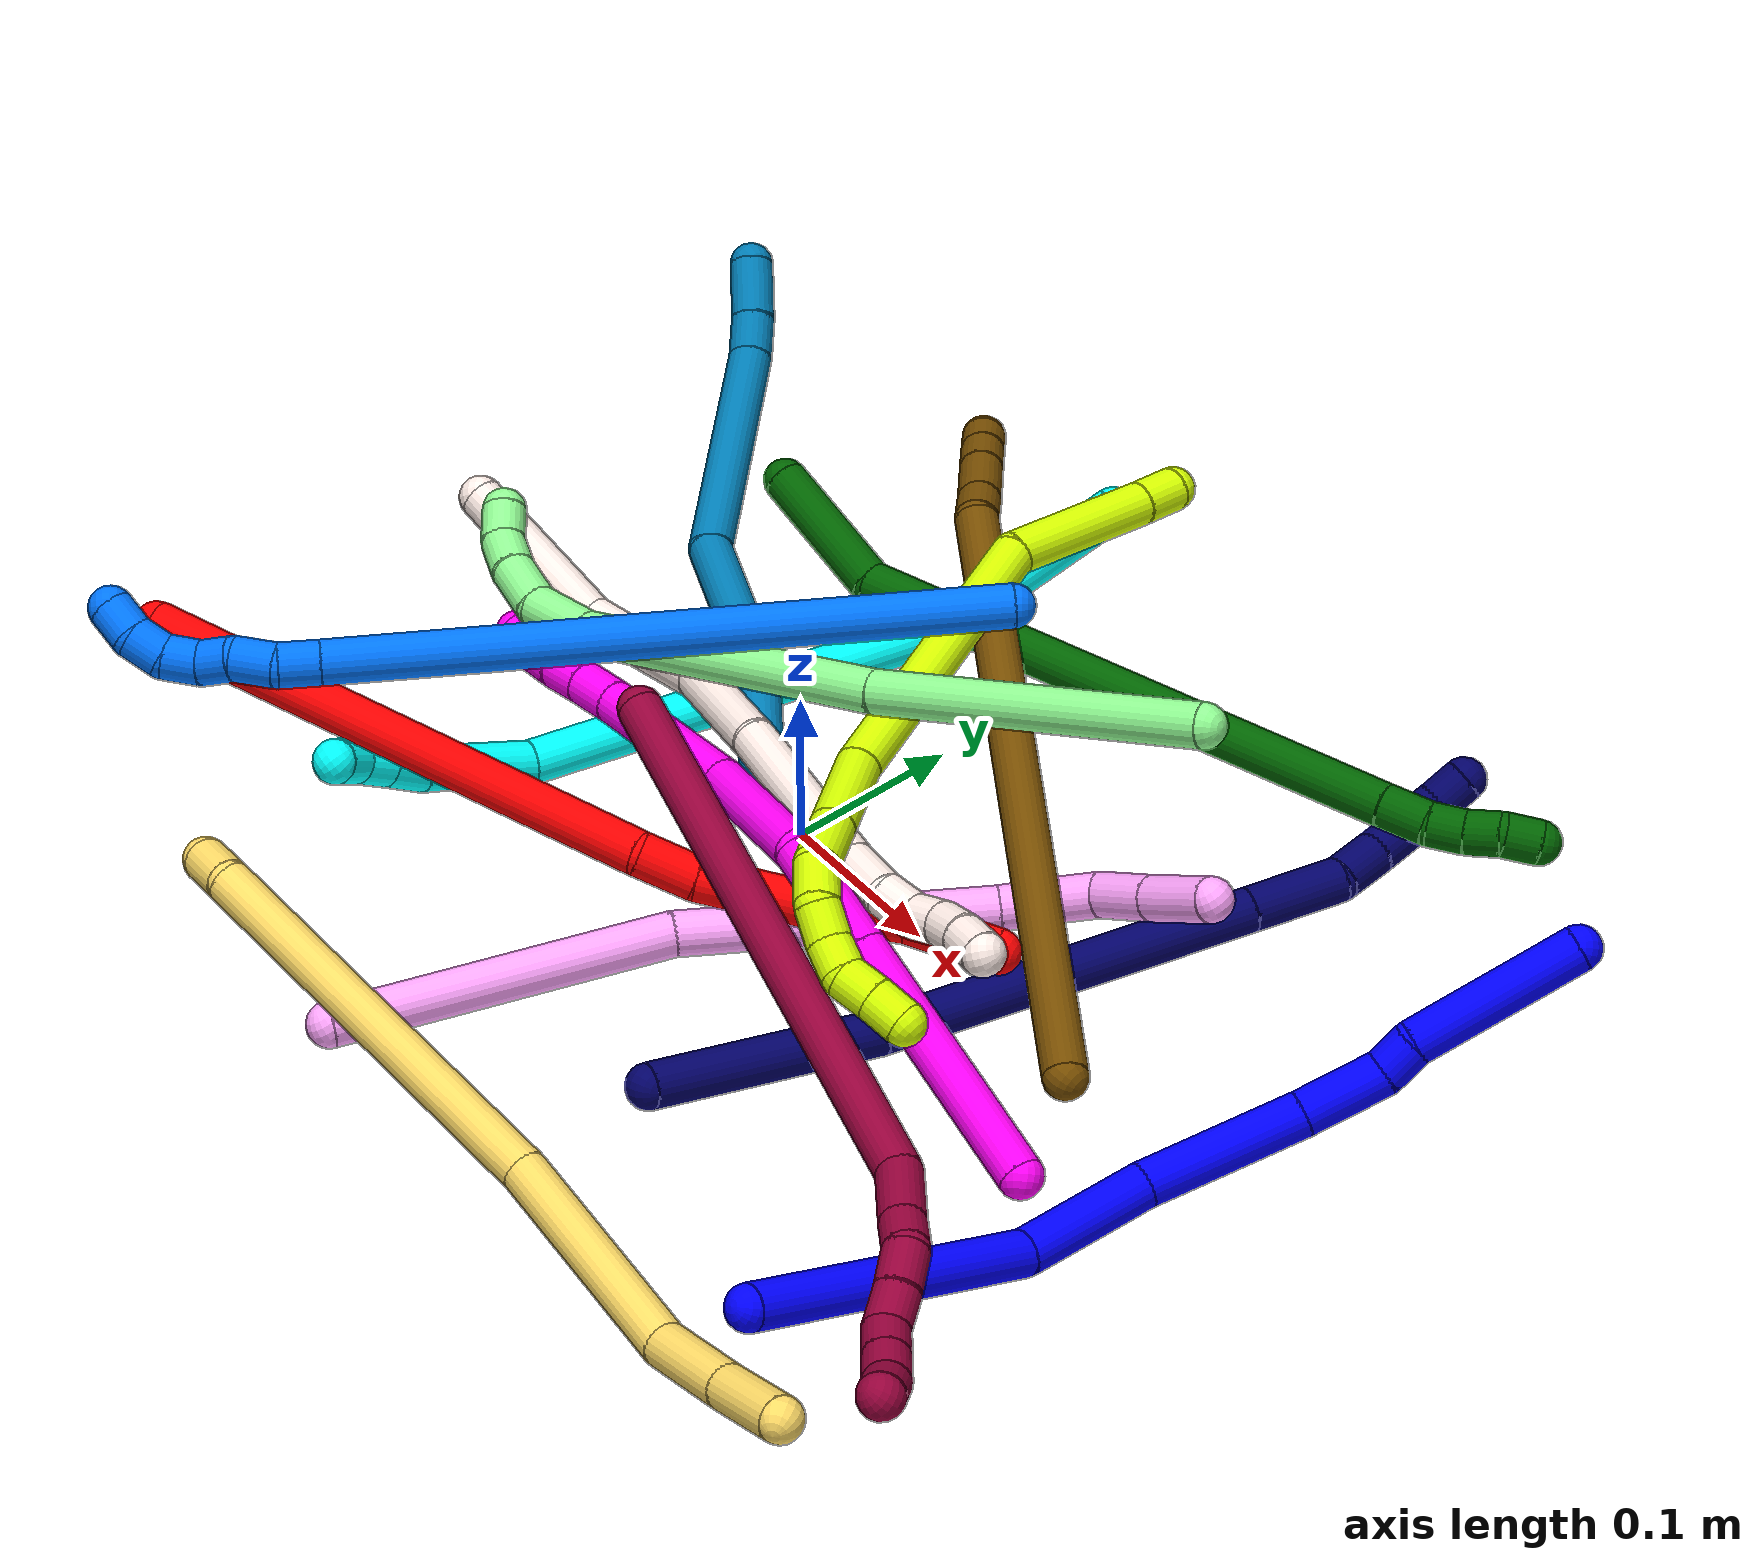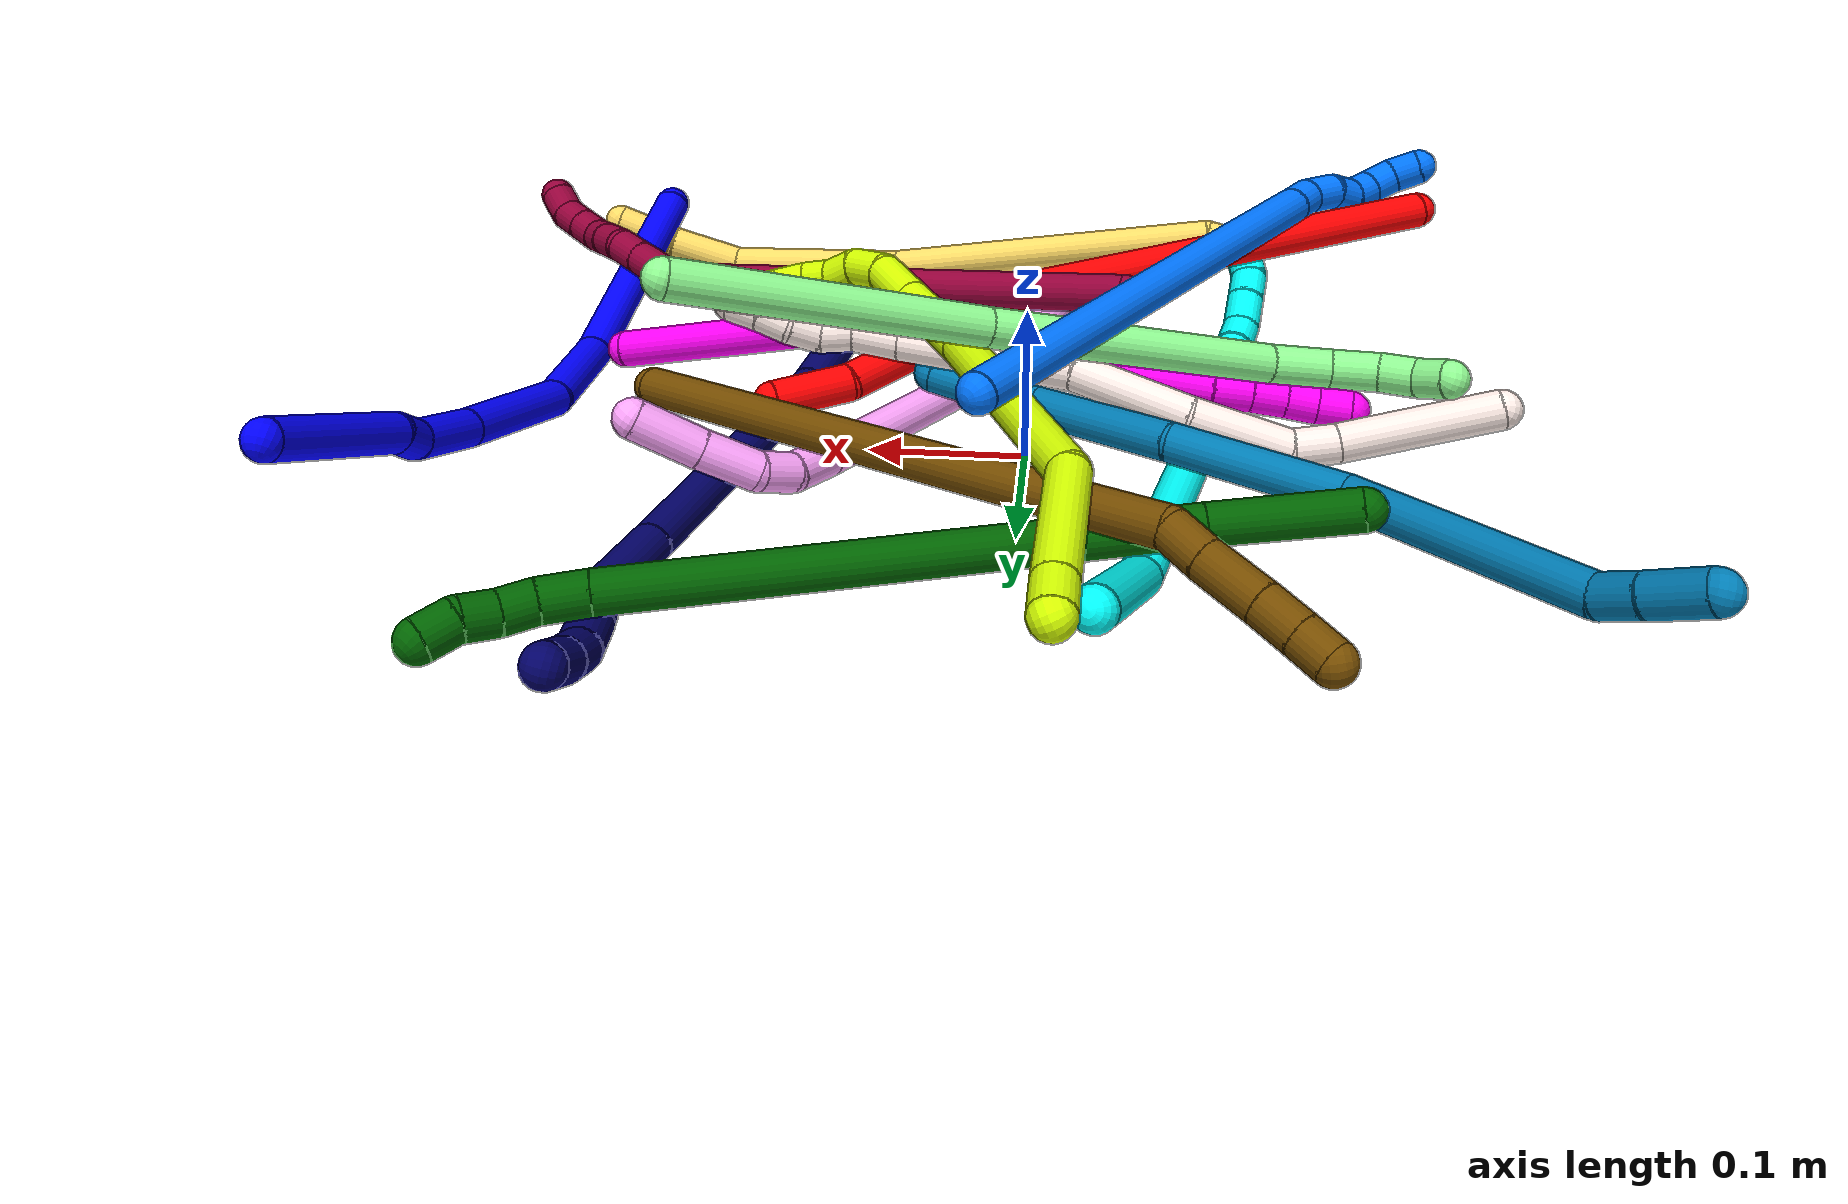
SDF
<sdf version="1.7">
 <world name="default">
  <plugin name="TubeGeneratorPlugin" filename="libtube_generator_plugin.so"/>
  <model name="photoneo_s_sensor">
   <static>1</static>
   <pose>0 0 2 1.57079 1.57079 3.14159</pose>
   <link name="link">
    <inertial><mass>0.1</mass></inertial>
    <sensor name="sensor" type="depth">
     <update_rate>30</update_rate>
     <camera>
      <horizontal_fov>1.22</horizontal_fov>
      <image><width>1920</width><height>1200</height><format>B8G8R8</format></image>
      <clip><near>0.1</near><far>4</far></clip>
      <depth_camera><output>points</output></depth_camera>
     </camera>
     <plugin name="camera_plugin" filename="libgazebo_ros_depth_camera.so">
      <baseline>0.2</baseline>
      <alwaysOn>1</alwaysOn>
      <updateRate>0.0</updateRate>
      <cameraName>camera_ir</cameraName>
      <imageTopicName>/camera/color/image_raw</imageTopicName>
      <cameraInfoTopicName>/camera/color/camera_info</cameraInfoTopicName>
      <depthImageTopicName>/camera/depth/image_raw</depthImageTopicName>
      <depthImageCameraInfoTopicName>/camera/depth/camera_info</depthImageCameraInfoTopicName>
      <pointCloudTopicName>/camera/depth/points</pointCloudTopicName>
      <frameName>fr_optical</frameName>
      <pointCloudCutoff>0.1</pointCloudCutoff>
      <pointCloudCutoffMax>2.0</pointCloudCutoffMax>
      <distortionK1>0</distortionK1>
      <distortionK2>0</distortionK2>
      <distortionK3>0</distortionK3>
      <distortionT1>0</distortionT1>
      <distortionT2>0</distortionT2>
      <CxPrime>0</CxPrime>
      <Cx>0</Cx>
      <Cy>0</Cy>
      <focalLength>0</focalLength>
      <hackBaseline>0</hackBaseline>
     </plugin>
    </sensor>
   </link>
  </model>
  <gravity>0 0 -9.8</gravity>
  <magnetic_field>6e-06 2.3e-05 -4.2e-05</magnetic_field>
  <atmosphere type="adiabatic"/>
  <physics name="default_physics" default="0" type="ode">
   <max_step_size>0.003</max_step_size>
   <real_time_factor>1</real_time_factor>
   <real_time_update_rate>1000</real_time_update_rate>
   <max_contacts>10000</max_contacts>
   <ode>
    <solver>
     <type>quick</type>
     <iters>100</iters>
     <sor>1.3</sor>
     <use_dynamic_moi_rescaling>0</use_dynamic_moi_rescaling>
    </solver>
    <constraints>
     <contact_max_correcting_vel>0</contact_max_correcting_vel>
     <contact_surface_layer>0.001</contact_surface_layer>
     <cfm>0</cfm>
     <erp>0.2</erp>
    </constraints>
   </ode>
  </physics>
  <scene><ambient>0.4 0.4 0.4 1</ambient><background>0.7 0.7 0.7 1</background><shadows>0</shadows></scene>
  <audio><device>default</device></audio>
  <spherical_coordinates>
   <surface_model>EARTH_WGS84</surface_model>
   <latitude_deg>0</latitude_deg>
   <longitude_deg>0</longitude_deg>
   <elevation>0</elevation>
   <heading_deg>0</heading_deg>
  </spherical_coordinates>
  <model name="bin">
   <static>1</static>
   <link name="bottom">
    <collision name="collision-bottom">
     <pose>0 0 -0.01 0 -0 0</pose>
     <geometry><box><size>0.8 0.6 0.02</size></box></geometry>
     <surface>
      <friction><ode><mu>100</mu><mu2>100</mu2></ode></friction>
      <contact><collide_bitmask>65535</collide_bitmask></contact>
     </surface>
    </collision>
   </link>
   <link name="west_wall">
    <collision name="collision-west_wall">
     <pose>-0.41 0 0.1 0 -0 0</pose>
     <geometry><box><size>0.02 0.6 0.2</size></box></geometry>
     <surface>
      <friction><ode><mu>100</mu><mu2>100</mu2></ode></friction>
      <contact><collide_bitmask>65535</collide_bitmask></contact>
     </surface>
    </collision>
   </link>
   <link name="east_wall">
    <collision name="collision-east_wall">
     <pose>0.41 0 0.1 0 -0 0</pose>
     <geometry><box><size>0.02 0.6 0.2</size></box></geometry>
     <surface>
      <friction><ode><mu>100</mu><mu2>100</mu2></ode></friction>
      <contact><collide_bitmask>65535</collide_bitmask></contact>
     </surface>
    </collision>
   </link>
   <link name="south_wall">
    <collision name="collision-south_wall">
     <pose>0 -0.31 0.1 0 -0 0</pose>
     <geometry><box><size>0.8 0.02 0.2</size></box></geometry>
     <surface>
      <friction><ode><mu>100</mu><mu2>100</mu2></ode></friction>
      <contact><collide_bitmask>65535</collide_bitmask></contact>
     </surface>
    </collision>
   </link>
   <link name="north_wall">
    <collision name="collision-north_wall">
     <pose>0 0.31 0.1 0 -0 0</pose>
     <geometry><box><size>0.8 0.02 0.2</size></box></geometry>
     <surface>
      <friction><ode><mu>100</mu><mu2>100</mu2></ode></friction>
      <contact><collide_bitmask>65535</collide_bitmask></contact>
     </surface>
    </collision>
   </link>
  </model>
  <model name="1">
   <static>0</static>
   <link name="1">
    <collision name="collision-cylinder-e_1_1_4">
     <pose>-0.00952 0.022188 0.081289 -0.266465 -0.112505 0.015094</pose>
     <geometry><cylinder><radius>0.0125</radius><length>0.169599</length></cylinder></geometry>
     <surface>
      <friction><ode><mu>1.16</mu><mu2>1.16</mu2><slip1>0</slip1><slip2>0</slip2></ode></friction>
      <contact><ode><kp>1e+06</kp><kd>1</kd><max_vel>0</max_vel><min_depth>0.001</min_depth></ode></contact>
     </surface>
    </collision>
    <visual name="visual-cylinder-e_1_1_4">
     <pose>-0.00952 0.022188 0.081289 -0.266465 -0.112505 0.015094</pose>
     <geometry><cylinder><radius>0.0125</radius><length>0.169599</length></cylinder></geometry>
     <material><ambient>0 0 1 1</ambient></material>
    </visual>
    <collision name="collision-cylinder-e_2_4_5">
     <pose>-0.023611 0.06646 0.193422 -0.621361 -0.119904 0.03854</pose>
     <geometry><cylinder><radius>0.0125</radius><length>0.076416</length></cylinder></geometry>
     <surface>
      <friction><ode><mu>1.16</mu><mu2>1.16</mu2><slip1>0</slip1><slip2>0</slip2></ode></friction>
      <contact><ode><kp>1e+06</kp><kd>1</kd><max_vel>0</max_vel><min_depth>0.001</min_depth></ode></contact>
     </surface>
    </collision>
    <visual name="visual-cylinder-e_2_4_5">
     <pose>-0.023611 0.06646 0.193422 -0.621361 -0.119904 0.03854</pose>
     <geometry><cylinder><radius>0.0125</radius><length>0.076416</length></cylinder></geometry>
     <material><ambient>0 0 1 1</ambient></material>
    </visual>
    <collision name="collision-cylinder-e_3_5_6">
     <pose>-0.045976 0.117167 0.253378 -0.77694 -0.41103 0.170218</pose>
     <geometry><cylinder><radius>0.0125</radius><length>0.089075</length></cylinder></geometry>
     <surface>
      <friction><ode><mu>1.16</mu><mu2>1.16</mu2><slip1>0</slip1><slip2>0</slip2></ode></friction>
      <contact><ode><kp>1e+06</kp><kd>1</kd><max_vel>0</max_vel><min_depth>0.001</min_depth></ode></contact>
     </surface>
    </collision>
    <visual name="visual-cylinder-e_3_5_6">
     <pose>-0.045976 0.117167 0.253378 -0.77694 -0.41103 0.170218</pose>
     <geometry><cylinder><radius>0.0125</radius><length>0.089075</length></cylinder></geometry>
     <material><ambient>0 0 1 1</ambient></material>
    </visual>
    <collision name="collision-cylinder-e_4_6_7">
     <pose>-0.073344 0.162064 0.296387 -0.86399 -0.420639 0.19621</pose>
     <geometry><cylinder><radius>0.0125</radius><length>0.046884</length></cylinder></geometry>
     <surface>
      <friction><ode><mu>1.16</mu><mu2>1.16</mu2><slip1>0</slip1><slip2>0</slip2></ode></friction>
      <contact><ode><kp>1e+06</kp><kd>1</kd><max_vel>0</max_vel><min_depth>0.001</min_depth></ode></contact>
     </surface>
    </collision>
    <visual name="visual-cylinder-e_4_6_7">
     <pose>-0.073344 0.162064 0.296387 -0.86399 -0.420639 0.19621</pose>
     <geometry><cylinder><radius>0.0125</radius><length>0.046884</length></cylinder></geometry>
     <material><ambient>0 0 1 1</ambient></material>
    </visual>
    <collision name="collision-cylinder-e_5_7_8">
     <pose>-0.086437 0.18806 0.313279 -1.27197 -0.333157 0.247014</pose>
     <geometry><cylinder><radius>0.0125</radius><length>0.021535</length></cylinder></geometry>
     <surface>
      <friction><ode><mu>1.16</mu><mu2>1.16</mu2><slip1>0</slip1><slip2>0</slip2></ode></friction>
      <contact><ode><kp>1e+06</kp><kd>1</kd><max_vel>0</max_vel><min_depth>0.001</min_depth></ode></contact>
     </surface>
    </collision>
    <visual name="visual-cylinder-e_5_7_8">
     <pose>-0.086437 0.18806 0.313279 -1.27197 -0.333157 0.247014</pose>
     <geometry><cylinder><radius>0.0125</radius><length>0.021535</length></cylinder></geometry>
     <material><ambient>0 0 1 1</ambient></material>
    </visual>
    <collision name="collision-cylinder-e_6_8_2">
     <pose>-0.111142 0.233928 0.340205 -0.985973 -0.45456 0.24723</pose>
     <geometry><cylinder><radius>0.0125</radius><length>0.096492</length></cylinder></geometry>
     <surface>
      <friction><ode><mu>1.16</mu><mu2>1.16</mu2><slip1>0</slip1><slip2>0</slip2></ode></friction>
      <contact><ode><kp>1e+06</kp><kd>1</kd><max_vel>0</max_vel><min_depth>0.001</min_depth></ode></contact>
     </surface>
    </collision>
    <visual name="visual-cylinder-e_6_8_2">
     <pose>-0.111142 0.233928 0.340205 -0.985973 -0.45456 0.24723</pose>
     <geometry><cylinder><radius>0.0125</radius><length>0.096492</length></cylinder></geometry>
     <material><ambient>0 0 1 1</ambient></material>
    </visual>
    <collision name="collision-sphere-2">
     <pose>-0.132325 0.270071 0.364134 0 -0 0</pose>
     <geometry><sphere><radius>0.0125</radius></sphere></geometry>
     <surface>
      <friction><ode><mu>1.16</mu><mu2>1.16</mu2><slip1>0</slip1><slip2>0</slip2></ode></friction>
      <contact><ode><kp>1e+06</kp><kd>1</kd><max_vel>0</max_vel><min_depth>0.001</min_depth></ode></contact>
     </surface>
    </collision>
    <visual name="visual-sphere-2">
     <pose>-0.132325 0.270071 0.364134 0 -0 0</pose>
     <geometry><sphere><radius>0.0125</radius></sphere></geometry>
     <material><ambient>0 0 1 1</ambient></material>
    </visual>
    <collision name="collision-sphere-4">
     <pose>-0.01904 0.044377 0.162579 0 -0 0</pose>
     <geometry><sphere><radius>0.0125</radius></sphere></geometry>
     <surface>
      <friction><ode><mu>1.16</mu><mu2>1.16</mu2><slip1>0</slip1><slip2>0</slip2></ode></friction>
      <contact><ode><kp>1e+06</kp><kd>1</kd><max_vel>0</max_vel><min_depth>0.001</min_depth></ode></contact>
     </surface>
    </collision>
    <visual name="visual-sphere-4">
     <pose>-0.01904 0.044377 0.162579 0 -0 0</pose>
     <geometry><sphere><radius>0.0125</radius></sphere></geometry>
     <material><ambient>0 0 1 1</ambient></material>
    </visual>
    <collision name="collision-sphere-1">
     <geometry><sphere><radius>0.0125</radius></sphere></geometry>
     <surface>
      <friction><ode><mu>1.16</mu><mu2>1.16</mu2><slip1>0</slip1><slip2>0</slip2></ode></friction>
      <contact><ode><kp>1e+06</kp><kd>1</kd><max_vel>0</max_vel><min_depth>0.001</min_depth></ode></contact>
     </surface>
    </collision>
    <visual name="visual-sphere-1">
     <geometry><sphere><radius>0.0125</radius></sphere></geometry>
     <material><ambient>0 0 1 1</ambient></material>
    </visual>
    <collision name="collision-sphere-8">
     <pose>-0.089959 0.197785 0.316275 0 -0 0</pose>
     <geometry><sphere><radius>0.0125</radius></sphere></geometry>
     <surface>
      <friction><ode><mu>1.16</mu><mu2>1.16</mu2><slip1>0</slip1><slip2>0</slip2></ode></friction>
      <contact><ode><kp>1e+06</kp><kd>1</kd><max_vel>0</max_vel><min_depth>0.001</min_depth></ode></contact>
     </surface>
    </collision>
    <visual name="visual-sphere-8">
     <pose>-0.089959 0.197785 0.316275 0 -0 0</pose>
     <geometry><sphere><radius>0.0125</radius></sphere></geometry>
     <material><ambient>0 0 1 1</ambient></material>
    </visual>
    <collision name="collision-sphere-5">
     <pose>-0.028181 0.088542 0.224265 0 -0 0</pose>
     <geometry><sphere><radius>0.0125</radius></sphere></geometry>
     <surface>
      <friction><ode><mu>1.16</mu><mu2>1.16</mu2><slip1>0</slip1><slip2>0</slip2></ode></friction>
      <contact><ode><kp>1e+06</kp><kd>1</kd><max_vel>0</max_vel><min_depth>0.001</min_depth></ode></contact>
     </surface>
    </collision>
    <visual name="visual-sphere-5">
     <pose>-0.028181 0.088542 0.224265 0 -0 0</pose>
     <geometry><sphere><radius>0.0125</radius></sphere></geometry>
     <material><ambient>0 0 1 1</ambient></material>
    </visual>
    <collision name="collision-sphere-6">
     <pose>-0.063771 0.145791 0.282491 0 -0 0</pose>
     <geometry><sphere><radius>0.0125</radius></sphere></geometry>
     <surface>
      <friction><ode><mu>1.16</mu><mu2>1.16</mu2><slip1>0</slip1><slip2>0</slip2></ode></friction>
      <contact><ode><kp>1e+06</kp><kd>1</kd><max_vel>0</max_vel><min_depth>0.001</min_depth></ode></contact>
     </surface>
    </collision>
    <visual name="visual-sphere-6">
     <pose>-0.063771 0.145791 0.282491 0 -0 0</pose>
     <geometry><sphere><radius>0.0125</radius></sphere></geometry>
     <material><ambient>0 0 1 1</ambient></material>
    </visual>
    <collision name="collision-sphere-7">
     <pose>-0.082916 0.178336 0.310284 0 -0 0</pose>
     <geometry><sphere><radius>0.0125</radius></sphere></geometry>
     <surface>
      <friction><ode><mu>1.16</mu><mu2>1.16</mu2><slip1>0</slip1><slip2>0</slip2></ode></friction>
      <contact><ode><kp>1e+06</kp><kd>1</kd><max_vel>0</max_vel><min_depth>0.001</min_depth></ode></contact>
     </surface>
    </collision>
    <visual name="visual-sphere-7">
     <pose>-0.082916 0.178336 0.310284 0 -0 0</pose>
     <geometry><sphere><radius>0.0125</radius></sphere></geometry>
     <material><ambient>0 0 1 1</ambient></material>
    </visual>
    <inertial>
     <pose>-0.047077 0.106997 0.209212 0 -0 0</pose>
     <mass>0.5</mass>
     <inertia>
      <ixx>0.000613</ixx>
      <ixy>0</ixy>
      <ixz>0</ixz>
      <iyy>0.000593</iyy>
      <iyz>0</iyz>
      <izz>-9.5e-05</izz>
     </inertia>
    </inertial>
   </link>
   <pose>0.290724 -0.267594 0.067416 2.21096 0.218971 -3.07177</pose>
  </model>
  <model name="2">
   <static>0</static>
   <link name="2">
    <collision name="collision-cylinder-e_1_1_4">
     <pose>-0.004816 0.015484 -0.150433 -3.03902 -0.031833 0.601417</pose>
     <geometry><cylinder><radius>0.0125</radius><length>0.30261</length></cylinder></geometry>
     <surface>
      <friction><ode><mu>1.16</mu><mu2>1.16</mu2><slip1>0</slip1><slip2>0</slip2></ode></friction>
      <contact><ode><kp>1e+06</kp><kd>1</kd><max_vel>0</max_vel><min_depth>0.001</min_depth></ode></contact>
     </surface>
    </collision>
    <visual name="visual-cylinder-e_1_1_4">
     <pose>-0.004816 0.015484 -0.150433 -3.03902 -0.031833 0.601417</pose>
     <geometry><cylinder><radius>0.0125</radius><length>0.30261</length></cylinder></geometry>
     <material><ambient>1 0 0 1</ambient></material>
    </visual>
    <collision name="collision-cylinder-e_2_4_5">
     <pose>-0.006245 0.036367 -0.315957 -2.79801 0.20823 -1.08415</pose>
     <geometry><cylinder><radius>0.0125</radius><length>0.032761</length></cylinder></geometry>
     <surface>
      <friction><ode><mu>1.16</mu><mu2>1.16</mu2><slip1>0</slip1><slip2>0</slip2></ode></friction>
      <contact><ode><kp>1e+06</kp><kd>1</kd><max_vel>0</max_vel><min_depth>0.001</min_depth></ode></contact>
     </surface>
    </collision>
    <visual name="visual-cylinder-e_2_4_5">
     <pose>-0.006245 0.036367 -0.315957 -2.79801 0.20823 -1.08415</pose>
     <geometry><cylinder><radius>0.0125</radius><length>0.032761</length></cylinder></geometry>
     <material><ambient>1 0 0 1</ambient></material>
    </visual>
    <collision name="collision-cylinder-e_3_5_6">
     <pose>0.006646 0.047292 -0.358323 -2.94168 0.329103 -2.05492</pose>
     <geometry><cylinder><radius>0.0125</radius><length>0.058817</length></cylinder></geometry>
     <surface>
      <friction><ode><mu>1.16</mu><mu2>1.16</mu2><slip1>0</slip1><slip2>0</slip2></ode></friction>
      <contact><ode><kp>1e+06</kp><kd>1</kd><max_vel>0</max_vel><min_depth>0.001</min_depth></ode></contact>
     </surface>
    </collision>
    <visual name="visual-cylinder-e_3_5_6">
     <pose>0.006646 0.047292 -0.358323 -2.94168 0.329103 -2.05492</pose>
     <geometry><cylinder><radius>0.0125</radius><length>0.058817</length></cylinder></geometry>
     <material><ambient>1 0 0 1</ambient></material>
    </visual>
    <collision name="collision-cylinder-e_4_6_7">
     <pose>0.026093 0.056404 -0.41065 -2.99944 0.374358 -2.42245</pose>
     <geometry><cylinder><radius>0.0125</radius><length>0.054379</length></cylinder></geometry>
     <surface>
      <friction><ode><mu>1.16</mu><mu2>1.16</mu2><slip1>0</slip1><slip2>0</slip2></ode></friction>
      <contact><ode><kp>1e+06</kp><kd>1</kd><max_vel>0</max_vel><min_depth>0.001</min_depth></ode></contact>
     </surface>
    </collision>
    <visual name="visual-cylinder-e_4_6_7">
     <pose>0.026093 0.056404 -0.41065 -2.99944 0.374358 -2.42245</pose>
     <geometry><cylinder><radius>0.0125</radius><length>0.054379</length></cylinder></geometry>
     <material><ambient>1 0 0 1</ambient></material>
    </visual>
    <collision name="collision-cylinder-e_5_7_2">
     <pose>0.038232 0.061562 -0.461275 -3.08019 0.085496 -1.8962</pose>
     <geometry><cylinder><radius>0.0125</radius><length>0.051434</length></cylinder></geometry>
     <surface>
      <friction><ode><mu>1.16</mu><mu2>1.16</mu2><slip1>0</slip1><slip2>0</slip2></ode></friction>
      <contact><ode><kp>1e+06</kp><kd>1</kd><max_vel>0</max_vel><min_depth>0.001</min_depth></ode></contact>
     </surface>
    </collision>
    <visual name="visual-cylinder-e_5_7_2">
     <pose>0.038232 0.061562 -0.461275 -3.08019 0.085496 -1.8962</pose>
     <geometry><cylinder><radius>0.0125</radius><length>0.051434</length></cylinder></geometry>
     <material><ambient>1 0 0 1</ambient></material>
    </visual>
    <collision name="collision-sphere-2">
     <pose>0.040428 0.063134 -0.48685 0 -0 0</pose>
     <geometry><sphere><radius>0.0125</radius></sphere></geometry>
     <surface>
      <friction><ode><mu>1.16</mu><mu2>1.16</mu2><slip1>0</slip1><slip2>0</slip2></ode></friction>
      <contact><ode><kp>1e+06</kp><kd>1</kd><max_vel>0</max_vel><min_depth>0.001</min_depth></ode></contact>
     </surface>
    </collision>
    <visual name="visual-sphere-2">
     <pose>0.040428 0.063134 -0.48685 0 -0 0</pose>
     <geometry><sphere><radius>0.0125</radius></sphere></geometry>
     <material><ambient>1 0 0 1</ambient></material>
    </visual>
    <collision name="collision-sphere-7">
     <pose>0.036036 0.05999 -0.435701 0 -0 0</pose>
     <geometry><sphere><radius>0.0125</radius></sphere></geometry>
     <surface>
      <friction><ode><mu>1.16</mu><mu2>1.16</mu2><slip1>0</slip1><slip2>0</slip2></ode></friction>
      <contact><ode><kp>1e+06</kp><kd>1</kd><max_vel>0</max_vel><min_depth>0.001</min_depth></ode></contact>
     </surface>
    </collision>
    <visual name="visual-sphere-7">
     <pose>0.036036 0.05999 -0.435701 0 -0 0</pose>
     <geometry><sphere><radius>0.0125</radius></sphere></geometry>
     <material><ambient>1 0 0 1</ambient></material>
    </visual>
    <collision name="collision-sphere-6">
     <pose>0.016151 0.052819 -0.385599 0 -0 0</pose>
     <geometry><sphere><radius>0.0125</radius></sphere></geometry>
     <surface>
      <friction><ode><mu>1.16</mu><mu2>1.16</mu2><slip1>0</slip1><slip2>0</slip2></ode></friction>
      <contact><ode><kp>1e+06</kp><kd>1</kd><max_vel>0</max_vel><min_depth>0.001</min_depth></ode></contact>
     </surface>
    </collision>
    <visual name="visual-sphere-6">
     <pose>0.016151 0.052819 -0.385599 0 -0 0</pose>
     <geometry><sphere><radius>0.0125</radius></sphere></geometry>
     <material><ambient>1 0 0 1</ambient></material>
    </visual>
    <collision name="collision-sphere-5">
     <pose>-0.002859 0.041766 -0.331046 0 -0 0</pose>
     <geometry><sphere><radius>0.0125</radius></sphere></geometry>
     <surface>
      <friction><ode><mu>1.16</mu><mu2>1.16</mu2><slip1>0</slip1><slip2>0</slip2></ode></friction>
      <contact><ode><kp>1e+06</kp><kd>1</kd><max_vel>0</max_vel><min_depth>0.001</min_depth></ode></contact>
     </surface>
    </collision>
    <visual name="visual-sphere-5">
     <pose>-0.002859 0.041766 -0.331046 0 -0 0</pose>
     <geometry><sphere><radius>0.0125</radius></sphere></geometry>
     <material><ambient>1 0 0 1</ambient></material>
    </visual>
    <collision name="collision-sphere-1">
     <geometry><sphere><radius>0.0125</radius></sphere></geometry>
     <surface>
      <friction><ode><mu>1.16</mu><mu2>1.16</mu2><slip1>0</slip1><slip2>0</slip2></ode></friction>
      <contact><ode><kp>1e+06</kp><kd>1</kd><max_vel>0</max_vel><min_depth>0.001</min_depth></ode></contact>
     </surface>
    </collision>
    <visual name="visual-sphere-1">
     <geometry><sphere><radius>0.0125</radius></sphere></geometry>
     <material><ambient>1 0 0 1</ambient></material>
    </visual>
    <collision name="collision-sphere-4">
     <pose>-0.009631 0.030968 -0.300867 0 -0 0</pose>
     <geometry><sphere><radius>0.0125</radius></sphere></geometry>
     <surface>
      <friction><ode><mu>1.16</mu><mu2>1.16</mu2><slip1>0</slip1><slip2>0</slip2></ode></friction>
      <contact><ode><kp>1e+06</kp><kd>1</kd><max_vel>0</max_vel><min_depth>0.001</min_depth></ode></contact>
     </surface>
    </collision>
    <visual name="visual-sphere-4">
     <pose>-0.009631 0.030968 -0.300867 0 -0 0</pose>
     <geometry><sphere><radius>0.0125</radius></sphere></geometry>
     <material><ambient>1 0 0 1</ambient></material>
    </visual>
    <inertial>
     <pose>0.004229 0.029784 -0.24601 0 -0 0</pose>
     <mass>0.5</mass>
     <inertia>
      <ixx>0.003165</ixx>
      <ixy>0</ixy>
      <ixz>0</ixz>
      <iyy>-0.000599</iyy>
      <iyz>0</iyz>
      <izz>-0.000223</izz>
     </inertia>
    </inertial>
   </link>
   <pose>-0.271286 -0.227524 0.094287 -1.57854 0.003305 1.97951</pose>
  </model>
  <model name="3">
   <static>0</static>
   <link name="3">
    <collision name="collision-cylinder-e_1_1_4">
     <pose>0.002173 -0.004572 -0.060671 3.06637 0.035703 0.886072</pose>
     <geometry><cylinder><radius>0.0125</radius><length>0.121763</length></cylinder></geometry>
     <surface>
      <friction><ode><mu>1.16</mu><mu2>1.16</mu2><slip1>0</slip1><slip2>0</slip2></ode></friction>
      <contact><ode><kp>1e+06</kp><kd>1</kd><max_vel>0</max_vel><min_depth>0.001</min_depth></ode></contact>
     </surface>
    </collision>
    <visual name="visual-cylinder-e_1_1_4">
     <pose>0.002173 -0.004572 -0.060671 3.06637 0.035703 0.886072</pose>
     <geometry><cylinder><radius>0.0125</radius><length>0.121763</length></cylinder></geometry>
     <material><ambient>0.003922 1 0.996078 1</ambient></material>
    </visual>
    <collision name="collision-cylinder-e_2_4_5">
     <pose>0.005239 -0.067726 -0.230075 2.64741 0.007229 0.028657</pose>
     <geometry><cylinder><radius>0.0125</radius><length>0.247027</length></cylinder></geometry>
     <surface>
      <friction><ode><mu>1.16</mu><mu2>1.16</mu2><slip1>0</slip1><slip2>0</slip2></ode></friction>
      <contact><ode><kp>1e+06</kp><kd>1</kd><max_vel>0</max_vel><min_depth>0.001</min_depth></ode></contact>
     </surface>
    </collision>
    <visual name="visual-cylinder-e_2_4_5">
     <pose>0.005239 -0.067726 -0.230075 2.64741 0.007229 0.028657</pose>
     <geometry><cylinder><radius>0.0125</radius><length>0.247027</length></cylinder></geometry>
     <material><ambient>0.003922 1 0.996078 1</ambient></material>
    </visual>
    <collision name="collision-cylinder-e_3_5_6">
     <pose>0.006134 -0.142408 -0.353583 2.31328 9.4e-05 0.000213</pose>
     <geometry><cylinder><radius>0.0125</radius><length>0.043704</length></cylinder></geometry>
     <surface>
      <friction><ode><mu>1.16</mu><mu2>1.16</mu2><slip1>0</slip1><slip2>0</slip2></ode></friction>
      <contact><ode><kp>1e+06</kp><kd>1</kd><max_vel>0</max_vel><min_depth>0.001</min_depth></ode></contact>
     </surface>
    </collision>
    <visual name="visual-cylinder-e_3_5_6">
     <pose>0.006134 -0.142408 -0.353583 2.31328 9.4e-05 0.000213</pose>
     <geometry><cylinder><radius>0.0125</radius><length>0.043704</length></cylinder></geometry>
     <material><ambient>0.003922 1 0.996078 1</ambient></material>
    </visual>
    <collision name="collision-cylinder-e_4_6_7">
     <pose>0.005655 -0.165745 -0.376116 2.39103 -0.045323 -0.114942</pose>
     <geometry><cylinder><radius>0.0125</radius><length>0.021242</length></cylinder></geometry>
     <surface>
      <friction><ode><mu>1.16</mu><mu2>1.16</mu2><slip1>0</slip1><slip2>0</slip2></ode></friction>
      <contact><ode><kp>1e+06</kp><kd>1</kd><max_vel>0</max_vel><min_depth>0.001</min_depth></ode></contact>
     </surface>
    </collision>
    <visual name="visual-cylinder-e_4_6_7">
     <pose>0.005655 -0.165745 -0.376116 2.39103 -0.045323 -0.114942</pose>
     <geometry><cylinder><radius>0.0125</radius><length>0.021242</length></cylinder></geometry>
     <material><ambient>0.003922 1 0.996078 1</ambient></material>
    </visual>
    <collision name="collision-cylinder-e_5_7_8">
     <pose>0.005589 -0.183951 -0.389752 2.06263 0.033377 0.055737</pose>
     <geometry><cylinder><radius>0.0125</radius><length>0.024904</length></cylinder></geometry>
     <surface>
      <friction><ode><mu>1.16</mu><mu2>1.16</mu2><slip1>0</slip1><slip2>0</slip2></ode></friction>
      <contact><ode><kp>1e+06</kp><kd>1</kd><max_vel>0</max_vel><min_depth>0.001</min_depth></ode></contact>
     </surface>
    </collision>
    <visual name="visual-cylinder-e_5_7_8">
     <pose>0.005589 -0.183951 -0.389752 2.06263 0.033377 0.055737</pose>
     <geometry><cylinder><radius>0.0125</radius><length>0.024904</length></cylinder></geometry>
     <material><ambient>0.003922 1 0.996078 1</ambient></material>
    </visual>
    <collision name="collision-cylinder-e_6_8_9">
     <pose>0.006397 -0.203597 -0.400663 2.09657 0.039041 0.067773</pose>
     <geometry><cylinder><radius>0.0125</radius><length>0.020076</length></cylinder></geometry>
     <surface>
      <friction><ode><mu>1.16</mu><mu2>1.16</mu2><slip1>0</slip1><slip2>0</slip2></ode></friction>
      <contact><ode><kp>1e+06</kp><kd>1</kd><max_vel>0</max_vel><min_depth>0.001</min_depth></ode></contact>
     </surface>
    </collision>
    <visual name="visual-cylinder-e_6_8_9">
     <pose>0.006397 -0.203597 -0.400663 2.09657 0.039041 0.067773</pose>
     <geometry><cylinder><radius>0.0125</radius><length>0.020076</length></cylinder></geometry>
     <material><ambient>0.003922 1 0.996078 1</ambient></material>
    </visual>
    <collision name="collision-cylinder-e_7_9_2">
     <pose>0.010757 -0.221573 -0.409015 1.91344 0.38216 0.535584</pose>
     <geometry><cylinder><radius>0.0125</radius><length>0.021285</length></cylinder></geometry>
     <surface>
      <friction><ode><mu>1.16</mu><mu2>1.16</mu2><slip1>0</slip1><slip2>0</slip2></ode></friction>
      <contact><ode><kp>1e+06</kp><kd>1</kd><max_vel>0</max_vel><min_depth>0.001</min_depth></ode></contact>
     </surface>
    </collision>
    <visual name="visual-cylinder-e_7_9_2">
     <pose>0.010757 -0.221573 -0.409015 1.91344 0.38216 0.535584</pose>
     <geometry><cylinder><radius>0.0125</radius><length>0.021285</length></cylinder></geometry>
     <material><ambient>0.003922 1 0.996078 1</ambient></material>
    </visual>
    <collision name="collision-sphere-2">
     <pose>0.014726 -0.230874 -0.412333 0 -0 0</pose>
     <geometry><sphere><radius>0.0125</radius></sphere></geometry>
     <surface>
      <friction><ode><mu>1.16</mu><mu2>1.16</mu2><slip1>0</slip1><slip2>0</slip2></ode></friction>
      <contact><ode><kp>1e+06</kp><kd>1</kd><max_vel>0</max_vel><min_depth>0.001</min_depth></ode></contact>
     </surface>
    </collision>
    <visual name="visual-sphere-2">
     <pose>0.014726 -0.230874 -0.412333 0 -0 0</pose>
     <geometry><sphere><radius>0.0125</radius></sphere></geometry>
     <material><ambient>0.003922 1 0.996078 1</ambient></material>
    </visual>
    <collision name="collision-sphere-9">
     <pose>0.006788 -0.212273 -0.405698 0 -0 0</pose>
     <geometry><sphere><radius>0.0125</radius></sphere></geometry>
     <surface>
      <friction><ode><mu>1.16</mu><mu2>1.16</mu2><slip1>0</slip1><slip2>0</slip2></ode></friction>
      <contact><ode><kp>1e+06</kp><kd>1</kd><max_vel>0</max_vel><min_depth>0.001</min_depth></ode></contact>
     </surface>
    </collision>
    <visual name="visual-sphere-9">
     <pose>0.006788 -0.212273 -0.405698 0 -0 0</pose>
     <geometry><sphere><radius>0.0125</radius></sphere></geometry>
     <material><ambient>0.003922 1 0.996078 1</ambient></material>
    </visual>
    <collision name="collision-sphere-4">
     <pose>0.004346 -0.009144 -0.121342 0 -0 0</pose>
     <geometry><sphere><radius>0.0125</radius></sphere></geometry>
     <surface>
      <friction><ode><mu>1.16</mu><mu2>1.16</mu2><slip1>0</slip1><slip2>0</slip2></ode></friction>
      <contact><ode><kp>1e+06</kp><kd>1</kd><max_vel>0</max_vel><min_depth>0.001</min_depth></ode></contact>
     </surface>
    </collision>
    <visual name="visual-sphere-4">
     <pose>0.004346 -0.009144 -0.121342 0 -0 0</pose>
     <geometry><sphere><radius>0.0125</radius></sphere></geometry>
     <material><ambient>0.003922 1 0.996078 1</ambient></material>
    </visual>
    <collision name="collision-sphere-1">
     <geometry><sphere><radius>0.0125</radius></sphere></geometry>
     <surface>
      <friction><ode><mu>1.16</mu><mu2>1.16</mu2><slip1>0</slip1><slip2>0</slip2></ode></friction>
      <contact><ode><kp>1e+06</kp><kd>1</kd><max_vel>0</max_vel><min_depth>0.001</min_depth></ode></contact>
     </surface>
    </collision>
    <visual name="visual-sphere-1">
     <geometry><sphere><radius>0.0125</radius></sphere></geometry>
     <material><ambient>0.003922 1 0.996078 1</ambient></material>
    </visual>
    <collision name="collision-sphere-8">
     <pose>0.006005 -0.194921 -0.395629 0 -0 0</pose>
     <geometry><sphere><radius>0.0125</radius></sphere></geometry>
     <surface>
      <friction><ode><mu>1.16</mu><mu2>1.16</mu2><slip1>0</slip1><slip2>0</slip2></ode></friction>
      <contact><ode><kp>1e+06</kp><kd>1</kd><max_vel>0</max_vel><min_depth>0.001</min_depth></ode></contact>
     </surface>
    </collision>
    <visual name="visual-sphere-8">
     <pose>0.006005 -0.194921 -0.395629 0 -0 0</pose>
     <geometry><sphere><radius>0.0125</radius></sphere></geometry>
     <material><ambient>0.003922 1 0.996078 1</ambient></material>
    </visual>
    <collision name="collision-sphere-5">
     <pose>0.006132 -0.126308 -0.338808 0 -0 0</pose>
     <geometry><sphere><radius>0.0125</radius></sphere></geometry>
     <surface>
      <friction><ode><mu>1.16</mu><mu2>1.16</mu2><slip1>0</slip1><slip2>0</slip2></ode></friction>
      <contact><ode><kp>1e+06</kp><kd>1</kd><max_vel>0</max_vel><min_depth>0.001</min_depth></ode></contact>
     </surface>
    </collision>
    <visual name="visual-sphere-5">
     <pose>0.006132 -0.126308 -0.338808 0 -0 0</pose>
     <geometry><sphere><radius>0.0125</radius></sphere></geometry>
     <material><ambient>0.003922 1 0.996078 1</ambient></material>
    </visual>
    <collision name="collision-sphere-6">
     <pose>0.006136 -0.158509 -0.368357 0 -0 0</pose>
     <geometry><sphere><radius>0.0125</radius></sphere></geometry>
     <surface>
      <friction><ode><mu>1.16</mu><mu2>1.16</mu2><slip1>0</slip1><slip2>0</slip2></ode></friction>
      <contact><ode><kp>1e+06</kp><kd>1</kd><max_vel>0</max_vel><min_depth>0.001</min_depth></ode></contact>
     </surface>
    </collision>
    <visual name="visual-sphere-6">
     <pose>0.006136 -0.158509 -0.368357 0 -0 0</pose>
     <geometry><sphere><radius>0.0125</radius></sphere></geometry>
     <material><ambient>0.003922 1 0.996078 1</ambient></material>
    </visual>
    <collision name="collision-sphere-7">
     <pose>0.005174 -0.172982 -0.383875 0 -0 0</pose>
     <geometry><sphere><radius>0.0125</radius></sphere></geometry>
     <surface>
      <friction><ode><mu>1.16</mu><mu2>1.16</mu2><slip1>0</slip1><slip2>0</slip2></ode></friction>
      <contact><ode><kp>1e+06</kp><kd>1</kd><max_vel>0</max_vel><min_depth>0.001</min_depth></ode></contact>
     </surface>
    </collision>
    <visual name="visual-sphere-7">
     <pose>0.005174 -0.172982 -0.383875 0 -0 0</pose>
     <geometry><sphere><radius>0.0125</radius></sphere></geometry>
     <material><ambient>0.003922 1 0.996078 1</ambient></material>
    </visual>
    <inertial>
     <pose>0.004887 -0.080832 -0.22824 0 -0 0</pose>
     <mass>0.5</mass>
     <inertia>
      <ixx>0.001537</ixx>
      <ixy>0</ixy>
      <ixz>0</ixz>
      <iyy>-0.001081</iyy>
      <iyz>0</iyz>
      <izz>0.000577</izz>
     </inertia>
    </inertial>
   </link>
   <pose>-0.044559 0.260784 0.061109 -1.07694 0.047853 -0.248272</pose>
  </model>
  <model name="4">
   <static>0</static>
   <link name="4">
    <collision name="collision-cylinder-e_1_1_4">
     <pose>0.075003 0.04784 0.033656 -0.957719 0.908453 -0.496532</pose>
     <geometry><cylinder><radius>0.0125</radius><length>0.190229</length></cylinder></geometry>
     <surface>
      <friction><ode><mu>1.16</mu><mu2>1.16</mu2><slip1>0</slip1><slip2>0</slip2></ode></friction>
      <contact><ode><kp>1e+06</kp><kd>1</kd><max_vel>0</max_vel><min_depth>0.001</min_depth></ode></contact>
     </surface>
    </collision>
    <visual name="visual-cylinder-e_1_1_4">
     <pose>0.075003 0.04784 0.033656 -0.957719 0.908453 -0.496532</pose>
     <geometry><cylinder><radius>0.0125</radius><length>0.190229</length></cylinder></geometry>
     <material><ambient>1 0.65098 0.996078 1</ambient></material>
    </visual>
    <collision name="collision-cylinder-e_2_4_5">
     <pose>0.202001 0.153567 0.105967 -0.982024 0.64156 -0.351638</pose>
     <geometry><cylinder><radius>0.0125</radius><length>0.173766</length></cylinder></geometry>
     <surface>
      <friction><ode><mu>1.16</mu><mu2>1.16</mu2><slip1>0</slip1><slip2>0</slip2></ode></friction>
      <contact><ode><kp>1e+06</kp><kd>1</kd><max_vel>0</max_vel><min_depth>0.001</min_depth></ode></contact>
     </surface>
    </collision>
    <visual name="visual-cylinder-e_2_4_5">
     <pose>0.202001 0.153567 0.105967 -0.982024 0.64156 -0.351638</pose>
     <geometry><cylinder><radius>0.0125</radius><length>0.173766</length></cylinder></geometry>
     <material><ambient>1 0.65098 0.996078 1</ambient></material>
    </visual>
    <collision name="collision-cylinder-e_3_5_6">
     <pose>0.263481 0.22219 0.150421 -1.07566 0.660833 -0.403609</pose>
     <geometry><cylinder><radius>0.0125</radius><length>0.03091</length></cylinder></geometry>
     <surface>
      <friction><ode><mu>1.16</mu><mu2>1.16</mu2><slip1>0</slip1><slip2>0</slip2></ode></friction>
      <contact><ode><kp>1e+06</kp><kd>1</kd><max_vel>0</max_vel><min_depth>0.001</min_depth></ode></contact>
     </surface>
    </collision>
    <visual name="visual-cylinder-e_3_5_6">
     <pose>0.263481 0.22219 0.150421 -1.07566 0.660833 -0.403609</pose>
     <geometry><cylinder><radius>0.0125</radius><length>0.03091</length></cylinder></geometry>
     <material><ambient>1 0.65098 0.996078 1</ambient></material>
    </visual>
    <collision name="collision-cylinder-e_4_6_7">
     <pose>0.277178 0.244214 0.159168 -1.31518 0.346372 -0.268567</pose>
     <geometry><cylinder><radius>0.0125</radius><length>0.024807</length></cylinder></geometry>
     <surface>
      <friction><ode><mu>1.16</mu><mu2>1.16</mu2><slip1>0</slip1><slip2>0</slip2></ode></friction>
      <contact><ode><kp>1e+06</kp><kd>1</kd><max_vel>0</max_vel><min_depth>0.001</min_depth></ode></contact>
     </surface>
    </collision>
    <visual name="visual-cylinder-e_4_6_7">
     <pose>0.277178 0.244214 0.159168 -1.31518 0.346372 -0.268567</pose>
     <geometry><cylinder><radius>0.0125</radius><length>0.024807</length></cylinder></geometry>
     <material><ambient>1 0.65098 0.996078 1</ambient></material>
    </visual>
    <collision name="collision-cylinder-e_5_7_8">
     <pose>0.279495 0.273896 0.164322 -1.45152 -0.101885 0.09042</pose>
     <geometry><cylinder><radius>0.0125</radius><length>0.037246</length></cylinder></geometry>
     <surface>
      <friction><ode><mu>1.16</mu><mu2>1.16</mu2><slip1>0</slip1><slip2>0</slip2></ode></friction>
      <contact><ode><kp>1e+06</kp><kd>1</kd><max_vel>0</max_vel><min_depth>0.001</min_depth></ode></contact>
     </surface>
    </collision>
    <visual name="visual-cylinder-e_5_7_8">
     <pose>0.279495 0.273896 0.164322 -1.45152 -0.101885 0.09042</pose>
     <geometry><cylinder><radius>0.0125</radius><length>0.037246</length></cylinder></geometry>
     <material><ambient>1 0.65098 0.996078 1</ambient></material>
    </visual>
    <collision name="collision-cylinder-e_6_8_2">
     <pose>0.275073 0.313616 0.167945 -1.50439 -0.117701 0.110149</pose>
     <geometry><cylinder><radius>0.0125</radius><length>0.043042</length></cylinder></geometry>
     <surface>
      <friction><ode><mu>1.16</mu><mu2>1.16</mu2><slip1>0</slip1><slip2>0</slip2></ode></friction>
      <contact><ode><kp>1e+06</kp><kd>1</kd><max_vel>0</max_vel><min_depth>0.001</min_depth></ode></contact>
     </surface>
    </collision>
    <visual name="visual-cylinder-e_6_8_2">
     <pose>0.275073 0.313616 0.167945 -1.50439 -0.117701 0.110149</pose>
     <geometry><cylinder><radius>0.0125</radius><length>0.043042</length></cylinder></geometry>
     <material><ambient>1 0.65098 0.996078 1</ambient></material>
    </visual>
    <collision name="collision-sphere-2">
     <pose>0.272546 0.334941 0.169363 0 -0 0</pose>
     <geometry><sphere><radius>0.0125</radius></sphere></geometry>
     <surface>
      <friction><ode><mu>1.16</mu><mu2>1.16</mu2><slip1>0</slip1><slip2>0</slip2></ode></friction>
      <contact><ode><kp>1e+06</kp><kd>1</kd><max_vel>0</max_vel><min_depth>0.001</min_depth></ode></contact>
     </surface>
    </collision>
    <visual name="visual-sphere-2">
     <pose>0.272546 0.334941 0.169363 0 -0 0</pose>
     <geometry><sphere><radius>0.0125</radius></sphere></geometry>
     <material><ambient>1 0.65098 0.996078 1</ambient></material>
    </visual>
    <collision name="collision-sphere-4">
     <pose>0.150006 0.09568 0.067312 0 -0 0</pose>
     <geometry><sphere><radius>0.0125</radius></sphere></geometry>
     <surface>
      <friction><ode><mu>1.16</mu><mu2>1.16</mu2><slip1>0</slip1><slip2>0</slip2></ode></friction>
      <contact><ode><kp>1e+06</kp><kd>1</kd><max_vel>0</max_vel><min_depth>0.001</min_depth></ode></contact>
     </surface>
    </collision>
    <visual name="visual-sphere-4">
     <pose>0.150006 0.09568 0.067312 0 -0 0</pose>
     <geometry><sphere><radius>0.0125</radius></sphere></geometry>
     <material><ambient>1 0.65098 0.996078 1</ambient></material>
    </visual>
    <collision name="collision-sphere-1">
     <geometry><sphere><radius>0.0125</radius></sphere></geometry>
     <surface>
      <friction><ode><mu>1.16</mu><mu2>1.16</mu2><slip1>0</slip1><slip2>0</slip2></ode></friction>
      <contact><ode><kp>1e+06</kp><kd>1</kd><max_vel>0</max_vel><min_depth>0.001</min_depth></ode></contact>
     </surface>
    </collision>
    <visual name="visual-sphere-1">
     <geometry><sphere><radius>0.0125</radius></sphere></geometry>
     <material><ambient>1 0.65098 0.996078 1</ambient></material>
    </visual>
    <collision name="collision-sphere-8">
     <pose>0.277601 0.292291 0.166527 0 -0 0</pose>
     <geometry><sphere><radius>0.0125</radius></sphere></geometry>
     <surface>
      <friction><ode><mu>1.16</mu><mu2>1.16</mu2><slip1>0</slip1><slip2>0</slip2></ode></friction>
      <contact><ode><kp>1e+06</kp><kd>1</kd><max_vel>0</max_vel><min_depth>0.001</min_depth></ode></contact>
     </surface>
    </collision>
    <visual name="visual-sphere-8">
     <pose>0.277601 0.292291 0.166527 0 -0 0</pose>
     <geometry><sphere><radius>0.0125</radius></sphere></geometry>
     <material><ambient>1 0.65098 0.996078 1</ambient></material>
    </visual>
    <collision name="collision-sphere-5">
     <pose>0.253995 0.211454 0.144623 0 -0 0</pose>
     <geometry><sphere><radius>0.0125</radius></sphere></geometry>
     <surface>
      <friction><ode><mu>1.16</mu><mu2>1.16</mu2><slip1>0</slip1><slip2>0</slip2></ode></friction>
      <contact><ode><kp>1e+06</kp><kd>1</kd><max_vel>0</max_vel><min_depth>0.001</min_depth></ode></contact>
     </surface>
    </collision>
    <visual name="visual-sphere-5">
     <pose>0.253995 0.211454 0.144623 0 -0 0</pose>
     <geometry><sphere><radius>0.0125</radius></sphere></geometry>
     <material><ambient>1 0.65098 0.996078 1</ambient></material>
    </visual>
    <collision name="collision-sphere-6">
     <pose>0.272967 0.232926 0.156218 0 -0 0</pose>
     <geometry><sphere><radius>0.0125</radius></sphere></geometry>
     <surface>
      <friction><ode><mu>1.16</mu><mu2>1.16</mu2><slip1>0</slip1><slip2>0</slip2></ode></friction>
      <contact><ode><kp>1e+06</kp><kd>1</kd><max_vel>0</max_vel><min_depth>0.001</min_depth></ode></contact>
     </surface>
    </collision>
    <visual name="visual-sphere-6">
     <pose>0.272967 0.232926 0.156218 0 -0 0</pose>
     <geometry><sphere><radius>0.0125</radius></sphere></geometry>
     <material><ambient>1 0.65098 0.996078 1</ambient></material>
    </visual>
    <collision name="collision-sphere-7">
     <pose>0.281389 0.255502 0.162118 0 -0 0</pose>
     <geometry><sphere><radius>0.0125</radius></sphere></geometry>
     <surface>
      <friction><ode><mu>1.16</mu><mu2>1.16</mu2><slip1>0</slip1><slip2>0</slip2></ode></friction>
      <contact><ode><kp>1e+06</kp><kd>1</kd><max_vel>0</max_vel><min_depth>0.001</min_depth></ode></contact>
     </surface>
    </collision>
    <visual name="visual-sphere-7">
     <pose>0.281389 0.255502 0.162118 0 -0 0</pose>
     <geometry><sphere><radius>0.0125</radius></sphere></geometry>
     <material><ambient>1 0.65098 0.996078 1</ambient></material>
    </visual>
    <inertial>
     <pose>0.173277 0.144823 0.093526 0 -0 0</pose>
     <mass>0.5</mass>
     <inertia>
      <ixx>0.000395</ixx>
      <ixy>0</ixy>
      <ixz>0</ixz>
      <iyy>0.000518</iyy>
      <iyz>0</iyz>
      <izz>-0.001319</izz>
     </inertia>
    </inertial>
   </link>
   <pose>-0.036083 -0.287525 0.012383 2.52998 0.004766 1.91158</pose>
  </model>
  <model name="5">
   <static>0</static>
   <link name="5">
    <collision name="collision-cylinder-e_1_1_4">
     <pose>0.009567 0.002441 0.008936 -0.266644 0.801521 -0.113526</pose>
     <geometry><cylinder><radius>0.0125</radius><length>0.026633</length></cylinder></geometry>
     <surface>
      <friction><ode><mu>1.16</mu><mu2>1.16</mu2><slip1>0</slip1><slip2>0</slip2></ode></friction>
      <contact><ode><kp>1e+06</kp><kd>1</kd><max_vel>0</max_vel><min_depth>0.001</min_depth></ode></contact>
     </surface>
    </collision>
    <visual name="visual-cylinder-e_1_1_4">
     <pose>0.009567 0.002441 0.008936 -0.266644 0.801521 -0.113526</pose>
     <geometry><cylinder><radius>0.0125</radius><length>0.026633</length></cylinder></geometry>
     <material><ambient>1 0.858824 0.4 1</ambient></material>
    </visual>
    <collision name="collision-cylinder-e_2_4_5">
     <pose>0.12062 -0.012671 0.082223 0.266278 0.989336 0.144234</pose>
     <geometry><cylinder><radius>0.0125</radius><length>0.242888</length></cylinder></geometry>
     <surface>
      <friction><ode><mu>1.16</mu><mu2>1.16</mu2><slip1>0</slip1><slip2>0</slip2></ode></friction>
      <contact><ode><kp>1e+06</kp><kd>1</kd><max_vel>0</max_vel><min_depth>0.001</min_depth></ode></contact>
     </surface>
    </collision>
    <visual name="visual-cylinder-e_2_4_5">
     <pose>0.12062 -0.012671 0.082223 0.266278 0.989336 0.144234</pose>
     <geometry><cylinder><radius>0.0125</radius><length>0.242888</length></cylinder></geometry>
     <material><ambient>1 0.858824 0.4 1</ambient></material>
    </visual>
    <collision name="collision-cylinder-e_3_5_6">
     <pose>0.271621 -0.035669 0.189299 0.126783 0.854912 0.057817</pose>
     <geometry><cylinder><radius>0.0125</radius><length>0.131251</length></cylinder></geometry>
     <surface>
      <friction><ode><mu>1.16</mu><mu2>1.16</mu2><slip1>0</slip1><slip2>0</slip2></ode></friction>
      <contact><ode><kp>1e+06</kp><kd>1</kd><max_vel>0</max_vel><min_depth>0.001</min_depth></ode></contact>
     </surface>
    </collision>
    <visual name="visual-cylinder-e_3_5_6">
     <pose>0.271621 -0.035669 0.189299 0.126783 0.854912 0.057817</pose>
     <geometry><cylinder><radius>0.0125</radius><length>0.131251</length></cylinder></geometry>
     <material><ambient>1 0.858824 0.4 1</ambient></material>
    </visual>
    <collision name="collision-cylinder-e_4_6_7">
     <pose>0.341574 -0.034316 0.247687 -0.409456 0.874749 -0.193566</pose>
     <geometry><cylinder><radius>0.0125</radius><length>0.053266</length></cylinder></geometry>
     <surface>
      <friction><ode><mu>1.16</mu><mu2>1.16</mu2><slip1>0</slip1><slip2>0</slip2></ode></friction>
      <contact><ode><kp>1e+06</kp><kd>1</kd><max_vel>0</max_vel><min_depth>0.001</min_depth></ode></contact>
     </surface>
    </collision>
    <visual name="visual-cylinder-e_4_6_7">
     <pose>0.341574 -0.034316 0.247687 -0.409456 0.874749 -0.193566</pose>
     <geometry><cylinder><radius>0.0125</radius><length>0.053266</length></cylinder></geometry>
     <material><ambient>1 0.858824 0.4 1</ambient></material>
    </visual>
    <collision name="collision-cylinder-e_5_7_2">
     <pose>0.37896 -0.019833 0.276837 -0.518003 0.829334 -0.232211</pose>
     <geometry><cylinder><radius>0.0125</radius><length>0.045962</length></cylinder></geometry>
     <surface>
      <friction><ode><mu>1.16</mu><mu2>1.16</mu2><slip1>0</slip1><slip2>0</slip2></ode></friction>
      <contact><ode><kp>1e+06</kp><kd>1</kd><max_vel>0</max_vel><min_depth>0.001</min_depth></ode></contact>
     </surface>
    </collision>
    <visual name="visual-cylinder-e_5_7_2">
     <pose>0.37896 -0.019833 0.276837 -0.518003 0.829334 -0.232211</pose>
     <geometry><cylinder><radius>0.0125</radius><length>0.045962</length></cylinder></geometry>
     <material><ambient>1 0.858824 0.4 1</ambient></material>
    </visual>
    <collision name="collision-sphere-2">
     <pose>0.395908 -0.012148 0.290321 0 -0 0</pose>
     <geometry><sphere><radius>0.0125</radius></sphere></geometry>
     <surface>
      <friction><ode><mu>1.16</mu><mu2>1.16</mu2><slip1>0</slip1><slip2>0</slip2></ode></friction>
      <contact><ode><kp>1e+06</kp><kd>1</kd><max_vel>0</max_vel><min_depth>0.001</min_depth></ode></contact>
     </surface>
    </collision>
    <visual name="visual-sphere-2">
     <pose>0.395908 -0.012148 0.290321 0 -0 0</pose>
     <geometry><sphere><radius>0.0125</radius></sphere></geometry>
     <material><ambient>1 0.858824 0.4 1</ambient></material>
    </visual>
    <collision name="collision-sphere-7">
     <pose>0.362012 -0.027518 0.263352 0 -0 0</pose>
     <geometry><sphere><radius>0.0125</radius></sphere></geometry>
     <surface>
      <friction><ode><mu>1.16</mu><mu2>1.16</mu2><slip1>0</slip1><slip2>0</slip2></ode></friction>
      <contact><ode><kp>1e+06</kp><kd>1</kd><max_vel>0</max_vel><min_depth>0.001</min_depth></ode></contact>
     </surface>
    </collision>
    <visual name="visual-sphere-7">
     <pose>0.362012 -0.027518 0.263352 0 -0 0</pose>
     <geometry><sphere><radius>0.0125</radius></sphere></geometry>
     <material><ambient>1 0.858824 0.4 1</ambient></material>
    </visual>
    <collision name="collision-sphere-6">
     <pose>0.321137 -0.041115 0.232022 0 -0 0</pose>
     <geometry><sphere><radius>0.0125</radius></sphere></geometry>
     <surface>
      <friction><ode><mu>1.16</mu><mu2>1.16</mu2><slip1>0</slip1><slip2>0</slip2></ode></friction>
      <contact><ode><kp>1e+06</kp><kd>1</kd><max_vel>0</max_vel><min_depth>0.001</min_depth></ode></contact>
     </surface>
    </collision>
    <visual name="visual-sphere-6">
     <pose>0.321137 -0.041115 0.232022 0 -0 0</pose>
     <geometry><sphere><radius>0.0125</radius></sphere></geometry>
     <material><ambient>1 0.858824 0.4 1</ambient></material>
    </visual>
    <collision name="collision-sphere-5">
     <pose>0.222106 -0.030223 0.146575 0 -0 0</pose>
     <geometry><sphere><radius>0.0125</radius></sphere></geometry>
     <surface>
      <friction><ode><mu>1.16</mu><mu2>1.16</mu2><slip1>0</slip1><slip2>0</slip2></ode></friction>
      <contact><ode><kp>1e+06</kp><kd>1</kd><max_vel>0</max_vel><min_depth>0.001</min_depth></ode></contact>
     </surface>
    </collision>
    <visual name="visual-sphere-5">
     <pose>0.222106 -0.030223 0.146575 0 -0 0</pose>
     <geometry><sphere><radius>0.0125</radius></sphere></geometry>
     <material><ambient>1 0.858824 0.4 1</ambient></material>
    </visual>
    <collision name="collision-sphere-1">
     <geometry><sphere><radius>0.0125</radius></sphere></geometry>
     <surface>
      <friction><ode><mu>1.16</mu><mu2>1.16</mu2><slip1>0</slip1><slip2>0</slip2></ode></friction>
      <contact><ode><kp>1e+06</kp><kd>1</kd><max_vel>0</max_vel><min_depth>0.001</min_depth></ode></contact>
     </surface>
    </collision>
    <visual name="visual-sphere-1">
     <geometry><sphere><radius>0.0125</radius></sphere></geometry>
     <material><ambient>1 0.858824 0.4 1</ambient></material>
    </visual>
    <collision name="collision-sphere-4">
     <pose>0.019134 0.004882 0.017872 0 -0 0</pose>
     <geometry><sphere><radius>0.0125</radius></sphere></geometry>
     <surface>
      <friction><ode><mu>1.16</mu><mu2>1.16</mu2><slip1>0</slip1><slip2>0</slip2></ode></friction>
      <contact><ode><kp>1e+06</kp><kd>1</kd><max_vel>0</max_vel><min_depth>0.001</min_depth></ode></contact>
     </surface>
    </collision>
    <visual name="visual-sphere-4">
     <pose>0.019134 0.004882 0.017872 0 -0 0</pose>
     <geometry><sphere><radius>0.0125</radius></sphere></geometry>
     <material><ambient>1 0.858824 0.4 1</ambient></material>
    </visual>
    <inertial>
     <pose>0.201629 -0.020867 0.141944 0 -0 0</pose>
     <mass>0.5</mass>
     <inertia>
      <ixx>0.000928</ixx>
      <ixy>0</ixy>
      <ixz>0</ixz>
      <iyy>0.001504</iyy>
      <iyz>0</iyz>
      <izz>-0.000967</izz>
     </inertia>
    </inertial>
   </link>
   <pose>-0.151724 -0.282937 0.041614 1.51018 0.006643 0.623624</pose>
  </model>
  <model name="6">
   <static>0</static>
   <link name="6">
    <collision name="collision-cylinder-e_1_1_4">
     <pose>0.019968 -0.030056 -0.022553 2.21454 0.488445 0.924959</pose>
     <geometry><cylinder><radius>0.0125</radius><length>0.085104</length></cylinder></geometry>
     <surface>
      <friction><ode><mu>1.16</mu><mu2>1.16</mu2><slip1>0</slip1><slip2>0</slip2></ode></friction>
      <contact><ode><kp>1e+06</kp><kd>1</kd><max_vel>0</max_vel><min_depth>0.001</min_depth></ode></contact>
     </surface>
    </collision>
    <visual name="visual-cylinder-e_1_1_4">
     <pose>0.019968 -0.030056 -0.022553 2.21454 0.488445 0.924959</pose>
     <geometry><cylinder><radius>0.0125</radius><length>0.085104</length></cylinder></geometry>
     <material><ambient>0 0.392157 0.003922 1</ambient></material>
    </visual>
    <collision name="collision-cylinder-e_2_4_5">
     <pose>0.133482 -0.118755 -0.166613 2.69193 0.606253 1.87887</pose>
     <geometry><cylinder><radius>0.0125</radius><length>0.328354</length></cylinder></geometry>
     <surface>
      <friction><ode><mu>1.16</mu><mu2>1.16</mu2><slip1>0</slip1><slip2>0</slip2></ode></friction>
      <contact><ode><kp>1e+06</kp><kd>1</kd><max_vel>0</max_vel><min_depth>0.001</min_depth></ode></contact>
     </surface>
    </collision>
    <visual name="visual-cylinder-e_2_4_5">
     <pose>0.133482 -0.118755 -0.166613 2.69193 0.606253 1.87887</pose>
     <geometry><cylinder><radius>0.0125</radius><length>0.328354</length></cylinder></geometry>
     <material><ambient>0 0.392157 0.003922 1</ambient></material>
    </visual>
    <collision name="collision-cylinder-e_3_5_6">
     <pose>0.234053 -0.181818 -0.298345 2.73359 0.562639 1.89899</pose>
     <geometry><cylinder><radius>0.0125</radius><length>0.026338</length></cylinder></geometry>
     <surface>
      <friction><ode><mu>1.16</mu><mu2>1.16</mu2><slip1>0</slip1><slip2>0</slip2></ode></friction>
      <contact><ode><kp>1e+06</kp><kd>1</kd><max_vel>0</max_vel><min_depth>0.001</min_depth></ode></contact>
     </surface>
    </collision>
    <visual name="visual-cylinder-e_3_5_6">
     <pose>0.234053 -0.181818 -0.298345 2.73359 0.562639 1.89899</pose>
     <geometry><cylinder><radius>0.0125</radius><length>0.026338</length></cylinder></geometry>
     <material><ambient>0 0.392157 0.003922 1</ambient></material>
    </visual>
    <collision name="collision-cylinder-e_4_6_7">
     <pose>0.245439 -0.18766 -0.317557 2.98462 0.446903 2.47521</pose>
     <geometry><cylinder><radius>0.0125</radius><length>0.02018</length></cylinder></geometry>
     <surface>
      <friction><ode><mu>1.16</mu><mu2>1.16</mu2><slip1>0</slip1><slip2>0</slip2></ode></friction>
      <contact><ode><kp>1e+06</kp><kd>1</kd><max_vel>0</max_vel><min_depth>0.001</min_depth></ode></contact>
     </surface>
    </collision>
    <visual name="visual-cylinder-e_4_6_7">
     <pose>0.245439 -0.18766 -0.317557 2.98462 0.446903 2.47521</pose>
     <geometry><cylinder><radius>0.0125</radius><length>0.02018</length></cylinder></geometry>
     <material><ambient>0 0.392157 0.003922 1</ambient></material>
    </visual>
    <collision name="collision-cylinder-e_5_7_8">
     <pose>0.255363 -0.189194 -0.334855 3.12818 0.589831 3.09743</pose>
     <geometry><cylinder><radius>0.0125</radius><length>0.020004</length></cylinder></geometry>
     <surface>
      <friction><ode><mu>1.16</mu><mu2>1.16</mu2><slip1>0</slip1><slip2>0</slip2></ode></friction>
      <contact><ode><kp>1e+06</kp><kd>1</kd><max_vel>0</max_vel><min_depth>0.001</min_depth></ode></contact>
     </surface>
    </collision>
    <visual name="visual-cylinder-e_5_7_8">
     <pose>0.255363 -0.189194 -0.334855 3.12818 0.589831 3.09743</pose>
     <geometry><cylinder><radius>0.0125</radius><length>0.020004</length></cylinder></geometry>
     <material><ambient>0 0.392157 0.003922 1</ambient></material>
    </visual>
    <collision name="collision-cylinder-e_6_8_2">
     <pose>0.263195 -0.190207 -0.352874 3.04897 0.228647 2.37436</pose>
     <geometry><cylinder><radius>0.0125</radius><length>0.02002</length></cylinder></geometry>
     <surface>
      <friction><ode><mu>1.16</mu><mu2>1.16</mu2><slip1>0</slip1><slip2>0</slip2></ode></friction>
      <contact><ode><kp>1e+06</kp><kd>1</kd><max_vel>0</max_vel><min_depth>0.001</min_depth></ode></contact>
     </surface>
    </collision>
    <visual name="visual-cylinder-e_6_8_2">
     <pose>0.263195 -0.190207 -0.352874 3.04897 0.228647 2.37436</pose>
     <geometry><cylinder><radius>0.0125</radius><length>0.02002</length></cylinder></geometry>
     <material><ambient>0 0.392157 0.003922 1</ambient></material>
    </visual>
    <collision name="collision-sphere-2">
     <pose>0.265464 -0.191109 -0.362582 0 -0 0</pose>
     <geometry><sphere><radius>0.0125</radius></sphere></geometry>
     <surface>
      <friction><ode><mu>1.16</mu><mu2>1.16</mu2><slip1>0</slip1><slip2>0</slip2></ode></friction>
      <contact><ode><kp>1e+06</kp><kd>1</kd><max_vel>0</max_vel><min_depth>0.001</min_depth></ode></contact>
     </surface>
    </collision>
    <visual name="visual-sphere-2">
     <pose>0.265464 -0.191109 -0.362582 0 -0 0</pose>
     <geometry><sphere><radius>0.0125</radius></sphere></geometry>
     <material><ambient>0 0.392157 0.003922 1</ambient></material>
    </visual>
    <collision name="collision-sphere-4">
     <pose>0.039935 -0.060111 -0.045106 0 -0 0</pose>
     <geometry><sphere><radius>0.0125</radius></sphere></geometry>
     <surface>
      <friction><ode><mu>1.16</mu><mu2>1.16</mu2><slip1>0</slip1><slip2>0</slip2></ode></friction>
      <contact><ode><kp>1e+06</kp><kd>1</kd><max_vel>0</max_vel><min_depth>0.001</min_depth></ode></contact>
     </surface>
    </collision>
    <visual name="visual-sphere-4">
     <pose>0.039935 -0.060111 -0.045106 0 -0 0</pose>
     <geometry><sphere><radius>0.0125</radius></sphere></geometry>
     <material><ambient>0 0.392157 0.003922 1</ambient></material>
    </visual>
    <collision name="collision-sphere-1">
     <geometry><sphere><radius>0.0125</radius></sphere></geometry>
     <surface>
      <friction><ode><mu>1.16</mu><mu2>1.16</mu2><slip1>0</slip1><slip2>0</slip2></ode></friction>
      <contact><ode><kp>1e+06</kp><kd>1</kd><max_vel>0</max_vel><min_depth>0.001</min_depth></ode></contact>
     </surface>
    </collision>
    <visual name="visual-sphere-1">
     <geometry><sphere><radius>0.0125</radius></sphere></geometry>
     <material><ambient>0 0.392157 0.003922 1</ambient></material>
    </visual>
    <collision name="collision-sphere-8">
     <pose>0.260926 -0.189305 -0.343167 0 -0 0</pose>
     <geometry><sphere><radius>0.0125</radius></sphere></geometry>
     <surface>
      <friction><ode><mu>1.16</mu><mu2>1.16</mu2><slip1>0</slip1><slip2>0</slip2></ode></friction>
      <contact><ode><kp>1e+06</kp><kd>1</kd><max_vel>0</max_vel><min_depth>0.001</min_depth></ode></contact>
     </surface>
    </collision>
    <visual name="visual-sphere-8">
     <pose>0.260926 -0.189305 -0.343167 0 -0 0</pose>
     <geometry><sphere><radius>0.0125</radius></sphere></geometry>
     <material><ambient>0 0.392157 0.003922 1</ambient></material>
    </visual>
    <collision name="collision-sphere-5">
     <pose>0.227029 -0.177398 -0.28812 0 -0 0</pose>
     <geometry><sphere><radius>0.0125</radius></sphere></geometry>
     <surface>
      <friction><ode><mu>1.16</mu><mu2>1.16</mu2><slip1>0</slip1><slip2>0</slip2></ode></friction>
      <contact><ode><kp>1e+06</kp><kd>1</kd><max_vel>0</max_vel><min_depth>0.001</min_depth></ode></contact>
     </surface>
    </collision>
    <visual name="visual-sphere-5">
     <pose>0.227029 -0.177398 -0.28812 0 -0 0</pose>
     <geometry><sphere><radius>0.0125</radius></sphere></geometry>
     <material><ambient>0 0.392157 0.003922 1</ambient></material>
    </visual>
    <collision name="collision-sphere-6">
     <pose>0.241078 -0.186237 -0.30857 0 -0 0</pose>
     <geometry><sphere><radius>0.0125</radius></sphere></geometry>
     <surface>
      <friction><ode><mu>1.16</mu><mu2>1.16</mu2><slip1>0</slip1><slip2>0</slip2></ode></friction>
      <contact><ode><kp>1e+06</kp><kd>1</kd><max_vel>0</max_vel><min_depth>0.001</min_depth></ode></contact>
     </surface>
    </collision>
    <visual name="visual-sphere-6">
     <pose>0.241078 -0.186237 -0.30857 0 -0 0</pose>
     <geometry><sphere><radius>0.0125</radius></sphere></geometry>
     <material><ambient>0 0.392157 0.003922 1</ambient></material>
    </visual>
    <collision name="collision-sphere-7">
     <pose>0.249799 -0.189082 -0.326544 0 -0 0</pose>
     <geometry><sphere><radius>0.0125</radius></sphere></geometry>
     <surface>
      <friction><ode><mu>1.16</mu><mu2>1.16</mu2><slip1>0</slip1><slip2>0</slip2></ode></friction>
      <contact><ode><kp>1e+06</kp><kd>1</kd><max_vel>0</max_vel><min_depth>0.001</min_depth></ode></contact>
     </surface>
    </collision>
    <visual name="visual-sphere-7">
     <pose>0.249799 -0.189082 -0.326544 0 -0 0</pose>
     <geometry><sphere><radius>0.0125</radius></sphere></geometry>
     <material><ambient>0 0.392157 0.003922 1</ambient></material>
    </visual>
    <inertial>
     <pose>0.134047 -0.115439 -0.169313 0 -0 0</pose>
     <mass>0.5</mass>
     <inertia>
      <ixx>0.00167</ixx>
      <ixy>0</ixy>
      <ixz>0</ixz>
      <iyy>0.003858</iyy>
      <iyz>0</iyz>
      <izz>-0.000647</izz>
     </inertia>
    </inertial>
   </link>
   <pose>-0.187648 0.13986 0.052293 1.05312 -0.876803 -0.180268</pose>
  </model>
  <model name="7">
   <static>0</static>
   <link name="7">
    <collision name="collision-cylinder-e_1_1_4">
     <pose>-0.063172 -0.012827 0.016865 0.650252 -1.24717 -0.475776</pose>
     <geometry><cylinder><radius>0.0125</radius><length>0.133261</length></cylinder></geometry>
     <surface>
      <friction><ode><mu>1.16</mu><mu2>1.16</mu2><slip1>0</slip1><slip2>0</slip2></ode></friction>
      <contact><ode><kp>1e+06</kp><kd>1</kd><max_vel>0</max_vel><min_depth>0.001</min_depth></ode></contact>
     </surface>
    </collision>
    <visual name="visual-cylinder-e_1_1_4">
     <pose>-0.063172 -0.012827 0.016865 0.650252 -1.24717 -0.475776</pose>
     <geometry><cylinder><radius>0.0125</radius><length>0.133261</length></cylinder></geometry>
     <material><ambient>0.003922 0 0.403922 1</ambient></material>
    </visual>
    <collision name="collision-cylinder-e_2_4_5">
     <pose>-0.223278 -0.060158 0.067779 0.792019 -1.10709 -0.505702</pose>
     <geometry><cylinder><radius>0.0125</radius><length>0.21676</length></cylinder></geometry>
     <surface>
      <friction><ode><mu>1.16</mu><mu2>1.16</mu2><slip1>0</slip1><slip2>0</slip2></ode></friction>
      <contact><ode><kp>1e+06</kp><kd>1</kd><max_vel>0</max_vel><min_depth>0.001</min_depth></ode></contact>
     </surface>
    </collision>
    <visual name="visual-cylinder-e_2_4_5">
     <pose>-0.223278 -0.060158 0.067779 0.792019 -1.10709 -0.505702</pose>
     <geometry><cylinder><radius>0.0125</radius><length>0.21676</length></cylinder></geometry>
     <material><ambient>0.003922 0 0.403922 1</ambient></material>
    </visual>
    <collision name="collision-cylinder-e_3_5_6">
     <pose>-0.344503 -0.103604 0.110553 0.797757 -1.09569 -0.503411</pose>
     <geometry><cylinder><radius>0.0125</radius><length>0.054628</length></cylinder></geometry>
     <surface>
      <friction><ode><mu>1.16</mu><mu2>1.16</mu2><slip1>0</slip1><slip2>0</slip2></ode></friction>
      <contact><ode><kp>1e+06</kp><kd>1</kd><max_vel>0</max_vel><min_depth>0.001</min_depth></ode></contact>
     </surface>
    </collision>
    <visual name="visual-cylinder-e_3_5_6">
     <pose>-0.344503 -0.103604 0.110553 0.797757 -1.09569 -0.503411</pose>
     <geometry><cylinder><radius>0.0125</radius><length>0.054628</length></cylinder></geometry>
     <material><ambient>0.003922 0 0.403922 1</ambient></material>
    </visual>
    <collision name="collision-cylinder-e_4_6_7">
     <pose>-0.381541 -0.118492 0.118929 1.62938 -1.13382 -1.18756</pose>
     <geometry><cylinder><radius>0.0125</radius><length>0.028143</length></cylinder></geometry>
     <surface>
      <friction><ode><mu>1.16</mu><mu2>1.16</mu2><slip1>0</slip1><slip2>0</slip2></ode></friction>
      <contact><ode><kp>1e+06</kp><kd>1</kd><max_vel>0</max_vel><min_depth>0.001</min_depth></ode></contact>
     </surface>
    </collision>
    <visual name="visual-cylinder-e_4_6_7">
     <pose>-0.381541 -0.118492 0.118929 1.62938 -1.13382 -1.18756</pose>
     <geometry><cylinder><radius>0.0125</radius><length>0.028143</length></cylinder></geometry>
     <material><ambient>0.003922 0 0.403922 1</ambient></material>
    </visual>
    <collision name="collision-cylinder-e_5_7_8">
     <pose>-0.405992 -0.131061 0.118893 1.52365 -1.05525 -1.0147</pose>
     <geometry><cylinder><radius>0.0125</radius><length>0.026901</length></cylinder></geometry>
     <surface>
      <friction><ode><mu>1.16</mu><mu2>1.16</mu2><slip1>0</slip1><slip2>0</slip2></ode></friction>
      <contact><ode><kp>1e+06</kp><kd>1</kd><max_vel>0</max_vel><min_depth>0.001</min_depth></ode></contact>
     </surface>
    </collision>
    <visual name="visual-cylinder-e_5_7_8">
     <pose>-0.405992 -0.131061 0.118893 1.52365 -1.05525 -1.0147</pose>
     <geometry><cylinder><radius>0.0125</radius><length>0.026901</length></cylinder></geometry>
     <material><ambient>0.003922 0 0.403922 1</ambient></material>
    </visual>
    <collision name="collision-cylinder-e_6_8_9">
     <pose>-0.424891 -0.144298 0.121636 1.21859 -0.796047 -0.570837</pose>
     <geometry><cylinder><radius>0.0125</radius><length>0.020143</length></cylinder></geometry>
     <surface>
      <friction><ode><mu>1.16</mu><mu2>1.16</mu2><slip1>0</slip1><slip2>0</slip2></ode></friction>
      <contact><ode><kp>1e+06</kp><kd>1</kd><max_vel>0</max_vel><min_depth>0.001</min_depth></ode></contact>
     </surface>
    </collision>
    <visual name="visual-cylinder-e_6_8_9">
     <pose>-0.424891 -0.144298 0.121636 1.21859 -0.796047 -0.570837</pose>
     <geometry><cylinder><radius>0.0125</radius><length>0.020143</length></cylinder></geometry>
     <material><ambient>0.003922 0 0.403922 1</ambient></material>
    </visual>
    <collision name="collision-cylinder-e_7_9_2">
     <pose>-0.438291 -0.158173 0.127296 1.15242 -0.662644 -0.439811</pose>
     <geometry><cylinder><radius>0.0125</radius><length>0.020164</length></cylinder></geometry>
     <surface>
      <friction><ode><mu>1.16</mu><mu2>1.16</mu2><slip1>0</slip1><slip2>0</slip2></ode></friction>
      <contact><ode><kp>1e+06</kp><kd>1</kd><max_vel>0</max_vel><min_depth>0.001</min_depth></ode></contact>
     </surface>
    </collision>
    <visual name="visual-cylinder-e_7_9_2">
     <pose>-0.438291 -0.158173 0.127296 1.15242 -0.662644 -0.439811</pose>
     <geometry><cylinder><radius>0.0125</radius><length>0.020164</length></cylinder></geometry>
     <material><ambient>0.003922 0 0.403922 1</ambient></material>
    </visual>
    <collision name="collision-sphere-2">
     <pose>-0.444493 -0.165436 0.130525 0 -0 0</pose>
     <geometry><sphere><radius>0.0125</radius></sphere></geometry>
     <surface>
      <friction><ode><mu>1.16</mu><mu2>1.16</mu2><slip1>0</slip1><slip2>0</slip2></ode></friction>
      <contact><ode><kp>1e+06</kp><kd>1</kd><max_vel>0</max_vel><min_depth>0.001</min_depth></ode></contact>
     </surface>
    </collision>
    <visual name="visual-sphere-2">
     <pose>-0.444493 -0.165436 0.130525 0 -0 0</pose>
     <geometry><sphere><radius>0.0125</radius></sphere></geometry>
     <material><ambient>0.003922 0 0.403922 1</ambient></material>
    </visual>
    <collision name="collision-sphere-9">
     <pose>-0.432089 -0.150911 0.124067 0 -0 0</pose>
     <geometry><sphere><radius>0.0125</radius></sphere></geometry>
     <surface>
      <friction><ode><mu>1.16</mu><mu2>1.16</mu2><slip1>0</slip1><slip2>0</slip2></ode></friction>
      <contact><ode><kp>1e+06</kp><kd>1</kd><max_vel>0</max_vel><min_depth>0.001</min_depth></ode></contact>
     </surface>
    </collision>
    <visual name="visual-sphere-9">
     <pose>-0.432089 -0.150911 0.124067 0 -0 0</pose>
     <geometry><sphere><radius>0.0125</radius></sphere></geometry>
     <material><ambient>0.003922 0 0.403922 1</ambient></material>
    </visual>
    <collision name="collision-sphere-4">
     <pose>-0.126343 -0.025655 0.03373 0 -0 0</pose>
     <geometry><sphere><radius>0.0125</radius></sphere></geometry>
     <surface>
      <friction><ode><mu>1.16</mu><mu2>1.16</mu2><slip1>0</slip1><slip2>0</slip2></ode></friction>
      <contact><ode><kp>1e+06</kp><kd>1</kd><max_vel>0</max_vel><min_depth>0.001</min_depth></ode></contact>
     </surface>
    </collision>
    <visual name="visual-sphere-4">
     <pose>-0.126343 -0.025655 0.03373 0 -0 0</pose>
     <geometry><sphere><radius>0.0125</radius></sphere></geometry>
     <material><ambient>0.003922 0 0.403922 1</ambient></material>
    </visual>
    <collision name="collision-sphere-1">
     <geometry><sphere><radius>0.0125</radius></sphere></geometry>
     <surface>
      <friction><ode><mu>1.16</mu><mu2>1.16</mu2><slip1>0</slip1><slip2>0</slip2></ode></friction>
      <contact><ode><kp>1e+06</kp><kd>1</kd><max_vel>0</max_vel><min_depth>0.001</min_depth></ode></contact>
     </surface>
    </collision>
    <visual name="visual-sphere-1">
     <geometry><sphere><radius>0.0125</radius></sphere></geometry>
     <material><ambient>0.003922 0 0.403922 1</ambient></material>
    </visual>
    <collision name="collision-sphere-8">
     <pose>-0.417694 -0.137685 0.119206 0 -0 0</pose>
     <geometry><sphere><radius>0.0125</radius></sphere></geometry>
     <surface>
      <friction><ode><mu>1.16</mu><mu2>1.16</mu2><slip1>0</slip1><slip2>0</slip2></ode></friction>
      <contact><ode><kp>1e+06</kp><kd>1</kd><max_vel>0</max_vel><min_depth>0.001</min_depth></ode></contact>
     </surface>
    </collision>
    <visual name="visual-sphere-8">
     <pose>-0.417694 -0.137685 0.119206 0 -0 0</pose>
     <geometry><sphere><radius>0.0125</radius></sphere></geometry>
     <material><ambient>0.003922 0 0.403922 1</ambient></material>
    </visual>
    <collision name="collision-sphere-5">
     <pose>-0.320214 -0.094661 0.101828 0 -0 0</pose>
     <geometry><sphere><radius>0.0125</radius></sphere></geometry>
     <surface>
      <friction><ode><mu>1.16</mu><mu2>1.16</mu2><slip1>0</slip1><slip2>0</slip2></ode></friction>
      <contact><ode><kp>1e+06</kp><kd>1</kd><max_vel>0</max_vel><min_depth>0.001</min_depth></ode></contact>
     </surface>
    </collision>
    <visual name="visual-sphere-5">
     <pose>-0.320214 -0.094661 0.101828 0 -0 0</pose>
     <geometry><sphere><radius>0.0125</radius></sphere></geometry>
     <material><ambient>0.003922 0 0.403922 1</ambient></material>
    </visual>
    <collision name="collision-sphere-6">
     <pose>-0.368792 -0.112548 0.119278 0 -0 0</pose>
     <geometry><sphere><radius>0.0125</radius></sphere></geometry>
     <surface>
      <friction><ode><mu>1.16</mu><mu2>1.16</mu2><slip1>0</slip1><slip2>0</slip2></ode></friction>
      <contact><ode><kp>1e+06</kp><kd>1</kd><max_vel>0</max_vel><min_depth>0.001</min_depth></ode></contact>
     </surface>
    </collision>
    <visual name="visual-sphere-6">
     <pose>-0.368792 -0.112548 0.119278 0 -0 0</pose>
     <geometry><sphere><radius>0.0125</radius></sphere></geometry>
     <material><ambient>0.003922 0 0.403922 1</ambient></material>
    </visual>
    <collision name="collision-sphere-7">
     <pose>-0.39429 -0.124437 0.118581 0 -0 0</pose>
     <geometry><sphere><radius>0.0125</radius></sphere></geometry>
     <surface>
      <friction><ode><mu>1.16</mu><mu2>1.16</mu2><slip1>0</slip1><slip2>0</slip2></ode></friction>
      <contact><ode><kp>1e+06</kp><kd>1</kd><max_vel>0</max_vel><min_depth>0.001</min_depth></ode></contact>
     </surface>
    </collision>
    <visual name="visual-sphere-7">
     <pose>-0.39429 -0.124437 0.118581 0 -0 0</pose>
     <geometry><sphere><radius>0.0125</radius></sphere></geometry>
     <material><ambient>0.003922 0 0.403922 1</ambient></material>
    </visual>
    <inertial>
     <pose>-0.229382 -0.066731 0.069082 0 -0 0</pose>
     <mass>0.5</mass>
     <inertia>
      <ixx>0.000145</ixx>
      <ixy>0</ixy>
      <ixz>0</ixz>
      <iyy>0.000773</iyy>
      <iyz>0</iyz>
      <izz>0.001311</izz>
     </inertia>
    </inertial>
   </link>
   <pose>0.118826 -0.196451 0.032636 -1.25352 -0.424956 -1.62173</pose>
  </model>
  <model name="8">
   <static>0</static>
   <link name="8">
    <collision name="collision-cylinder-e_1_1_4">
     <pose>0.133511 -0.081878 0.05238 1.00167 0.941508 0.543371</pose>
     <geometry><cylinder><radius>0.0125</radius><length>0.33029</length></cylinder></geometry>
     <surface>
      <friction><ode><mu>1.16</mu><mu2>1.16</mu2><slip1>0</slip1><slip2>0</slip2></ode></friction>
      <contact><ode><kp>1e+06</kp><kd>1</kd><max_vel>0</max_vel><min_depth>0.001</min_depth></ode></contact>
     </surface>
    </collision>
    <visual name="visual-cylinder-e_1_1_4">
     <pose>0.133511 -0.081878 0.05238 1.00167 0.941508 0.543371</pose>
     <geometry><cylinder><radius>0.0125</radius><length>0.33029</length></cylinder></geometry>
     <material><ambient>0.584314 0 0.227451 1</ambient></material>
    </visual>
    <collision name="collision-cylinder-e_2_4_5">
     <pose>0.285038 -0.172667 0.101861 1.88539 1.09119 1.39254</pose>
     <geometry><cylinder><radius>0.0125</radius><length>0.040614</length></cylinder></geometry>
     <surface>
      <friction><ode><mu>1.16</mu><mu2>1.16</mu2><slip1>0</slip1><slip2>0</slip2></ode></friction>
      <contact><ode><kp>1e+06</kp><kd>1</kd><max_vel>0</max_vel><min_depth>0.001</min_depth></ode></contact>
     </surface>
    </collision>
    <visual name="visual-cylinder-e_2_4_5">
     <pose>0.285038 -0.172667 0.101861 1.88539 1.09119 1.39254</pose>
     <geometry><cylinder><radius>0.0125</radius><length>0.040614</length></cylinder></geometry>
     <material><ambient>0.584314 0 0.227451 1</ambient></material>
    </visual>
    <collision name="collision-cylinder-e_3_5_6">
     <pose>0.31231 -0.186957 0.097335 1.86438 1.02508 1.29716</pose>
     <geometry><cylinder><radius>0.0125</radius><length>0.021658</length></cylinder></geometry>
     <surface>
      <friction><ode><mu>1.16</mu><mu2>1.16</mu2><slip1>0</slip1><slip2>0</slip2></ode></friction>
      <contact><ode><kp>1e+06</kp><kd>1</kd><max_vel>0</max_vel><min_depth>0.001</min_depth></ode></contact>
     </surface>
    </collision>
    <visual name="visual-cylinder-e_3_5_6">
     <pose>0.31231 -0.186957 0.097335 1.86438 1.02508 1.29716</pose>
     <geometry><cylinder><radius>0.0125</radius><length>0.021658</length></cylinder></geometry>
     <material><ambient>0.584314 0 0.227451 1</ambient></material>
    </visual>
    <collision name="collision-cylinder-e_4_6_7">
     <pose>0.333762 -0.193652 0.094486 2.32019 1.42463 2.20748</pose>
     <geometry><cylinder><radius>0.0125</radius><length>0.024654</length></cylinder></geometry>
     <surface>
      <friction><ode><mu>1.16</mu><mu2>1.16</mu2><slip1>0</slip1><slip2>0</slip2></ode></friction>
      <contact><ode><kp>1e+06</kp><kd>1</kd><max_vel>0</max_vel><min_depth>0.001</min_depth></ode></contact>
     </surface>
    </collision>
    <visual name="visual-cylinder-e_4_6_7">
     <pose>0.333762 -0.193652 0.094486 2.32019 1.42463 2.20748</pose>
     <geometry><cylinder><radius>0.0125</radius><length>0.024654</length></cylinder></geometry>
     <material><ambient>0.584314 0 0.227451 1</ambient></material>
    </visual>
    <collision name="collision-cylinder-e_5_7_8">
     <pose>0.357062 -0.194982 0.092113 3.12739 1.4676 3.12584</pose>
     <geometry><cylinder><radius>0.0125</radius><length>0.022328</length></cylinder></geometry>
     <surface>
      <friction><ode><mu>1.16</mu><mu2>1.16</mu2><slip1>0</slip1><slip2>0</slip2></ode></friction>
      <contact><ode><kp>1e+06</kp><kd>1</kd><max_vel>0</max_vel><min_depth>0.001</min_depth></ode></contact>
     </surface>
    </collision>
    <visual name="visual-cylinder-e_5_7_8">
     <pose>0.357062 -0.194982 0.092113 3.12739 1.4676 3.12584</pose>
     <geometry><cylinder><radius>0.0125</radius><length>0.022328</length></cylinder></geometry>
     <material><ambient>0.584314 0 0.227451 1</ambient></material>
    </visual>
    <collision name="collision-cylinder-e_6_8_9">
     <pose>0.377161 -0.199478 0.089089 1.967 1.07578 1.46144</pose>
     <geometry><cylinder><radius>0.0125</radius><length>0.020442</length></cylinder></geometry>
     <surface>
      <friction><ode><mu>1.16</mu><mu2>1.16</mu2><slip1>0</slip1><slip2>0</slip2></ode></friction>
      <contact><ode><kp>1e+06</kp><kd>1</kd><max_vel>0</max_vel><min_depth>0.001</min_depth></ode></contact>
     </surface>
    </collision>
    <visual name="visual-cylinder-e_6_8_9">
     <pose>0.377161 -0.199478 0.089089 1.967 1.07578 1.46144</pose>
     <geometry><cylinder><radius>0.0125</radius><length>0.020442</length></cylinder></geometry>
     <material><ambient>0.584314 0 0.227451 1</ambient></material>
    </visual>
    <collision name="collision-cylinder-e_7_9_10">
     <pose>0.394927 -0.208365 0.085305 1.97983 1.06972 1.46845</pose>
     <geometry><cylinder><radius>0.0125</radius><length>0.020003</length></cylinder></geometry>
     <surface>
      <friction><ode><mu>1.16</mu><mu2>1.16</mu2><slip1>0</slip1><slip2>0</slip2></ode></friction>
      <contact><ode><kp>1e+06</kp><kd>1</kd><max_vel>0</max_vel><min_depth>0.001</min_depth></ode></contact>
     </surface>
    </collision>
    <visual name="visual-cylinder-e_7_9_10">
     <pose>0.394927 -0.208365 0.085305 1.97983 1.06972 1.46845</pose>
     <geometry><cylinder><radius>0.0125</radius><length>0.020003</length></cylinder></geometry>
     <material><ambient>0.584314 0 0.227451 1</ambient></material>
    </visual>
    <collision name="collision-cylinder-e_8_10_2">
     <pose>0.410543 -0.217875 0.078175 2.3676 0.753361 1.54096</pose>
     <geometry><cylinder><radius>0.0125</radius><length>0.02001</length></cylinder></geometry>
     <surface>
      <friction><ode><mu>1.16</mu><mu2>1.16</mu2><slip1>0</slip1><slip2>0</slip2></ode></friction>
      <contact><ode><kp>1e+06</kp><kd>1</kd><max_vel>0</max_vel><min_depth>0.001</min_depth></ode></contact>
     </surface>
    </collision>
    <visual name="visual-cylinder-e_8_10_2">
     <pose>0.410543 -0.217875 0.078175 2.3676 0.753361 1.54096</pose>
     <geometry><cylinder><radius>0.0125</radius><length>0.02001</length></cylinder></geometry>
     <material><ambient>0.584314 0 0.227451 1</ambient></material>
    </visual>
    <collision name="collision-sphere-2">
     <pose>0.417388 -0.222976 0.072956 0 -0 0</pose>
     <geometry><sphere><radius>0.0125</radius></sphere></geometry>
     <surface>
      <friction><ode><mu>1.16</mu><mu2>1.16</mu2><slip1>0</slip1><slip2>0</slip2></ode></friction>
      <contact><ode><kp>1e+06</kp><kd>1</kd><max_vel>0</max_vel><min_depth>0.001</min_depth></ode></contact>
     </surface>
    </collision>
    <visual name="visual-sphere-2">
     <pose>0.417388 -0.222976 0.072956 0 -0 0</pose>
     <geometry><sphere><radius>0.0125</radius></sphere></geometry>
     <material><ambient>0.584314 0 0.227451 1</ambient></material>
    </visual>
    <collision name="collision-sphere-10">
     <pose>0.403699 -0.212774 0.083394 0 -0 0</pose>
     <geometry><sphere><radius>0.0125</radius></sphere></geometry>
     <surface>
      <friction><ode><mu>1.16</mu><mu2>1.16</mu2><slip1>0</slip1><slip2>0</slip2></ode></friction>
      <contact><ode><kp>1e+06</kp><kd>1</kd><max_vel>0</max_vel><min_depth>0.001</min_depth></ode></contact>
     </surface>
    </collision>
    <visual name="visual-sphere-10">
     <pose>0.403699 -0.212774 0.083394 0 -0 0</pose>
     <geometry><sphere><radius>0.0125</radius></sphere></geometry>
     <material><ambient>0.584314 0 0.227451 1</ambient></material>
    </visual>
    <collision name="collision-sphere-9">
     <pose>0.386155 -0.203957 0.087215 0 -0 0</pose>
     <geometry><sphere><radius>0.0125</radius></sphere></geometry>
     <surface>
      <friction><ode><mu>1.16</mu><mu2>1.16</mu2><slip1>0</slip1><slip2>0</slip2></ode></friction>
      <contact><ode><kp>1e+06</kp><kd>1</kd><max_vel>0</max_vel><min_depth>0.001</min_depth></ode></contact>
     </surface>
    </collision>
    <visual name="visual-sphere-9">
     <pose>0.386155 -0.203957 0.087215 0 -0 0</pose>
     <geometry><sphere><radius>0.0125</radius></sphere></geometry>
     <material><ambient>0.584314 0 0.227451 1</ambient></material>
    </visual>
    <collision name="collision-sphere-4">
     <pose>0.267022 -0.163756 0.104761 0 -0 0</pose>
     <geometry><sphere><radius>0.0125</radius></sphere></geometry>
     <surface>
      <friction><ode><mu>1.16</mu><mu2>1.16</mu2><slip1>0</slip1><slip2>0</slip2></ode></friction>
      <contact><ode><kp>1e+06</kp><kd>1</kd><max_vel>0</max_vel><min_depth>0.001</min_depth></ode></contact>
     </surface>
    </collision>
    <visual name="visual-sphere-4">
     <pose>0.267022 -0.163756 0.104761 0 -0 0</pose>
     <geometry><sphere><radius>0.0125</radius></sphere></geometry>
     <material><ambient>0.584314 0 0.227451 1</ambient></material>
    </visual>
    <collision name="collision-sphere-1">
     <geometry><sphere><radius>0.0125</radius></sphere></geometry>
     <surface>
      <friction><ode><mu>1.16</mu><mu2>1.16</mu2><slip1>0</slip1><slip2>0</slip2></ode></friction>
      <contact><ode><kp>1e+06</kp><kd>1</kd><max_vel>0</max_vel><min_depth>0.001</min_depth></ode></contact>
     </surface>
    </collision>
    <visual name="visual-sphere-1">
     <geometry><sphere><radius>0.0125</radius></sphere></geometry>
     <material><ambient>0.584314 0 0.227451 1</ambient></material>
    </visual>
    <collision name="collision-sphere-8">
     <pose>0.368166 -0.194999 0.090963 0 -0 0</pose>
     <geometry><sphere><radius>0.0125</radius></sphere></geometry>
     <surface>
      <friction><ode><mu>1.16</mu><mu2>1.16</mu2><slip1>0</slip1><slip2>0</slip2></ode></friction>
      <contact><ode><kp>1e+06</kp><kd>1</kd><max_vel>0</max_vel><min_depth>0.001</min_depth></ode></contact>
     </surface>
    </collision>
    <visual name="visual-sphere-8">
     <pose>0.368166 -0.194999 0.090963 0 -0 0</pose>
     <geometry><sphere><radius>0.0125</radius></sphere></geometry>
     <material><ambient>0.584314 0 0.227451 1</ambient></material>
    </visual>
    <collision name="collision-sphere-5">
     <pose>0.303054 -0.181577 0.098962 0 -0 0</pose>
     <geometry><sphere><radius>0.0125</radius></sphere></geometry>
     <surface>
      <friction><ode><mu>1.16</mu><mu2>1.16</mu2><slip1>0</slip1><slip2>0</slip2></ode></friction>
      <contact><ode><kp>1e+06</kp><kd>1</kd><max_vel>0</max_vel><min_depth>0.001</min_depth></ode></contact>
     </surface>
    </collision>
    <visual name="visual-sphere-5">
     <pose>0.303054 -0.181577 0.098962 0 -0 0</pose>
     <geometry><sphere><radius>0.0125</radius></sphere></geometry>
     <material><ambient>0.584314 0 0.227451 1</ambient></material>
    </visual>
    <collision name="collision-sphere-6">
     <pose>0.321566 -0.192337 0.095709 0 -0 0</pose>
     <geometry><sphere><radius>0.0125</radius></sphere></geometry>
     <surface>
      <friction><ode><mu>1.16</mu><mu2>1.16</mu2><slip1>0</slip1><slip2>0</slip2></ode></friction>
      <contact><ode><kp>1e+06</kp><kd>1</kd><max_vel>0</max_vel><min_depth>0.001</min_depth></ode></contact>
     </surface>
    </collision>
    <visual name="visual-sphere-6">
     <pose>0.321566 -0.192337 0.095709 0 -0 0</pose>
     <geometry><sphere><radius>0.0125</radius></sphere></geometry>
     <material><ambient>0.584314 0 0.227451 1</ambient></material>
    </visual>
    <collision name="collision-sphere-7">
     <pose>0.345957 -0.194966 0.093263 0 -0 0</pose>
     <geometry><sphere><radius>0.0125</radius></sphere></geometry>
     <surface>
      <friction><ode><mu>1.16</mu><mu2>1.16</mu2><slip1>0</slip1><slip2>0</slip2></ode></friction>
      <contact><ode><kp>1e+06</kp><kd>1</kd><max_vel>0</max_vel><min_depth>0.001</min_depth></ode></contact>
     </surface>
    </collision>
    <visual name="visual-sphere-7">
     <pose>0.345957 -0.194966 0.093263 0 -0 0</pose>
     <geometry><sphere><radius>0.0125</radius></sphere></geometry>
     <material><ambient>0.584314 0 0.227451 1</ambient></material>
    </visual>
    <inertial>
     <pose>0.204928 -0.119677 0.066048 0 -0 0</pose>
     <mass>0.5</mass>
     <inertia>
      <ixx>0.002477</ixx>
      <ixy>0</ixy>
      <ixz>0</ixz>
      <iyy>0.003374</iyy>
      <iyz>0</iyz>
      <izz>-0.000946</izz>
     </inertia>
    </inertial>
   </link>
   <pose>-0.058792 -0.062829 0.088716 -2.39237 0.2629 -0.879445</pose>
  </model>
  <model name="9">
   <static>0</static>
   <link name="9">
    <collision name="collision-cylinder-e_1_1_4">
     <pose>-0.003645 -0.000504 0.035303 0.014267 -0.102885 -0.000735</pose>
     <geometry><cylinder><radius>0.0125</radius><length>0.070988</length></cylinder></geometry>
     <surface>
      <friction><ode><mu>1.16</mu><mu2>1.16</mu2><slip1>0</slip1><slip2>0</slip2></ode></friction>
      <contact><ode><kp>1e+06</kp><kd>1</kd><max_vel>0</max_vel><min_depth>0.001</min_depth></ode></contact>
     </surface>
    </collision>
    <visual name="visual-cylinder-e_1_1_4">
     <pose>-0.003645 -0.000504 0.035303 0.014267 -0.102885 -0.000735</pose>
     <geometry><cylinder><radius>0.0125</radius><length>0.070988</length></cylinder></geometry>
     <material><ambient>0 0.490196 0.709804 1</ambient></material>
    </visual>
    <collision name="collision-cylinder-e_2_4_5">
     <pose>-0.032382 0.010567 0.114467 -0.258003 -0.505239 0.066946</pose>
     <geometry><cylinder><radius>0.0125</radius><length>0.103679</length></cylinder></geometry>
     <surface>
      <friction><ode><mu>1.16</mu><mu2>1.16</mu2><slip1>0</slip1><slip2>0</slip2></ode></friction>
      <contact><ode><kp>1e+06</kp><kd>1</kd><max_vel>0</max_vel><min_depth>0.001</min_depth></ode></contact>
     </surface>
    </collision>
    <visual name="visual-cylinder-e_2_4_5">
     <pose>-0.032382 0.010567 0.114467 -0.258003 -0.505239 0.066946</pose>
     <geometry><cylinder><radius>0.0125</radius><length>0.103679</length></cylinder></geometry>
     <material><ambient>0 0.490196 0.709804 1</ambient></material>
    </visual>
    <collision name="collision-cylinder-e_3_5_6">
     <pose>-0.073215 0.027449 0.210169 -0.102022 -0.293363 0.015086</pose>
     <geometry><cylinder><radius>0.0125</radius><length>0.108876</length></cylinder></geometry>
     <surface>
      <friction><ode><mu>1.16</mu><mu2>1.16</mu2><slip1>0</slip1><slip2>0</slip2></ode></friction>
      <contact><ode><kp>1e+06</kp><kd>1</kd><max_vel>0</max_vel><min_depth>0.001</min_depth></ode></contact>
     </surface>
    </collision>
    <visual name="visual-cylinder-e_3_5_6">
     <pose>-0.073215 0.027449 0.210169 -0.102022 -0.293363 0.015086</pose>
     <geometry><cylinder><radius>0.0125</radius><length>0.108876</length></cylinder></geometry>
     <material><ambient>0 0.490196 0.709804 1</ambient></material>
    </visual>
    <collision name="collision-cylinder-e_4_6_7">
     <pose>-0.138369 0.047812 0.320687 -0.251173 -0.68423 0.08986</pose>
     <geometry><cylinder><radius>0.0125</radius><length>0.156348</length></cylinder></geometry>
     <surface>
      <friction><ode><mu>1.16</mu><mu2>1.16</mu2><slip1>0</slip1><slip2>0</slip2></ode></friction>
      <contact><ode><kp>1e+06</kp><kd>1</kd><max_vel>0</max_vel><min_depth>0.001</min_depth></ode></contact>
     </surface>
    </collision>
    <visual name="visual-cylinder-e_4_6_7">
     <pose>-0.138369 0.047812 0.320687 -0.251173 -0.68423 0.08986</pose>
     <geometry><cylinder><radius>0.0125</radius><length>0.156348</length></cylinder></geometry>
     <material><ambient>0 0.490196 0.709804 1</ambient></material>
    </visual>
    <collision name="collision-cylinder-e_5_7_8">
     <pose>-0.194391 0.069939 0.38758 -0.710616 -0.547536 0.207649</pose>
     <geometry><cylinder><radius>0.0125</radius><length>0.025393</length></cylinder></geometry>
     <surface>
      <friction><ode><mu>1.16</mu><mu2>1.16</mu2><slip1>0</slip1><slip2>0</slip2></ode></friction>
      <contact><ode><kp>1e+06</kp><kd>1</kd><max_vel>0</max_vel><min_depth>0.001</min_depth></ode></contact>
     </surface>
    </collision>
    <visual name="visual-cylinder-e_5_7_8">
     <pose>-0.194391 0.069939 0.38758 -0.710616 -0.547536 0.207649</pose>
     <geometry><cylinder><radius>0.0125</radius><length>0.025393</length></cylinder></geometry>
     <material><ambient>0 0.490196 0.709804 1</ambient></material>
    </visual>
    <collision name="collision-cylinder-e_6_8_2">
     <pose>-0.208727 0.086816 0.407857 -0.682696 -0.461361 0.166486</pose>
     <geometry><cylinder><radius>0.0125</radius><length>0.034716</length></cylinder></geometry>
     <surface>
      <friction><ode><mu>1.16</mu><mu2>1.16</mu2><slip1>0</slip1><slip2>0</slip2></ode></friction>
      <contact><ode><kp>1e+06</kp><kd>1</kd><max_vel>0</max_vel><min_depth>0.001</min_depth></ode></contact>
     </surface>
    </collision>
    <visual name="visual-cylinder-e_6_8_2">
     <pose>-0.208727 0.086816 0.407857 -0.682696 -0.461361 0.166486</pose>
     <geometry><cylinder><radius>0.0125</radius><length>0.034716</length></cylinder></geometry>
     <material><ambient>0 0.490196 0.709804 1</ambient></material>
    </visual>
    <collision name="collision-sphere-2">
     <pose>-0.216454 0.096622 0.419916 0 -0 0</pose>
     <geometry><sphere><radius>0.0125</radius></sphere></geometry>
     <surface>
      <friction><ode><mu>1.16</mu><mu2>1.16</mu2><slip1>0</slip1><slip2>0</slip2></ode></friction>
      <contact><ode><kp>1e+06</kp><kd>1</kd><max_vel>0</max_vel><min_depth>0.001</min_depth></ode></contact>
     </surface>
    </collision>
    <visual name="visual-sphere-2">
     <pose>-0.216454 0.096622 0.419916 0 -0 0</pose>
     <geometry><sphere><radius>0.0125</radius></sphere></geometry>
     <material><ambient>0 0.490196 0.709804 1</ambient></material>
    </visual>
    <collision name="collision-sphere-4">
     <pose>-0.007291 -0.001007 0.070606 0 -0 0</pose>
     <geometry><sphere><radius>0.0125</radius></sphere></geometry>
     <surface>
      <friction><ode><mu>1.16</mu><mu2>1.16</mu2><slip1>0</slip1><slip2>0</slip2></ode></friction>
      <contact><ode><kp>1e+06</kp><kd>1</kd><max_vel>0</max_vel><min_depth>0.001</min_depth></ode></contact>
     </surface>
    </collision>
    <visual name="visual-sphere-4">
     <pose>-0.007291 -0.001007 0.070606 0 -0 0</pose>
     <geometry><sphere><radius>0.0125</radius></sphere></geometry>
     <material><ambient>0 0.490196 0.709804 1</ambient></material>
    </visual>
    <collision name="collision-sphere-1">
     <geometry><sphere><radius>0.0125</radius></sphere></geometry>
     <surface>
      <friction><ode><mu>1.16</mu><mu2>1.16</mu2><slip1>0</slip1><slip2>0</slip2></ode></friction>
      <contact><ode><kp>1e+06</kp><kd>1</kd><max_vel>0</max_vel><min_depth>0.001</min_depth></ode></contact>
     </surface>
    </collision>
    <visual name="visual-sphere-1">
     <geometry><sphere><radius>0.0125</radius></sphere></geometry>
     <material><ambient>0 0.490196 0.709804 1</ambient></material>
    </visual>
    <collision name="collision-sphere-8">
     <pose>-0.201 0.07701 0.395797 0 -0 0</pose>
     <geometry><sphere><radius>0.0125</radius></sphere></geometry>
     <surface>
      <friction><ode><mu>1.16</mu><mu2>1.16</mu2><slip1>0</slip1><slip2>0</slip2></ode></friction>
      <contact><ode><kp>1e+06</kp><kd>1</kd><max_vel>0</max_vel><min_depth>0.001</min_depth></ode></contact>
     </surface>
    </collision>
    <visual name="visual-sphere-8">
     <pose>-0.201 0.07701 0.395797 0 -0 0</pose>
     <geometry><sphere><radius>0.0125</radius></sphere></geometry>
     <material><ambient>0 0.490196 0.709804 1</ambient></material>
    </visual>
    <collision name="collision-sphere-5">
     <pose>-0.057473 0.022141 0.158328 0 -0 0</pose>
     <geometry><sphere><radius>0.0125</radius></sphere></geometry>
     <surface>
      <friction><ode><mu>1.16</mu><mu2>1.16</mu2><slip1>0</slip1><slip2>0</slip2></ode></friction>
      <contact><ode><kp>1e+06</kp><kd>1</kd><max_vel>0</max_vel><min_depth>0.001</min_depth></ode></contact>
     </surface>
    </collision>
    <visual name="visual-sphere-5">
     <pose>-0.057473 0.022141 0.158328 0 -0 0</pose>
     <geometry><sphere><radius>0.0125</radius></sphere></geometry>
     <material><ambient>0 0.490196 0.709804 1</ambient></material>
    </visual>
    <collision name="collision-sphere-6">
     <pose>-0.088957 0.032756 0.262011 0 -0 0</pose>
     <geometry><sphere><radius>0.0125</radius></sphere></geometry>
     <surface>
      <friction><ode><mu>1.16</mu><mu2>1.16</mu2><slip1>0</slip1><slip2>0</slip2></ode></friction>
      <contact><ode><kp>1e+06</kp><kd>1</kd><max_vel>0</max_vel><min_depth>0.001</min_depth></ode></contact>
     </surface>
    </collision>
    <visual name="visual-sphere-6">
     <pose>-0.088957 0.032756 0.262011 0 -0 0</pose>
     <geometry><sphere><radius>0.0125</radius></sphere></geometry>
     <material><ambient>0 0.490196 0.709804 1</ambient></material>
    </visual>
    <collision name="collision-sphere-7">
     <pose>-0.187781 0.062868 0.379364 0 -0 0</pose>
     <geometry><sphere><radius>0.0125</radius></sphere></geometry>
     <surface>
      <friction><ode><mu>1.16</mu><mu2>1.16</mu2><slip1>0</slip1><slip2>0</slip2></ode></friction>
      <contact><ode><kp>1e+06</kp><kd>1</kd><max_vel>0</max_vel><min_depth>0.001</min_depth></ode></contact>
     </surface>
    </collision>
    <visual name="visual-sphere-7">
     <pose>-0.187781 0.062868 0.379364 0 -0 0</pose>
     <geometry><sphere><radius>0.0125</radius></sphere></geometry>
     <material><ambient>0 0.490196 0.709804 1</ambient></material>
    </visual>
    <inertial>
     <pose>-0.090807 0.032627 0.222792 0 -0 0</pose>
     <mass>0.5</mass>
     <inertia><ixx>0.000495</ixx><ixy>0</ixy><ixz>0</ixz><iyy>0.0006</iyy><iyz>0</iyz><izz>0.000225</izz></inertia>
    </inertial>
   </link>
   <pose>0.062274 -0.037781 0.038552 1.72943 0.009503 -1.70307</pose>
  </model>
  <model name="10">
   <static>0</static>
   <link name="10">
    <collision name="collision-cylinder-e_1_1_4">
     <pose>-0.049077 0.012316 0.057891 -0.209616 -0.692289 0.075843</pose>
     <geometry><cylinder><radius>0.0125</radius><length>0.153774</length></cylinder></geometry>
     <surface>
      <friction><ode><mu>1.16</mu><mu2>1.16</mu2><slip1>0</slip1><slip2>0</slip2></ode></friction>
      <contact><ode><kp>1e+06</kp><kd>1</kd><max_vel>0</max_vel><min_depth>0.001</min_depth></ode></contact>
     </surface>
    </collision>
    <visual name="visual-cylinder-e_1_1_4">
     <pose>-0.049077 0.012316 0.057891 -0.209616 -0.692289 0.075843</pose>
     <geometry><cylinder><radius>0.0125</radius><length>0.153774</length></cylinder></geometry>
     <material><ambient>1 0 0.964706 1</ambient></material>
    </visual>
    <collision name="collision-cylinder-e_2_4_5">
     <pose>-0.120501 0.030598 0.142103 -0.222918 -0.691593 0.080602</pose>
     <geometry><cylinder><radius>0.0125</radius><length>0.07008</length></cylinder></geometry>
     <surface>
      <friction><ode><mu>1.16</mu><mu2>1.16</mu2><slip1>0</slip1><slip2>0</slip2></ode></friction>
      <contact><ode><kp>1e+06</kp><kd>1</kd><max_vel>0</max_vel><min_depth>0.001</min_depth></ode></contact>
     </surface>
    </collision>
    <visual name="visual-cylinder-e_2_4_5">
     <pose>-0.120501 0.030598 0.142103 -0.222918 -0.691593 0.080602</pose>
     <geometry><cylinder><radius>0.0125</radius><length>0.07008</length></cylinder></geometry>
     <material><ambient>1 0 0.964706 1</ambient></material>
    </visual>
    <collision name="collision-cylinder-e_3_5_6">
     <pose>-0.173516 0.060797 0.189911 -0.845363 -0.758152 0.35458</pose>
     <geometry><cylinder><radius>0.0125</radius><length>0.089206</length></cylinder></geometry>
     <surface>
      <friction><ode><mu>1.16</mu><mu2>1.16</mu2><slip1>0</slip1><slip2>0</slip2></ode></friction>
      <contact><ode><kp>1e+06</kp><kd>1</kd><max_vel>0</max_vel><min_depth>0.001</min_depth></ode></contact>
     </surface>
    </collision>
    <visual name="visual-cylinder-e_3_5_6">
     <pose>-0.173516 0.060797 0.189911 -0.845363 -0.758152 0.35458</pose>
     <geometry><cylinder><radius>0.0125</radius><length>0.089206</length></cylinder></geometry>
     <material><ambient>1 0 0.964706 1</ambient></material>
    </visual>
    <collision name="collision-cylinder-e_4_6_7">
     <pose>-0.243084 0.101833 0.234861 -0.621511 -0.932503 0.320483</pose>
     <geometry><cylinder><radius>0.0125</radius><length>0.096873</length></cylinder></geometry>
     <surface>
      <friction><ode><mu>1.16</mu><mu2>1.16</mu2><slip1>0</slip1><slip2>0</slip2></ode></friction>
      <contact><ode><kp>1e+06</kp><kd>1</kd><max_vel>0</max_vel><min_depth>0.001</min_depth></ode></contact>
     </surface>
    </collision>
    <visual name="visual-cylinder-e_4_6_7">
     <pose>-0.243084 0.101833 0.234861 -0.621511 -0.932503 0.320483</pose>
     <geometry><cylinder><radius>0.0125</radius><length>0.096873</length></cylinder></geometry>
     <material><ambient>1 0 0.964706 1</ambient></material>
    </visual>
    <collision name="collision-cylinder-e_5_7_8">
     <pose>-0.292515 0.122313 0.264124 -0.564917 -0.992936 0.311884</pose>
     <geometry><cylinder><radius>0.0125</radius><length>0.025145</length></cylinder></geometry>
     <surface>
      <friction><ode><mu>1.16</mu><mu2>1.16</mu2><slip1>0</slip1><slip2>0</slip2></ode></friction>
      <contact><ode><kp>1e+06</kp><kd>1</kd><max_vel>0</max_vel><min_depth>0.001</min_depth></ode></contact>
     </surface>
    </collision>
    <visual name="visual-cylinder-e_5_7_8">
     <pose>-0.292515 0.122313 0.264124 -0.564917 -0.992936 0.311884</pose>
     <geometry><cylinder><radius>0.0125</radius><length>0.025145</length></cylinder></geometry>
     <material><ambient>1 0 0.964706 1</ambient></material>
    </visual>
    <collision name="collision-cylinder-e_6_8_9">
     <pose>-0.312671 0.129636 0.274814 -0.640825 -1.00596 0.361174</pose>
     <geometry><cylinder><radius>0.0125</radius><length>0.022788</length></cylinder></geometry>
     <surface>
      <friction><ode><mu>1.16</mu><mu2>1.16</mu2><slip1>0</slip1><slip2>0</slip2></ode></friction>
      <contact><ode><kp>1e+06</kp><kd>1</kd><max_vel>0</max_vel><min_depth>0.001</min_depth></ode></contact>
     </surface>
    </collision>
    <visual name="visual-cylinder-e_6_8_9">
     <pose>-0.312671 0.129636 0.274814 -0.640825 -1.00596 0.361174</pose>
     <geometry><cylinder><radius>0.0125</radius><length>0.022788</length></cylinder></geometry>
     <material><ambient>1 0 0.964706 1</ambient></material>
    </visual>
    <collision name="collision-cylinder-e_7_9_10">
     <pose>-0.330455 0.137183 0.284628 -0.669868 -0.914675 0.339281</pose>
     <geometry><cylinder><radius>0.0125</radius><length>0.020597</length></cylinder></geometry>
     <surface>
      <friction><ode><mu>1.16</mu><mu2>1.16</mu2><slip1>0</slip1><slip2>0</slip2></ode></friction>
      <contact><ode><kp>1e+06</kp><kd>1</kd><max_vel>0</max_vel><min_depth>0.001</min_depth></ode></contact>
     </surface>
    </collision>
    <visual name="visual-cylinder-e_7_9_10">
     <pose>-0.330455 0.137183 0.284628 -0.669868 -0.914675 0.339281</pose>
     <geometry><cylinder><radius>0.0125</radius><length>0.020597</length></cylinder></geometry>
     <material><ambient>1 0 0.964706 1</ambient></material>
    </visual>
    <collision name="collision-cylinder-e_8_10_2">
     <pose>-0.346485 0.144959 0.295799 -0.555382 -0.819477 0.246358</pose>
     <geometry><cylinder><radius>0.0125</radius><length>0.021539</length></cylinder></geometry>
     <surface>
      <friction><ode><mu>1.16</mu><mu2>1.16</mu2><slip1>0</slip1><slip2>0</slip2></ode></friction>
      <contact><ode><kp>1e+06</kp><kd>1</kd><max_vel>0</max_vel><min_depth>0.001</min_depth></ode></contact>
     </surface>
    </collision>
    <visual name="visual-cylinder-e_8_10_2">
     <pose>-0.346485 0.144959 0.295799 -0.555382 -0.819477 0.246358</pose>
     <geometry><cylinder><radius>0.0125</radius><length>0.021539</length></cylinder></geometry>
     <material><ambient>1 0 0.964706 1</ambient></material>
    </visual>
    <collision name="collision-sphere-2">
     <pose>-0.354355 0.148836 0.302045 0 -0 0</pose>
     <geometry><sphere><radius>0.0125</radius></sphere></geometry>
     <surface>
      <friction><ode><mu>1.16</mu><mu2>1.16</mu2><slip1>0</slip1><slip2>0</slip2></ode></friction>
      <contact><ode><kp>1e+06</kp><kd>1</kd><max_vel>0</max_vel><min_depth>0.001</min_depth></ode></contact>
     </surface>
    </collision>
    <visual name="visual-sphere-2">
     <pose>-0.354355 0.148836 0.302045 0 -0 0</pose>
     <geometry><sphere><radius>0.0125</radius></sphere></geometry>
     <material><ambient>1 0 0.964706 1</ambient></material>
    </visual>
    <collision name="collision-sphere-10">
     <pose>-0.338615 0.141083 0.289552 0 -0 0</pose>
     <geometry><sphere><radius>0.0125</radius></sphere></geometry>
     <surface>
      <friction><ode><mu>1.16</mu><mu2>1.16</mu2><slip1>0</slip1><slip2>0</slip2></ode></friction>
      <contact><ode><kp>1e+06</kp><kd>1</kd><max_vel>0</max_vel><min_depth>0.001</min_depth></ode></contact>
     </surface>
    </collision>
    <visual name="visual-sphere-10">
     <pose>-0.338615 0.141083 0.289552 0 -0 0</pose>
     <geometry><sphere><radius>0.0125</radius></sphere></geometry>
     <material><ambient>1 0 0.964706 1</ambient></material>
    </visual>
    <collision name="collision-sphere-9">
     <pose>-0.322295 0.133282 0.279703 0 -0 0</pose>
     <geometry><sphere><radius>0.0125</radius></sphere></geometry>
     <surface>
      <friction><ode><mu>1.16</mu><mu2>1.16</mu2><slip1>0</slip1><slip2>0</slip2></ode></friction>
      <contact><ode><kp>1e+06</kp><kd>1</kd><max_vel>0</max_vel><min_depth>0.001</min_depth></ode></contact>
     </surface>
    </collision>
    <visual name="visual-sphere-9">
     <pose>-0.322295 0.133282 0.279703 0 -0 0</pose>
     <geometry><sphere><radius>0.0125</radius></sphere></geometry>
     <material><ambient>1 0 0.964706 1</ambient></material>
    </visual>
    <collision name="collision-sphere-4">
     <pose>-0.098154 0.024632 0.115782 0 -0 0</pose>
     <geometry><sphere><radius>0.0125</radius></sphere></geometry>
     <surface>
      <friction><ode><mu>1.16</mu><mu2>1.16</mu2><slip1>0</slip1><slip2>0</slip2></ode></friction>
      <contact><ode><kp>1e+06</kp><kd>1</kd><max_vel>0</max_vel><min_depth>0.001</min_depth></ode></contact>
     </surface>
    </collision>
    <visual name="visual-sphere-4">
     <pose>-0.098154 0.024632 0.115782 0 -0 0</pose>
     <geometry><sphere><radius>0.0125</radius></sphere></geometry>
     <material><ambient>1 0 0.964706 1</ambient></material>
    </visual>
    <collision name="collision-sphere-1">
     <geometry><sphere><radius>0.0125</radius></sphere></geometry>
     <surface>
      <friction><ode><mu>1.16</mu><mu2>1.16</mu2><slip1>0</slip1><slip2>0</slip2></ode></friction>
      <contact><ode><kp>1e+06</kp><kd>1</kd><max_vel>0</max_vel><min_depth>0.001</min_depth></ode></contact>
     </surface>
    </collision>
    <visual name="visual-sphere-1">
     <geometry><sphere><radius>0.0125</radius></sphere></geometry>
     <material><ambient>1 0 0.964706 1</ambient></material>
    </visual>
    <collision name="collision-sphere-8">
     <pose>-0.303046 0.125989 0.269925 0 -0 0</pose>
     <geometry><sphere><radius>0.0125</radius></sphere></geometry>
     <surface>
      <friction><ode><mu>1.16</mu><mu2>1.16</mu2><slip1>0</slip1><slip2>0</slip2></ode></friction>
      <contact><ode><kp>1e+06</kp><kd>1</kd><max_vel>0</max_vel><min_depth>0.001</min_depth></ode></contact>
     </surface>
    </collision>
    <visual name="visual-sphere-8">
     <pose>-0.303046 0.125989 0.269925 0 -0 0</pose>
     <geometry><sphere><radius>0.0125</radius></sphere></geometry>
     <material><ambient>1 0 0.964706 1</ambient></material>
    </visual>
    <collision name="collision-sphere-5">
     <pose>-0.142848 0.036565 0.168424 0 -0 0</pose>
     <geometry><sphere><radius>0.0125</radius></sphere></geometry>
     <surface>
      <friction><ode><mu>1.16</mu><mu2>1.16</mu2><slip1>0</slip1><slip2>0</slip2></ode></friction>
      <contact><ode><kp>1e+06</kp><kd>1</kd><max_vel>0</max_vel><min_depth>0.001</min_depth></ode></contact>
     </surface>
    </collision>
    <visual name="visual-sphere-5">
     <pose>-0.142848 0.036565 0.168424 0 -0 0</pose>
     <geometry><sphere><radius>0.0125</radius></sphere></geometry>
     <material><ambient>1 0 0.964706 1</ambient></material>
    </visual>
    <collision name="collision-sphere-6">
     <pose>-0.204184 0.085029 0.211398 0 -0 0</pose>
     <geometry><sphere><radius>0.0125</radius></sphere></geometry>
     <surface>
      <friction><ode><mu>1.16</mu><mu2>1.16</mu2><slip1>0</slip1><slip2>0</slip2></ode></friction>
      <contact><ode><kp>1e+06</kp><kd>1</kd><max_vel>0</max_vel><min_depth>0.001</min_depth></ode></contact>
     </surface>
    </collision>
    <visual name="visual-sphere-6">
     <pose>-0.204184 0.085029 0.211398 0 -0 0</pose>
     <geometry><sphere><radius>0.0125</radius></sphere></geometry>
     <material><ambient>1 0 0.964706 1</ambient></material>
    </visual>
    <collision name="collision-sphere-7">
     <pose>-0.281984 0.118637 0.258324 0 -0 0</pose>
     <geometry><sphere><radius>0.0125</radius></sphere></geometry>
     <surface>
      <friction><ode><mu>1.16</mu><mu2>1.16</mu2><slip1>0</slip1><slip2>0</slip2></ode></friction>
      <contact><ode><kp>1e+06</kp><kd>1</kd><max_vel>0</max_vel><min_depth>0.001</min_depth></ode></contact>
     </surface>
    </collision>
    <visual name="visual-sphere-7">
     <pose>-0.281984 0.118637 0.258324 0 -0 0</pose>
     <geometry><sphere><radius>0.0125</radius></sphere></geometry>
     <material><ambient>1 0 0.964706 1</ambient></material>
    </visual>
    <inertial>
     <pose>-0.167536 0.062608 0.167381 0 -0 0</pose>
     <mass>0.5</mass>
     <inertia>
      <ixx>0.000377</ixx>
      <ixy>0</ixy>
      <ixz>0</ixz>
      <iyy>0.000529</iyy>
      <iyz>0</iyz>
      <izz>0.000235</izz>
     </inertia>
    </inertial>
   </link>
   <pose>0.280342 -0.084803 0.025607 -0.879739 -0.219682 0.636197</pose>
  </model>
  <model name="11">
   <static>0</static>
   <link name="11">
    <collision name="collision-cylinder-e_1_1_4">
     <pose>0.037412 0.014159 0.030133 -0.439263 0.843571 -0.19967</pose>
     <geometry><cylinder><radius>0.0125</radius><length>0.100163</length></cylinder></geometry>
     <surface>
      <friction><ode><mu>1.16</mu><mu2>1.16</mu2><slip1>0</slip1><slip2>0</slip2></ode></friction>
      <contact><ode><kp>1e+06</kp><kd>1</kd><max_vel>0</max_vel><min_depth>0.001</min_depth></ode></contact>
     </surface>
    </collision>
    <visual name="visual-cylinder-e_1_1_4">
     <pose>0.037412 0.014159 0.030133 -0.439263 0.843571 -0.19967</pose>
     <geometry><cylinder><radius>0.0125</radius><length>0.100163</length></cylinder></geometry>
     <material><ambient>1 0.933333 0.909804 1</ambient></material>
    </visual>
    <collision name="collision-cylinder-e_2_4_5">
     <pose>0.083309 0.031779 0.072064 -0.285404 0.604083 -0.089474</pose>
     <geometry><cylinder><radius>0.0125</radius><length>0.029876</length></cylinder></geometry>
     <surface>
      <friction><ode><mu>1.16</mu><mu2>1.16</mu2><slip1>0</slip1><slip2>0</slip2></ode></friction>
      <contact><ode><kp>1e+06</kp><kd>1</kd><max_vel>0</max_vel><min_depth>0.001</min_depth></ode></contact>
     </surface>
    </collision>
    <visual name="visual-cylinder-e_2_4_5">
     <pose>0.083309 0.031779 0.072064 -0.285404 0.604083 -0.089474</pose>
     <geometry><cylinder><radius>0.0125</radius><length>0.029876</length></cylinder></geometry>
     <material><ambient>1 0.933333 0.909804 1</ambient></material>
    </visual>
    <collision name="collision-cylinder-e_3_5_6">
     <pose>0.110659 0.028701 0.109667 0.248182 0.616501 0.079387</pose>
     <geometry><cylinder><radius>0.0125</radius><length>0.065259</length></cylinder></geometry>
     <surface>
      <friction><ode><mu>1.16</mu><mu2>1.16</mu2><slip1>0</slip1><slip2>0</slip2></ode></friction>
      <contact><ode><kp>1e+06</kp><kd>1</kd><max_vel>0</max_vel><min_depth>0.001</min_depth></ode></contact>
     </surface>
    </collision>
    <visual name="visual-cylinder-e_3_5_6">
     <pose>0.110659 0.028701 0.109667 0.248182 0.616501 0.079387</pose>
     <geometry><cylinder><radius>0.0125</radius><length>0.065259</length></cylinder></geometry>
     <material><ambient>1 0.933333 0.909804 1</ambient></material>
    </visual>
    <collision name="collision-cylinder-e_4_6_7">
     <pose>0.156523 0.011248 0.16063 0.409345 0.777615 0.169666</pose>
     <geometry><cylinder><radius>0.0125</radius><length>0.076962</length></cylinder></geometry>
     <surface>
      <friction><ode><mu>1.16</mu><mu2>1.16</mu2><slip1>0</slip1><slip2>0</slip2></ode></friction>
      <contact><ode><kp>1e+06</kp><kd>1</kd><max_vel>0</max_vel><min_depth>0.001</min_depth></ode></contact>
     </surface>
    </collision>
    <visual name="visual-cylinder-e_4_6_7">
     <pose>0.156523 0.011248 0.16063 0.409345 0.777615 0.169666</pose>
     <geometry><cylinder><radius>0.0125</radius><length>0.076962</length></cylinder></geometry>
     <material><ambient>1 0.933333 0.909804 1</ambient></material>
    </visual>
    <collision name="collision-cylinder-e_5_7_8">
     <pose>0.227666 -0.005689 0.220921 0.169766 0.891495 0.081268</pose>
     <geometry><cylinder><radius>0.0125</radius><length>0.113483</length></cylinder></geometry>
     <surface>
      <friction><ode><mu>1.16</mu><mu2>1.16</mu2><slip1>0</slip1><slip2>0</slip2></ode></friction>
      <contact><ode><kp>1e+06</kp><kd>1</kd><max_vel>0</max_vel><min_depth>0.001</min_depth></ode></contact>
     </surface>
    </collision>
    <visual name="visual-cylinder-e_5_7_8">
     <pose>0.227666 -0.005689 0.220921 0.169766 0.891495 0.081268</pose>
     <geometry><cylinder><radius>0.0125</radius><length>0.113483</length></cylinder></geometry>
     <material><ambient>1 0.933333 0.909804 1</ambient></material>
    </visual>
    <collision name="collision-cylinder-e_6_8_9">
     <pose>0.283162 -0.013583 0.266815 0.172213 0.804718 0.073438</pose>
     <geometry><cylinder><radius>0.0125</radius><length>0.031501</length></cylinder></geometry>
     <surface>
      <friction><ode><mu>1.16</mu><mu2>1.16</mu2><slip1>0</slip1><slip2>0</slip2></ode></friction>
      <contact><ode><kp>1e+06</kp><kd>1</kd><max_vel>0</max_vel><min_depth>0.001</min_depth></ode></contact>
     </surface>
    </collision>
    <visual name="visual-cylinder-e_6_8_9">
     <pose>0.283162 -0.013583 0.266815 0.172213 0.804718 0.073438</pose>
     <geometry><cylinder><radius>0.0125</radius><length>0.031501</length></cylinder></geometry>
     <material><ambient>1 0.933333 0.909804 1</ambient></material>
    </visual>
    <collision name="collision-cylinder-e_7_9_10">
     <pose>0.301439 -0.013691 0.285736 -0.212704 0.692477 -0.07699</pose>
     <geometry><cylinder><radius>0.0125</radius><length>0.0217</length></cylinder></geometry>
     <surface>
      <friction><ode><mu>1.16</mu><mu2>1.16</mu2><slip1>0</slip1><slip2>0</slip2></ode></friction>
      <contact><ode><kp>1e+06</kp><kd>1</kd><max_vel>0</max_vel><min_depth>0.001</min_depth></ode></contact>
     </surface>
    </collision>
    <visual name="visual-cylinder-e_7_9_10">
     <pose>0.301439 -0.013691 0.285736 -0.212704 0.692477 -0.07699</pose>
     <geometry><cylinder><radius>0.0125</radius><length>0.0217</length></cylinder></geometry>
     <material><ambient>1 0.933333 0.909804 1</ambient></material>
    </visual>
    <collision name="collision-cylinder-e_8_10_11">
     <pose>0.312484 -0.013184 0.303105 0.13554 0.417199 0.028733</pose>
     <geometry><cylinder><radius>0.0125</radius><length>0.020327</length></cylinder></geometry>
     <surface>
      <friction><ode><mu>1.16</mu><mu2>1.16</mu2><slip1>0</slip1><slip2>0</slip2></ode></friction>
      <contact><ode><kp>1e+06</kp><kd>1</kd><max_vel>0</max_vel><min_depth>0.001</min_depth></ode></contact>
     </surface>
    </collision>
    <visual name="visual-cylinder-e_8_10_11">
     <pose>0.312484 -0.013184 0.303105 0.13554 0.417199 0.028733</pose>
     <geometry><cylinder><radius>0.0125</radius><length>0.020327</length></cylinder></geometry>
     <material><ambient>1 0.933333 0.909804 1</ambient></material>
    </visual>
    <collision name="collision-cylinder-e_9_11_12">
     <pose>0.322355 -0.01743 0.320176 0.363319 0.599718 0.113462</pose>
     <geometry><cylinder><radius>0.0125</radius><length>0.020385</length></cylinder></geometry>
     <surface>
      <friction><ode><mu>1.16</mu><mu2>1.16</mu2><slip1>0</slip1><slip2>0</slip2></ode></friction>
      <contact><ode><kp>1e+06</kp><kd>1</kd><max_vel>0</max_vel><min_depth>0.001</min_depth></ode></contact>
     </surface>
    </collision>
    <visual name="visual-cylinder-e_9_11_12">
     <pose>0.322355 -0.01743 0.320176 0.363319 0.599718 0.113462</pose>
     <geometry><cylinder><radius>0.0125</radius><length>0.020385</length></cylinder></geometry>
     <material><ambient>1 0.933333 0.909804 1</ambient></material>
    </visual>
    <collision name="collision-cylinder-e_10_12_2">
     <pose>0.334985 -0.022902 0.335114 0.337478 0.74229 0.132407</pose>
     <geometry><cylinder><radius>0.0125</radius><length>0.020345</length></cylinder></geometry>
     <surface>
      <friction><ode><mu>1.16</mu><mu2>1.16</mu2><slip1>0</slip1><slip2>0</slip2></ode></friction>
      <contact><ode><kp>1e+06</kp><kd>1</kd><max_vel>0</max_vel><min_depth>0.001</min_depth></ode></contact>
     </surface>
    </collision>
    <visual name="visual-cylinder-e_10_12_2">
     <pose>0.334985 -0.022902 0.335114 0.337478 0.74229 0.132407</pose>
     <geometry><cylinder><radius>0.0125</radius><length>0.020345</length></cylinder></geometry>
     <material><ambient>1 0.933333 0.909804 1</ambient></material>
    </visual>
    <collision name="collision-sphere-2">
     <pose>0.341861 -0.025384 0.342188 0 -0 0</pose>
     <geometry><sphere><radius>0.0125</radius></sphere></geometry>
     <surface>
      <friction><ode><mu>1.16</mu><mu2>1.16</mu2><slip1>0</slip1><slip2>0</slip2></ode></friction>
      <contact><ode><kp>1e+06</kp><kd>1</kd><max_vel>0</max_vel><min_depth>0.001</min_depth></ode></contact>
     </surface>
    </collision>
    <visual name="visual-sphere-2">
     <pose>0.341861 -0.025384 0.342188 0 -0 0</pose>
     <geometry><sphere><radius>0.0125</radius></sphere></geometry>
     <material><ambient>1 0.933333 0.909804 1</ambient></material>
    </visual>
    <collision name="collision-sphere-12">
     <pose>0.328108 -0.02042 0.328041 0 -0 0</pose>
     <geometry><sphere><radius>0.0125</radius></sphere></geometry>
     <surface>
      <friction><ode><mu>1.16</mu><mu2>1.16</mu2><slip1>0</slip1><slip2>0</slip2></ode></friction>
      <contact><ode><kp>1e+06</kp><kd>1</kd><max_vel>0</max_vel><min_depth>0.001</min_depth></ode></contact>
     </surface>
    </collision>
    <visual name="visual-sphere-12">
     <pose>0.328108 -0.02042 0.328041 0 -0 0</pose>
     <geometry><sphere><radius>0.0125</radius></sphere></geometry>
     <material><ambient>1 0.933333 0.909804 1</ambient></material>
    </visual>
    <collision name="collision-sphere-11">
     <pose>0.316603 -0.014439 0.312311 0 -0 0</pose>
     <geometry><sphere><radius>0.0125</radius></sphere></geometry>
     <surface>
      <friction><ode><mu>1.16</mu><mu2>1.16</mu2><slip1>0</slip1><slip2>0</slip2></ode></friction>
      <contact><ode><kp>1e+06</kp><kd>1</kd><max_vel>0</max_vel><min_depth>0.001</min_depth></ode></contact>
     </surface>
    </collision>
    <visual name="visual-sphere-11">
     <pose>0.316603 -0.014439 0.312311 0 -0 0</pose>
     <geometry><sphere><radius>0.0125</radius></sphere></geometry>
     <material><ambient>1 0.933333 0.909804 1</ambient></material>
    </visual>
    <collision name="collision-sphere-10">
     <pose>0.308366 -0.011928 0.293898 0 -0 0</pose>
     <geometry><sphere><radius>0.0125</radius></sphere></geometry>
     <surface>
      <friction><ode><mu>1.16</mu><mu2>1.16</mu2><slip1>0</slip1><slip2>0</slip2></ode></friction>
      <contact><ode><kp>1e+06</kp><kd>1</kd><max_vel>0</max_vel><min_depth>0.001</min_depth></ode></contact>
     </surface>
    </collision>
    <visual name="visual-sphere-10">
     <pose>0.308366 -0.011928 0.293898 0 -0 0</pose>
     <geometry><sphere><radius>0.0125</radius></sphere></geometry>
     <material><ambient>1 0.933333 0.909804 1</ambient></material>
    </visual>
    <collision name="collision-sphere-9">
     <pose>0.294512 -0.015454 0.277573 0 -0 0</pose>
     <geometry><sphere><radius>0.0125</radius></sphere></geometry>
     <surface>
      <friction><ode><mu>1.16</mu><mu2>1.16</mu2><slip1>0</slip1><slip2>0</slip2></ode></friction>
      <contact><ode><kp>1e+06</kp><kd>1</kd><max_vel>0</max_vel><min_depth>0.001</min_depth></ode></contact>
     </surface>
    </collision>
    <visual name="visual-sphere-9">
     <pose>0.294512 -0.015454 0.277573 0 -0 0</pose>
     <geometry><sphere><radius>0.0125</radius></sphere></geometry>
     <material><ambient>1 0.933333 0.909804 1</ambient></material>
    </visual>
    <collision name="collision-sphere-4">
     <pose>0.074824 0.028318 0.060267 0 -0 0</pose>
     <geometry><sphere><radius>0.0125</radius></sphere></geometry>
     <surface>
      <friction><ode><mu>1.16</mu><mu2>1.16</mu2><slip1>0</slip1><slip2>0</slip2></ode></friction>
      <contact><ode><kp>1e+06</kp><kd>1</kd><max_vel>0</max_vel><min_depth>0.001</min_depth></ode></contact>
     </surface>
    </collision>
    <visual name="visual-sphere-4">
     <pose>0.074824 0.028318 0.060267 0 -0 0</pose>
     <geometry><sphere><radius>0.0125</radius></sphere></geometry>
     <material><ambient>1 0.933333 0.909804 1</ambient></material>
    </visual>
    <collision name="collision-sphere-1">
     <geometry><sphere><radius>0.0125</radius></sphere></geometry>
     <surface>
      <friction><ode><mu>1.16</mu><mu2>1.16</mu2><slip1>0</slip1><slip2>0</slip2></ode></friction>
      <contact><ode><kp>1e+06</kp><kd>1</kd><max_vel>0</max_vel><min_depth>0.001</min_depth></ode></contact>
     </surface>
    </collision>
    <visual name="visual-sphere-1">
     <geometry><sphere><radius>0.0125</radius></sphere></geometry>
     <material><ambient>1 0.933333 0.909804 1</ambient></material>
    </visual>
    <collision name="collision-sphere-8">
     <pose>0.271811 -0.011711 0.256056 0 -0 0</pose>
     <geometry><sphere><radius>0.0125</radius></sphere></geometry>
     <surface>
      <friction><ode><mu>1.16</mu><mu2>1.16</mu2><slip1>0</slip1><slip2>0</slip2></ode></friction>
      <contact><ode><kp>1e+06</kp><kd>1</kd><max_vel>0</max_vel><min_depth>0.001</min_depth></ode></contact>
     </surface>
    </collision>
    <visual name="visual-sphere-8">
     <pose>0.271811 -0.011711 0.256056 0 -0 0</pose>
     <geometry><sphere><radius>0.0125</radius></sphere></geometry>
     <material><ambient>1 0.933333 0.909804 1</ambient></material>
    </visual>
    <collision name="collision-sphere-5">
     <pose>0.091794 0.035241 0.08386 0 -0 0</pose>
     <geometry><sphere><radius>0.0125</radius></sphere></geometry>
     <surface>
      <friction><ode><mu>1.16</mu><mu2>1.16</mu2><slip1>0</slip1><slip2>0</slip2></ode></friction>
      <contact><ode><kp>1e+06</kp><kd>1</kd><max_vel>0</max_vel><min_depth>0.001</min_depth></ode></contact>
     </surface>
    </collision>
    <visual name="visual-sphere-5">
     <pose>0.091794 0.035241 0.08386 0 -0 0</pose>
     <geometry><sphere><radius>0.0125</radius></sphere></geometry>
     <material><ambient>1 0.933333 0.909804 1</ambient></material>
    </visual>
    <collision name="collision-sphere-6">
     <pose>0.129525 0.022162 0.135474 0 -0 0</pose>
     <geometry><sphere><radius>0.0125</radius></sphere></geometry>
     <surface>
      <friction><ode><mu>1.16</mu><mu2>1.16</mu2><slip1>0</slip1><slip2>0</slip2></ode></friction>
      <contact><ode><kp>1e+06</kp><kd>1</kd><max_vel>0</max_vel><min_depth>0.001</min_depth></ode></contact>
     </surface>
    </collision>
    <visual name="visual-sphere-6">
     <pose>0.129525 0.022162 0.135474 0 -0 0</pose>
     <geometry><sphere><radius>0.0125</radius></sphere></geometry>
     <material><ambient>1 0.933333 0.909804 1</ambient></material>
    </visual>
    <collision name="collision-sphere-7">
     <pose>0.18352 0.000334 0.185785 0 -0 0</pose>
     <geometry><sphere><radius>0.0125</radius></sphere></geometry>
     <surface>
      <friction><ode><mu>1.16</mu><mu2>1.16</mu2><slip1>0</slip1><slip2>0</slip2></ode></friction>
      <contact><ode><kp>1e+06</kp><kd>1</kd><max_vel>0</max_vel><min_depth>0.001</min_depth></ode></contact>
     </surface>
    </collision>
    <visual name="visual-sphere-7">
     <pose>0.18352 0.000334 0.185785 0 -0 0</pose>
     <geometry><sphere><radius>0.0125</radius></sphere></geometry>
     <material><ambient>1 0.933333 0.909804 1</ambient></material>
    </visual>
    <inertial>
     <pose>0.173079 0.005293 0.167745 0 -0 0</pose>
     <mass>0.5</mass>
     <inertia>
      <ixx>0.000225</ixx>
      <ixy>0</ixy>
      <ixz>0</ixz>
      <iyy>0.000286</iyy>
      <iyz>0</iyz>
      <izz>-0.000183</izz>
     </inertia>
    </inertial>
   </link>
   <pose>-0.289462 0.00057 0.047271 -1.06117 0.410654 -0.710794</pose>
  </model>
  <model name="12">
   <static>0</static>
   <link name="12">
    <collision name="collision-cylinder-e_1_1_4">
     <pose>-0.099781 0.078494 0.150074 -0.481905 -0.532408 0.133807</pose>
     <geometry><cylinder><radius>0.0125</radius><length>0.393141</length></cylinder></geometry>
     <surface>
      <friction><ode><mu>1.16</mu><mu2>1.16</mu2><slip1>0</slip1><slip2>0</slip2></ode></friction>
      <contact><ode><kp>1e+06</kp><kd>1</kd><max_vel>0</max_vel><min_depth>0.001</min_depth></ode></contact>
     </surface>
    </collision>
    <visual name="visual-cylinder-e_1_1_4">
     <pose>-0.099781 0.078494 0.150074 -0.481905 -0.532408 0.133807</pose>
     <geometry><cylinder><radius>0.0125</radius><length>0.393141</length></cylinder></geometry>
     <material><ambient>0.466667 0.301961 0 1</ambient></material>
    </visual>
    <collision name="collision-cylinder-e_2_4_5">
     <pose>-0.209749 0.159531 0.307147 -0.348534 -0.939622 0.1783</pose>
     <geometry><cylinder><radius>0.0125</radius><length>0.025236</length></cylinder></geometry>
     <surface>
      <friction><ode><mu>1.16</mu><mu2>1.16</mu2><slip1>0</slip1><slip2>0</slip2></ode></friction>
      <contact><ode><kp>1e+06</kp><kd>1</kd><max_vel>0</max_vel><min_depth>0.001</min_depth></ode></contact>
     </surface>
    </collision>
    <visual name="visual-cylinder-e_2_4_5">
     <pose>-0.209749 0.159531 0.307147 -0.348534 -0.939622 0.1783</pose>
     <geometry><cylinder><radius>0.0125</radius><length>0.025236</length></cylinder></geometry>
     <material><ambient>0.466667 0.301961 0 1</ambient></material>
    </visual>
    <collision name="collision-cylinder-e_3_5_6">
     <pose>-0.234274 0.166352 0.325153 -0.370688 -0.881761 0.176483</pose>
     <geometry><cylinder><radius>0.0125</radius><length>0.037152</length></cylinder></geometry>
     <surface>
      <friction><ode><mu>1.16</mu><mu2>1.16</mu2><slip1>0</slip1><slip2>0</slip2></ode></friction>
      <contact><ode><kp>1e+06</kp><kd>1</kd><max_vel>0</max_vel><min_depth>0.001</min_depth></ode></contact>
     </surface>
    </collision>
    <visual name="visual-cylinder-e_3_5_6">
     <pose>-0.234274 0.166352 0.325153 -0.370688 -0.881761 0.176483</pose>
     <geometry><cylinder><radius>0.0125</radius><length>0.037152</length></cylinder></geometry>
     <material><ambient>0.466667 0.301961 0 1</ambient></material>
    </visual>
    <collision name="collision-cylinder-e_4_6_7">
     <pose>-0.258232 0.173114 0.343179 -0.340183 -0.912262 0.168138</pose>
     <geometry><cylinder><radius>0.0125</radius><length>0.024327</length></cylinder></geometry>
     <surface>
      <friction><ode><mu>1.16</mu><mu2>1.16</mu2><slip1>0</slip1><slip2>0</slip2></ode></friction>
      <contact><ode><kp>1e+06</kp><kd>1</kd><max_vel>0</max_vel><min_depth>0.001</min_depth></ode></contact>
     </surface>
    </collision>
    <visual name="visual-cylinder-e_4_6_7">
     <pose>-0.258232 0.173114 0.343179 -0.340183 -0.912262 0.168138</pose>
     <geometry><cylinder><radius>0.0125</radius><length>0.024327</length></cylinder></geometry>
     <material><ambient>0.466667 0.301961 0 1</ambient></material>
    </visual>
    <collision name="collision-cylinder-e_5_7_2">
     <pose>-0.275912 0.177543 0.355915 -0.327812 -0.927668 0.165091</pose>
     <geometry><cylinder><radius>0.0125</radius><length>0.020144</length></cylinder></geometry>
     <surface>
      <friction><ode><mu>1.16</mu><mu2>1.16</mu2><slip1>0</slip1><slip2>0</slip2></ode></friction>
      <contact><ode><kp>1e+06</kp><kd>1</kd><max_vel>0</max_vel><min_depth>0.001</min_depth></ode></contact>
     </surface>
    </collision>
    <visual name="visual-cylinder-e_5_7_2">
     <pose>-0.275912 0.177543 0.355915 -0.327812 -0.927668 0.165091</pose>
     <geometry><cylinder><radius>0.0125</radius><length>0.020144</length></cylinder></geometry>
     <material><ambient>0.466667 0.301961 0 1</ambient></material>
    </visual>
    <collision name="collision-sphere-2">
     <pose>-0.283972 0.179488 0.361633 0 -0 0</pose>
     <geometry><sphere><radius>0.0125</radius></sphere></geometry>
     <surface>
      <friction><ode><mu>1.16</mu><mu2>1.16</mu2><slip1>0</slip1><slip2>0</slip2></ode></friction>
      <contact><ode><kp>1e+06</kp><kd>1</kd><max_vel>0</max_vel><min_depth>0.001</min_depth></ode></contact>
     </surface>
    </collision>
    <visual name="visual-sphere-2">
     <pose>-0.283972 0.179488 0.361633 0 -0 0</pose>
     <geometry><sphere><radius>0.0125</radius></sphere></geometry>
     <material><ambient>0.466667 0.301961 0 1</ambient></material>
    </visual>
    <collision name="collision-sphere-7">
     <pose>-0.267852 0.175598 0.350196 0 -0 0</pose>
     <geometry><sphere><radius>0.0125</radius></sphere></geometry>
     <surface>
      <friction><ode><mu>1.16</mu><mu2>1.16</mu2><slip1>0</slip1><slip2>0</slip2></ode></friction>
      <contact><ode><kp>1e+06</kp><kd>1</kd><max_vel>0</max_vel><min_depth>0.001</min_depth></ode></contact>
     </surface>
    </collision>
    <visual name="visual-sphere-7">
     <pose>-0.267852 0.175598 0.350196 0 -0 0</pose>
     <geometry><sphere><radius>0.0125</radius></sphere></geometry>
     <material><ambient>0.466667 0.301961 0 1</ambient></material>
    </visual>
    <collision name="collision-sphere-6">
     <pose>-0.248612 0.170631 0.336162 0 -0 0</pose>
     <geometry><sphere><radius>0.0125</radius></sphere></geometry>
     <surface>
      <friction><ode><mu>1.16</mu><mu2>1.16</mu2><slip1>0</slip1><slip2>0</slip2></ode></friction>
      <contact><ode><kp>1e+06</kp><kd>1</kd><max_vel>0</max_vel><min_depth>0.001</min_depth></ode></contact>
     </surface>
    </collision>
    <visual name="visual-sphere-6">
     <pose>-0.248612 0.170631 0.336162 0 -0 0</pose>
     <geometry><sphere><radius>0.0125</radius></sphere></geometry>
     <material><ambient>0.466667 0.301961 0 1</ambient></material>
    </visual>
    <collision name="collision-sphere-5">
     <pose>-0.219936 0.162074 0.314145 0 -0 0</pose>
     <geometry><sphere><radius>0.0125</radius></sphere></geometry>
     <surface>
      <friction><ode><mu>1.16</mu><mu2>1.16</mu2><slip1>0</slip1><slip2>0</slip2></ode></friction>
      <contact><ode><kp>1e+06</kp><kd>1</kd><max_vel>0</max_vel><min_depth>0.001</min_depth></ode></contact>
     </surface>
    </collision>
    <visual name="visual-sphere-5">
     <pose>-0.219936 0.162074 0.314145 0 -0 0</pose>
     <geometry><sphere><radius>0.0125</radius></sphere></geometry>
     <material><ambient>0.466667 0.301961 0 1</ambient></material>
    </visual>
    <collision name="collision-sphere-1">
     <geometry><sphere><radius>0.0125</radius></sphere></geometry>
     <surface>
      <friction><ode><mu>1.16</mu><mu2>1.16</mu2><slip1>0</slip1><slip2>0</slip2></ode></friction>
      <contact><ode><kp>1e+06</kp><kd>1</kd><max_vel>0</max_vel><min_depth>0.001</min_depth></ode></contact>
     </surface>
    </collision>
    <visual name="visual-sphere-1">
     <geometry><sphere><radius>0.0125</radius></sphere></geometry>
     <material><ambient>0.466667 0.301961 0 1</ambient></material>
    </visual>
    <collision name="collision-sphere-4">
     <pose>-0.199562 0.156988 0.300149 0 -0 0</pose>
     <geometry><sphere><radius>0.0125</radius></sphere></geometry>
     <surface>
      <friction><ode><mu>1.16</mu><mu2>1.16</mu2><slip1>0</slip1><slip2>0</slip2></ode></friction>
      <contact><ode><kp>1e+06</kp><kd>1</kd><max_vel>0</max_vel><min_depth>0.001</min_depth></ode></contact>
     </surface>
    </collision>
    <visual name="visual-sphere-4">
     <pose>-0.199562 0.156988 0.300149 0 -0 0</pose>
     <geometry><sphere><radius>0.0125</radius></sphere></geometry>
     <material><ambient>0.466667 0.301961 0 1</ambient></material>
    </visual>
    <inertial>
     <pose>-0.13013 0.097707 0.1887 0 -0 0</pose>
     <mass>0.5</mass>
     <inertia>
      <ixx>0.004907</ixx>
      <ixy>0</ixy>
      <ixz>0</ixz>
      <iyy>0.00523</iyy>
      <iyz>0</iyz>
      <izz>0.000585</izz>
     </inertia>
    </inertial>
   </link>
   <pose>0.244825 -0.023955 0.027686 1.36156 -0.694227 -1.3141</pose>
  </model>
  <model name="13">
   <static>0</static>
   <link name="13">
    <collision name="collision-cylinder-e_1_1_4">
     <pose>0.006879 -0.016356 -0.096127 2.97305 0.070428 0.79025</pose>
     <geometry><cylinder><radius>0.0125</radius><length>0.195501</length></cylinder></geometry>
     <surface>
      <friction><ode><mu>1.16</mu><mu2>1.16</mu2><slip1>0</slip1><slip2>0</slip2></ode></friction>
      <contact><ode><kp>1e+06</kp><kd>1</kd><max_vel>0</max_vel><min_depth>0.001</min_depth></ode></contact>
     </surface>
    </collision>
    <visual name="visual-cylinder-e_1_1_4">
     <pose>0.006879 -0.016356 -0.096127 2.97305 0.070428 0.79025</pose>
     <geometry><cylinder><radius>0.0125</radius><length>0.195501</length></cylinder></geometry>
     <material><ambient>0.564706 0.984314 0.572549 1</ambient></material>
    </visual>
    <collision name="collision-cylinder-e_2_4_5">
     <pose>0.011998 -0.047773 -0.285791 2.98195 -0.018566 -0.231074</pose>
     <geometry><cylinder><radius>0.0125</radius><length>0.189518</length></cylinder></geometry>
     <surface>
      <friction><ode><mu>1.16</mu><mu2>1.16</mu2><slip1>0</slip1><slip2>0</slip2></ode></friction>
      <contact><ode><kp>1e+06</kp><kd>1</kd><max_vel>0</max_vel><min_depth>0.001</min_depth></ode></contact>
     </surface>
    </collision>
    <visual name="visual-cylinder-e_2_4_5">
     <pose>0.011998 -0.047773 -0.285791 2.98195 -0.018566 -0.231074</pose>
     <geometry><cylinder><radius>0.0125</radius><length>0.189518</length></cylinder></geometry>
     <material><ambient>0.564706 0.984314 0.572549 1</ambient></material>
    </visual>
    <collision name="collision-cylinder-e_3_5_6">
     <pose>0.005256 -0.065287 -0.398192 3.01223 -0.256203 -2.20976</pose>
     <geometry><cylinder><radius>0.0125</radius><length>0.039328</length></cylinder></geometry>
     <surface>
      <friction><ode><mu>1.16</mu><mu2>1.16</mu2><slip1>0</slip1><slip2>0</slip2></ode></friction>
      <contact><ode><kp>1e+06</kp><kd>1</kd><max_vel>0</max_vel><min_depth>0.001</min_depth></ode></contact>
     </surface>
    </collision>
    <visual name="visual-cylinder-e_3_5_6">
     <pose>0.005256 -0.065287 -0.398192 3.01223 -0.256203 -2.20976</pose>
     <geometry><cylinder><radius>0.0125</radius><length>0.039328</length></cylinder></geometry>
     <material><ambient>0.564706 0.984314 0.572549 1</ambient></material>
    </visual>
    <collision name="collision-cylinder-e_4_6_7">
     <pose>-0.008666 -0.067897 -0.429591 3.12919 -0.619385 -3.10283</pose>
     <geometry><cylinder><radius>0.0125</radius><length>0.030796</length></cylinder></geometry>
     <surface>
      <friction><ode><mu>1.16</mu><mu2>1.16</mu2><slip1>0</slip1><slip2>0</slip2></ode></friction>
      <contact><ode><kp>1e+06</kp><kd>1</kd><max_vel>0</max_vel><min_depth>0.001</min_depth></ode></contact>
     </surface>
    </collision>
    <visual name="visual-cylinder-e_4_6_7">
     <pose>-0.008666 -0.067897 -0.429591 3.12919 -0.619385 -3.10283</pose>
     <geometry><cylinder><radius>0.0125</radius><length>0.030796</length></cylinder></geometry>
     <material><ambient>0.564706 0.984314 0.572549 1</ambient></material>
    </visual>
    <collision name="collision-cylinder-e_5_7_8">
     <pose>-0.025656 -0.066631 -0.450593 -2.97523 -0.753372 2.72613</pose>
     <geometry><cylinder><radius>0.0125</radius><length>0.023537</length></cylinder></geometry>
     <surface>
      <friction><ode><mu>1.16</mu><mu2>1.16</mu2><slip1>0</slip1><slip2>0</slip2></ode></friction>
      <contact><ode><kp>1e+06</kp><kd>1</kd><max_vel>0</max_vel><min_depth>0.001</min_depth></ode></contact>
     </surface>
    </collision>
    <visual name="visual-cylinder-e_5_7_8">
     <pose>-0.025656 -0.066631 -0.450593 -2.97523 -0.753372 2.72613</pose>
     <geometry><cylinder><radius>0.0125</radius><length>0.023537</length></cylinder></geometry>
     <material><ambient>0.564706 0.984314 0.572549 1</ambient></material>
    </visual>
    <collision name="collision-cylinder-e_6_8_2">
     <pose>-0.043236 -0.063706 -0.463595 -2.82154 -1.10594 2.63002</pose>
     <geometry><cylinder><radius>0.0125</radius><length>0.021321</length></cylinder></geometry>
     <surface>
      <friction><ode><mu>1.16</mu><mu2>1.16</mu2><slip1>0</slip1><slip2>0</slip2></ode></friction>
      <contact><ode><kp>1e+06</kp><kd>1</kd><max_vel>0</max_vel><min_depth>0.001</min_depth></ode></contact>
     </surface>
    </collision>
    <visual name="visual-cylinder-e_6_8_2">
     <pose>-0.043236 -0.063706 -0.463595 -2.82154 -1.10594 2.63002</pose>
     <geometry><cylinder><radius>0.0125</radius><length>0.021321</length></cylinder></geometry>
     <material><ambient>0.564706 0.984314 0.572549 1</ambient></material>
    </visual>
    <collision name="collision-sphere-2">
     <pose>-0.052765 -0.062202 -0.468131 0 -0 0</pose>
     <geometry><sphere><radius>0.0125</radius></sphere></geometry>
     <surface>
      <friction><ode><mu>1.16</mu><mu2>1.16</mu2><slip1>0</slip1><slip2>0</slip2></ode></friction>
      <contact><ode><kp>1e+06</kp><kd>1</kd><max_vel>0</max_vel><min_depth>0.001</min_depth></ode></contact>
     </surface>
    </collision>
    <visual name="visual-sphere-2">
     <pose>-0.052765 -0.062202 -0.468131 0 -0 0</pose>
     <geometry><sphere><radius>0.0125</radius></sphere></geometry>
     <material><ambient>0.564706 0.984314 0.572549 1</ambient></material>
    </visual>
    <collision name="collision-sphere-4">
     <pose>0.013757 -0.032712 -0.192253 0 -0 0</pose>
     <geometry><sphere><radius>0.0125</radius></sphere></geometry>
     <surface>
      <friction><ode><mu>1.16</mu><mu2>1.16</mu2><slip1>0</slip1><slip2>0</slip2></ode></friction>
      <contact><ode><kp>1e+06</kp><kd>1</kd><max_vel>0</max_vel><min_depth>0.001</min_depth></ode></contact>
     </surface>
    </collision>
    <visual name="visual-sphere-4">
     <pose>0.013757 -0.032712 -0.192253 0 -0 0</pose>
     <geometry><sphere><radius>0.0125</radius></sphere></geometry>
     <material><ambient>0.564706 0.984314 0.572549 1</ambient></material>
    </visual>
    <collision name="collision-sphere-1">
     <geometry><sphere><radius>0.0125</radius></sphere></geometry>
     <surface>
      <friction><ode><mu>1.16</mu><mu2>1.16</mu2><slip1>0</slip1><slip2>0</slip2></ode></friction>
      <contact><ode><kp>1e+06</kp><kd>1</kd><max_vel>0</max_vel><min_depth>0.001</min_depth></ode></contact>
     </surface>
    </collision>
    <visual name="visual-sphere-1">
     <geometry><sphere><radius>0.0125</radius></sphere></geometry>
     <material><ambient>0.564706 0.984314 0.572549 1</ambient></material>
    </visual>
    <collision name="collision-sphere-8">
     <pose>-0.033707 -0.065209 -0.459059 0 -0 0</pose>
     <geometry><sphere><radius>0.0125</radius></sphere></geometry>
     <surface>
      <friction><ode><mu>1.16</mu><mu2>1.16</mu2><slip1>0</slip1><slip2>0</slip2></ode></friction>
      <contact><ode><kp>1e+06</kp><kd>1</kd><max_vel>0</max_vel><min_depth>0.001</min_depth></ode></contact>
     </surface>
    </collision>
    <visual name="visual-sphere-8">
     <pose>-0.033707 -0.065209 -0.459059 0 -0 0</pose>
     <geometry><sphere><radius>0.0125</radius></sphere></geometry>
     <material><ambient>0.564706 0.984314 0.572549 1</ambient></material>
    </visual>
    <collision name="collision-sphere-5">
     <pose>0.010239 -0.062834 -0.379329 0 -0 0</pose>
     <geometry><sphere><radius>0.0125</radius></sphere></geometry>
     <surface>
      <friction><ode><mu>1.16</mu><mu2>1.16</mu2><slip1>0</slip1><slip2>0</slip2></ode></friction>
      <contact><ode><kp>1e+06</kp><kd>1</kd><max_vel>0</max_vel><min_depth>0.001</min_depth></ode></contact>
     </surface>
    </collision>
    <visual name="visual-sphere-5">
     <pose>0.010239 -0.062834 -0.379329 0 -0 0</pose>
     <geometry><sphere><radius>0.0125</radius></sphere></geometry>
     <material><ambient>0.564706 0.984314 0.572549 1</ambient></material>
    </visual>
    <collision name="collision-sphere-6">
     <pose>0.000273 -0.067741 -0.417055 0 -0 0</pose>
     <geometry><sphere><radius>0.0125</radius></sphere></geometry>
     <surface>
      <friction><ode><mu>1.16</mu><mu2>1.16</mu2><slip1>0</slip1><slip2>0</slip2></ode></friction>
      <contact><ode><kp>1e+06</kp><kd>1</kd><max_vel>0</max_vel><min_depth>0.001</min_depth></ode></contact>
     </surface>
    </collision>
    <visual name="visual-sphere-6">
     <pose>0.000273 -0.067741 -0.417055 0 -0 0</pose>
     <geometry><sphere><radius>0.0125</radius></sphere></geometry>
     <material><ambient>0.564706 0.984314 0.572549 1</ambient></material>
    </visual>
    <collision name="collision-sphere-7">
     <pose>-0.017605 -0.068052 -0.442128 0 -0 0</pose>
     <geometry><sphere><radius>0.0125</radius></sphere></geometry>
     <surface>
      <friction><ode><mu>1.16</mu><mu2>1.16</mu2><slip1>0</slip1><slip2>0</slip2></ode></friction>
      <contact><ode><kp>1e+06</kp><kd>1</kd><max_vel>0</max_vel><min_depth>0.001</min_depth></ode></contact>
     </surface>
    </collision>
    <visual name="visual-sphere-7">
     <pose>-0.017605 -0.068052 -0.442128 0 -0 0</pose>
     <geometry><sphere><radius>0.0125</radius></sphere></geometry>
     <material><ambient>0.564706 0.984314 0.572549 1</ambient></material>
    </visual>
    <inertial>
     <pose>0.004066 -0.039673 -0.244669 0 -0 0</pose>
     <mass>0.5</mass>
     <inertia>
      <ixx>0.0013</ixx>
      <ixy>0</ixy>
      <ixz>0</ixz>
      <iyy>-0.000667</iyy>
      <iyz>0</iyz>
      <izz>0.000134</izz>
     </inertia>
    </inertial>
   </link>
   <pose>0.193561 0.108929 0.158705 -1.09722 0.637282 -1.02374</pose>
  </model>
  <model name="14">
   <static>0</static>
   <link name="14">
    <collision name="collision-cylinder-e_1_1_4">
     <pose>-0.012032 -0.010385 0.185479 0.05593 -0.064677 -0.00181</pose>
     <geometry><cylinder><radius>0.0125</radius><length>0.372318</length></cylinder></geometry>
     <surface>
      <friction><ode><mu>1.16</mu><mu2>1.16</mu2><slip1>0</slip1><slip2>0</slip2></ode></friction>
      <contact><ode><kp>1e+06</kp><kd>1</kd><max_vel>0</max_vel><min_depth>0.001</min_depth></ode></contact>
     </surface>
    </collision>
    <visual name="visual-cylinder-e_1_1_4">
     <pose>-0.012032 -0.010385 0.185479 0.05593 -0.064677 -0.00181</pose>
     <geometry><cylinder><radius>0.0125</radius><length>0.372318</length></cylinder></geometry>
     <material><ambient>0 0.462745 1 1</ambient></material>
    </visual>
    <collision name="collision-cylinder-e_2_4_5">
     <pose>-0.024613 -0.021457 0.382376 0.060154 -0.048016 -0.001445</pose>
     <geometry><cylinder><radius>0.0125</radius><length>0.022903</length></cylinder></geometry>
     <surface>
      <friction><ode><mu>1.16</mu><mu2>1.16</mu2><slip1>0</slip1><slip2>0</slip2></ode></friction>
      <contact><ode><kp>1e+06</kp><kd>1</kd><max_vel>0</max_vel><min_depth>0.001</min_depth></ode></contact>
     </surface>
    </collision>
    <visual name="visual-cylinder-e_2_4_5">
     <pose>-0.024613 -0.021457 0.382376 0.060154 -0.048016 -0.001445</pose>
     <geometry><cylinder><radius>0.0125</radius><length>0.022903</length></cylinder></geometry>
     <material><ambient>0 0.462745 1 1</ambient></material>
    </visual>
    <collision name="collision-cylinder-e_3_5_6">
     <pose>-0.025404 -0.018435 0.405226 -0.313745 -0.020044 0.00317</pose>
     <geometry><cylinder><radius>0.0125</radius><length>0.024042</length></cylinder></geometry>
     <surface>
      <friction><ode><mu>1.16</mu><mu2>1.16</mu2><slip1>0</slip1><slip2>0</slip2></ode></friction>
      <contact><ode><kp>1e+06</kp><kd>1</kd><max_vel>0</max_vel><min_depth>0.001</min_depth></ode></contact>
     </surface>
    </collision>
    <visual name="visual-cylinder-e_3_5_6">
     <pose>-0.025404 -0.018435 0.405226 -0.313745 -0.020044 0.00317</pose>
     <geometry><cylinder><radius>0.0125</radius><length>0.024042</length></cylinder></geometry>
     <material><ambient>0 0.462745 1 1</ambient></material>
    </visual>
    <collision name="collision-cylinder-e_4_6_7">
     <pose>-0.029274 -0.011312 0.425447 -0.370517 -0.367388 0.069608</pose>
     <geometry><cylinder><radius>0.0125</radius><length>0.020207</length></cylinder></geometry>
     <surface>
      <friction><ode><mu>1.16</mu><mu2>1.16</mu2><slip1>0</slip1><slip2>0</slip2></ode></friction>
      <contact><ode><kp>1e+06</kp><kd>1</kd><max_vel>0</max_vel><min_depth>0.001</min_depth></ode></contact>
     </surface>
    </collision>
    <visual name="visual-cylinder-e_4_6_7">
     <pose>-0.029274 -0.011312 0.425447 -0.370517 -0.367388 0.069608</pose>
     <geometry><cylinder><radius>0.0125</radius><length>0.020207</length></cylinder></geometry>
     <material><ambient>0 0.462745 1 1</ambient></material>
    </visual>
    <collision name="collision-cylinder-e_5_7_8">
     <pose>-0.032017 -0.006121 0.444278 -0.17513 0.086588 -0.007606</pose>
     <geometry><cylinder><radius>0.0125</radius><length>0.020471</length></cylinder></geometry>
     <surface>
      <friction><ode><mu>1.16</mu><mu2>1.16</mu2><slip1>0</slip1><slip2>0</slip2></ode></friction>
      <contact><ode><kp>1e+06</kp><kd>1</kd><max_vel>0</max_vel><min_depth>0.001</min_depth></ode></contact>
     </surface>
    </collision>
    <visual name="visual-cylinder-e_5_7_8">
     <pose>-0.032017 -0.006121 0.444278 -0.17513 0.086588 -0.007606</pose>
     <geometry><cylinder><radius>0.0125</radius><length>0.020471</length></cylinder></geometry>
     <material><ambient>0 0.462745 1 1</ambient></material>
    </visual>
    <collision name="collision-cylinder-e_6_8_9">
     <pose>-0.027344 -0.000191 0.462591 -0.465316 0.388502 -0.093163</pose>
     <geometry><cylinder><radius>0.0125</radius><length>0.020004</length></cylinder></geometry>
     <surface>
      <friction><ode><mu>1.16</mu><mu2>1.16</mu2><slip1>0</slip1><slip2>0</slip2></ode></friction>
      <contact><ode><kp>1e+06</kp><kd>1</kd><max_vel>0</max_vel><min_depth>0.001</min_depth></ode></contact>
     </surface>
    </collision>
    <visual name="visual-cylinder-e_6_8_9">
     <pose>-0.027344 -0.000191 0.462591 -0.465316 0.388502 -0.093163</pose>
     <geometry><cylinder><radius>0.0125</radius><length>0.020004</length></cylinder></geometry>
     <material><ambient>0 0.462745 1 1</ambient></material>
    </visual>
    <collision name="collision-cylinder-e_7_9_2">
     <pose>-0.019019 0.010652 0.476799 -0.845 0.469359 -0.214151</pose>
     <geometry><cylinder><radius>0.0125</radius><length>0.020055</length></cylinder></geometry>
     <surface>
      <friction><ode><mu>1.16</mu><mu2>1.16</mu2><slip1>0</slip1><slip2>0</slip2></ode></friction>
      <contact><ode><kp>1e+06</kp><kd>1</kd><max_vel>0</max_vel><min_depth>0.001</min_depth></ode></contact>
     </surface>
    </collision>
    <visual name="visual-cylinder-e_7_9_2">
     <pose>-0.019019 0.010652 0.476799 -0.845 0.469359 -0.214151</pose>
     <geometry><cylinder><radius>0.0125</radius><length>0.020055</length></cylinder></geometry>
     <material><ambient>0 0.462745 1 1</ambient></material>
    </visual>
    <collision name="collision-sphere-2">
     <pose>-0.014484 0.017341 0.482735 0 -0 0</pose>
     <geometry><sphere><radius>0.0125</radius></sphere></geometry>
     <surface>
      <friction><ode><mu>1.16</mu><mu2>1.16</mu2><slip1>0</slip1><slip2>0</slip2></ode></friction>
      <contact><ode><kp>1e+06</kp><kd>1</kd><max_vel>0</max_vel><min_depth>0.001</min_depth></ode></contact>
     </surface>
    </collision>
    <visual name="visual-sphere-2">
     <pose>-0.014484 0.017341 0.482735 0 -0 0</pose>
     <geometry><sphere><radius>0.0125</radius></sphere></geometry>
     <material><ambient>0 0.462745 1 1</ambient></material>
    </visual>
    <collision name="collision-sphere-9">
     <pose>-0.023555 0.003963 0.470864 0 -0 0</pose>
     <geometry><sphere><radius>0.0125</radius></sphere></geometry>
     <surface>
      <friction><ode><mu>1.16</mu><mu2>1.16</mu2><slip1>0</slip1><slip2>0</slip2></ode></friction>
      <contact><ode><kp>1e+06</kp><kd>1</kd><max_vel>0</max_vel><min_depth>0.001</min_depth></ode></contact>
     </surface>
    </collision>
    <visual name="visual-sphere-9">
     <pose>-0.023555 0.003963 0.470864 0 -0 0</pose>
     <geometry><sphere><radius>0.0125</radius></sphere></geometry>
     <material><ambient>0 0.462745 1 1</ambient></material>
    </visual>
    <collision name="collision-sphere-4">
     <pose>-0.024064 -0.020769 0.370958 0 -0 0</pose>
     <geometry><sphere><radius>0.0125</radius></sphere></geometry>
     <surface>
      <friction><ode><mu>1.16</mu><mu2>1.16</mu2><slip1>0</slip1><slip2>0</slip2></ode></friction>
      <contact><ode><kp>1e+06</kp><kd>1</kd><max_vel>0</max_vel><min_depth>0.001</min_depth></ode></contact>
     </surface>
    </collision>
    <visual name="visual-sphere-4">
     <pose>-0.024064 -0.020769 0.370958 0 -0 0</pose>
     <geometry><sphere><radius>0.0125</radius></sphere></geometry>
     <material><ambient>0 0.462745 1 1</ambient></material>
    </visual>
    <collision name="collision-sphere-1">
     <geometry><sphere><radius>0.0125</radius></sphere></geometry>
     <surface>
      <friction><ode><mu>1.16</mu><mu2>1.16</mu2><slip1>0</slip1><slip2>0</slip2></ode></friction>
      <contact><ode><kp>1e+06</kp><kd>1</kd><max_vel>0</max_vel><min_depth>0.001</min_depth></ode></contact>
     </surface>
    </collision>
    <visual name="visual-sphere-1">
     <geometry><sphere><radius>0.0125</radius></sphere></geometry>
     <material><ambient>0 0.462745 1 1</ambient></material>
    </visual>
    <collision name="collision-sphere-8">
     <pose>-0.031132 -0.004344 0.454319 0 -0 0</pose>
     <geometry><sphere><radius>0.0125</radius></sphere></geometry>
     <surface>
      <friction><ode><mu>1.16</mu><mu2>1.16</mu2><slip1>0</slip1><slip2>0</slip2></ode></friction>
      <contact><ode><kp>1e+06</kp><kd>1</kd><max_vel>0</max_vel><min_depth>0.001</min_depth></ode></contact>
     </surface>
    </collision>
    <visual name="visual-sphere-8">
     <pose>-0.031132 -0.004344 0.454319 0 -0 0</pose>
     <geometry><sphere><radius>0.0125</radius></sphere></geometry>
     <material><ambient>0 0.462745 1 1</ambient></material>
    </visual>
    <collision name="collision-sphere-5">
     <pose>-0.025163 -0.022145 0.393794 0 -0 0</pose>
     <geometry><sphere><radius>0.0125</radius></sphere></geometry>
     <surface>
      <friction><ode><mu>1.16</mu><mu2>1.16</mu2><slip1>0</slip1><slip2>0</slip2></ode></friction>
      <contact><ode><kp>1e+06</kp><kd>1</kd><max_vel>0</max_vel><min_depth>0.001</min_depth></ode></contact>
     </surface>
    </collision>
    <visual name="visual-sphere-5">
     <pose>-0.025163 -0.022145 0.393794 0 -0 0</pose>
     <geometry><sphere><radius>0.0125</radius></sphere></geometry>
     <material><ambient>0 0.462745 1 1</ambient></material>
    </visual>
    <collision name="collision-sphere-6">
     <pose>-0.025645 -0.014726 0.416658 0 -0 0</pose>
     <geometry><sphere><radius>0.0125</radius></sphere></geometry>
     <surface>
      <friction><ode><mu>1.16</mu><mu2>1.16</mu2><slip1>0</slip1><slip2>0</slip2></ode></friction>
      <contact><ode><kp>1e+06</kp><kd>1</kd><max_vel>0</max_vel><min_depth>0.001</min_depth></ode></contact>
     </surface>
    </collision>
    <visual name="visual-sphere-6">
     <pose>-0.025645 -0.014726 0.416658 0 -0 0</pose>
     <geometry><sphere><radius>0.0125</radius></sphere></geometry>
     <material><ambient>0 0.462745 1 1</ambient></material>
    </visual>
    <collision name="collision-sphere-7">
     <pose>-0.032903 -0.007898 0.434236 0 -0 0</pose>
     <geometry><sphere><radius>0.0125</radius></sphere></geometry>
     <surface>
      <friction><ode><mu>1.16</mu><mu2>1.16</mu2><slip1>0</slip1><slip2>0</slip2></ode></friction>
      <contact><ode><kp>1e+06</kp><kd>1</kd><max_vel>0</max_vel><min_depth>0.001</min_depth></ode></contact>
     </surface>
    </collision>
    <visual name="visual-sphere-7">
     <pose>-0.032903 -0.007898 0.434236 0 -0 0</pose>
     <geometry><sphere><radius>0.0125</radius></sphere></geometry>
     <material><ambient>0 0.462745 1 1</ambient></material>
    </visual>
    <inertial>
     <pose>-0.015659 -0.00989 0.24813 0 -0 0</pose>
     <mass>0.5</mass>
     <inertia>
      <ixx>0.004307</ixx>
      <ixy>0</ixy>
      <ixz>0</ixz>
      <iyy>0.004311</iyy>
      <iyz>0</iyz>
      <izz>0.000554</izz>
     </inertia>
    </inertial>
   </link>
   <pose>0.020402 0.129978 0.107858 -1.24054 -1.39134 2.19233</pose>
  </model>
  <model name="15">
   <static>0</static>
   <link name="15">
    <collision name="collision-cylinder-e_1_1_4">
     <pose>-0.011898 -0.002886 -0.002406 2.26585 -1.2649 -2.00462</pose>
     <geometry><cylinder><radius>0.0125</radius><length>0.024955</length></cylinder></geometry>
     <surface>
      <friction><ode><mu>1.16</mu><mu2>1.16</mu2><slip1>0</slip1><slip2>0</slip2></ode></friction>
      <contact><ode><kp>1e+06</kp><kd>1</kd><max_vel>0</max_vel><min_depth>0.001</min_depth></ode></contact>
     </surface>
    </collision>
    <visual name="visual-cylinder-e_1_1_4">
     <pose>-0.011898 -0.002886 -0.002406 2.26585 -1.2649 -2.00462</pose>
     <geometry><cylinder><radius>0.0125</radius><length>0.024955</length></cylinder></geometry>
     <material><ambient>0.835294 1 0 1</ambient></material>
    </visual>
    <collision name="collision-cylinder-e_2_4_5">
     <pose>-0.066216 -0.016125 -0.014769 2.33663 -1.24429 -2.07016</pose>
     <geometry><cylinder><radius>0.0125</radius><length>0.089571</length></cylinder></geometry>
     <surface>
      <friction><ode><mu>1.16</mu><mu2>1.16</mu2><slip1>0</slip1><slip2>0</slip2></ode></friction>
      <contact><ode><kp>1e+06</kp><kd>1</kd><max_vel>0</max_vel><min_depth>0.001</min_depth></ode></contact>
     </surface>
    </collision>
    <visual name="visual-cylinder-e_2_4_5">
     <pose>-0.066216 -0.016125 -0.014769 2.33663 -1.24429 -2.07016</pose>
     <geometry><cylinder><radius>0.0125</radius><length>0.089571</length></cylinder></geometry>
     <material><ambient>0.835294 1 0 1</ambient></material>
    </visual>
    <collision name="collision-cylinder-e_3_5_6">
     <pose>-0.195442 -0.043495 -0.003217 0.669299 -1.26479 -0.499004</pose>
     <geometry><cylinder><radius>0.0125</radius><length>0.182072</length></cylinder></geometry>
     <surface>
      <friction><ode><mu>1.16</mu><mu2>1.16</mu2><slip1>0</slip1><slip2>0</slip2></ode></friction>
      <contact><ode><kp>1e+06</kp><kd>1</kd><max_vel>0</max_vel><min_depth>0.001</min_depth></ode></contact>
     </surface>
    </collision>
    <visual name="visual-cylinder-e_3_5_6">
     <pose>-0.195442 -0.043495 -0.003217 0.669299 -1.26479 -0.499004</pose>
     <geometry><cylinder><radius>0.0125</radius><length>0.182072</length></cylinder></geometry>
     <material><ambient>0.835294 1 0 1</ambient></material>
    </visual>
    <collision name="collision-cylinder-e_4_6_7">
     <pose>-0.31015 -0.056572 0.028855 -0.356788 -1.18678 0.242043</pose>
     <geometry><cylinder><radius>0.0125</radius><length>0.060185</length></cylinder></geometry>
     <surface>
      <friction><ode><mu>1.16</mu><mu2>1.16</mu2><slip1>0</slip1><slip2>0</slip2></ode></friction>
      <contact><ode><kp>1e+06</kp><kd>1</kd><max_vel>0</max_vel><min_depth>0.001</min_depth></ode></contact>
     </surface>
    </collision>
    <visual name="visual-cylinder-e_4_6_7">
     <pose>-0.31015 -0.056572 0.028855 -0.356788 -1.18678 0.242043</pose>
     <geometry><cylinder><radius>0.0125</radius><length>0.060185</length></cylinder></geometry>
     <material><ambient>0.835294 1 0 1</ambient></material>
    </visual>
    <collision name="collision-cylinder-e_5_7_8">
     <pose>-0.35455 -0.050295 0.04569 -0.357097 -1.18541 0.241901</pose>
     <geometry><cylinder><radius>0.0125</radius><length>0.035612</length></cylinder></geometry>
     <surface>
      <friction><ode><mu>1.16</mu><mu2>1.16</mu2><slip1>0</slip1><slip2>0</slip2></ode></friction>
      <contact><ode><kp>1e+06</kp><kd>1</kd><max_vel>0</max_vel><min_depth>0.001</min_depth></ode></contact>
     </surface>
    </collision>
    <visual name="visual-cylinder-e_5_7_8">
     <pose>-0.35455 -0.050295 0.04569 -0.357097 -1.18541 0.241901</pose>
     <geometry><cylinder><radius>0.0125</radius><length>0.035612</length></cylinder></geometry>
     <material><ambient>0.835294 1 0 1</ambient></material>
    </visual>
    <collision name="collision-cylinder-e_6_8_9">
     <pose>-0.38079 -0.04826 0.060788 0.034528 -0.834208 -0.015301</pose>
     <geometry><cylinder><radius>0.0125</radius><length>0.026295</length></cylinder></geometry>
     <surface>
      <friction><ode><mu>1.16</mu><mu2>1.16</mu2><slip1>0</slip1><slip2>0</slip2></ode></friction>
      <contact><ode><kp>1e+06</kp><kd>1</kd><max_vel>0</max_vel><min_depth>0.001</min_depth></ode></contact>
     </surface>
    </collision>
    <visual name="visual-cylinder-e_6_8_9">
     <pose>-0.38079 -0.04826 0.060788 0.034528 -0.834208 -0.015301</pose>
     <geometry><cylinder><radius>0.0125</radius><length>0.026295</length></cylinder></geometry>
     <material><ambient>0.835294 1 0 1</ambient></material>
    </visual>
    <collision name="collision-cylinder-e_7_9_10">
     <pose>-0.394325 -0.05103 0.079166 0.2526 -0.36735 -0.047168</pose>
     <geometry><cylinder><radius>0.0125</radius><length>0.021138</length></cylinder></geometry>
     <surface>
      <friction><ode><mu>1.16</mu><mu2>1.16</mu2><slip1>0</slip1><slip2>0</slip2></ode></friction>
      <contact><ode><kp>1e+06</kp><kd>1</kd><max_vel>0</max_vel><min_depth>0.001</min_depth></ode></contact>
     </surface>
    </collision>
    <visual name="visual-cylinder-e_7_9_10">
     <pose>-0.394325 -0.05103 0.079166 0.2526 -0.36735 -0.047168</pose>
     <geometry><cylinder><radius>0.0125</radius><length>0.021138</length></cylinder></geometry>
     <material><ambient>0.835294 1 0 1</ambient></material>
    </visual>
    <collision name="collision-cylinder-e_8_10_11">
     <pose>-0.402512 -0.053194 0.097728 -0.033422 -0.453251 0.007707</pose>
     <geometry><cylinder><radius>0.0125</radius><length>0.020058</length></cylinder></geometry>
     <surface>
      <friction><ode><mu>1.16</mu><mu2>1.16</mu2><slip1>0</slip1><slip2>0</slip2></ode></friction>
      <contact><ode><kp>1e+06</kp><kd>1</kd><max_vel>0</max_vel><min_depth>0.001</min_depth></ode></contact>
     </surface>
    </collision>
    <visual name="visual-cylinder-e_8_10_11">
     <pose>-0.402512 -0.053194 0.097728 -0.033422 -0.453251 0.007707</pose>
     <geometry><cylinder><radius>0.0125</radius><length>0.020058</length></cylinder></geometry>
     <material><ambient>0.835294 1 0 1</ambient></material>
    </visual>
    <collision name="collision-cylinder-e_9_11_12">
     <pose>-0.406893 -0.050459 0.116469 -0.245043 0.001019 -0.000125</pose>
     <geometry><cylinder><radius>0.0125</radius><length>0.020061</length></cylinder></geometry>
     <surface>
      <friction><ode><mu>1.16</mu><mu2>1.16</mu2><slip1>0</slip1><slip2>0</slip2></ode></friction>
      <contact><ode><kp>1e+06</kp><kd>1</kd><max_vel>0</max_vel><min_depth>0.001</min_depth></ode></contact>
     </surface>
    </collision>
    <visual name="visual-cylinder-e_9_11_12">
     <pose>-0.406893 -0.050459 0.116469 -0.245043 0.001019 -0.000125</pose>
     <geometry><cylinder><radius>0.0125</radius><length>0.020061</length></cylinder></geometry>
     <material><ambient>0.835294 1 0 1</ambient></material>
    </visual>
    <collision name="collision-cylinder-e_10_12_2">
     <pose>-0.407181 -0.04601 0.136018 -0.202498 -0.029704 0.003018</pose>
     <geometry><cylinder><radius>0.0125</radius><length>0.020054</length></cylinder></geometry>
     <surface>
      <friction><ode><mu>1.16</mu><mu2>1.16</mu2><slip1>0</slip1><slip2>0</slip2></ode></friction>
      <contact><ode><kp>1e+06</kp><kd>1</kd><max_vel>0</max_vel><min_depth>0.001</min_depth></ode></contact>
     </surface>
    </collision>
    <visual name="visual-cylinder-e_10_12_2">
     <pose>-0.407181 -0.04601 0.136018 -0.202498 -0.029704 0.003018</pose>
     <geometry><cylinder><radius>0.0125</radius><length>0.020054</length></cylinder></geometry>
     <material><ambient>0.835294 1 0 1</ambient></material>
    </visual>
    <collision name="collision-sphere-2">
     <pose>-0.407479 -0.043995 0.145836 0 -0 0</pose>
     <geometry><sphere><radius>0.0125</radius></sphere></geometry>
     <surface>
      <friction><ode><mu>1.16</mu><mu2>1.16</mu2><slip1>0</slip1><slip2>0</slip2></ode></friction>
      <contact><ode><kp>1e+06</kp><kd>1</kd><max_vel>0</max_vel><min_depth>0.001</min_depth></ode></contact>
     </surface>
    </collision>
    <visual name="visual-sphere-2">
     <pose>-0.407479 -0.043995 0.145836 0 -0 0</pose>
     <geometry><sphere><radius>0.0125</radius></sphere></geometry>
     <material><ambient>0.835294 1 0 1</ambient></material>
    </visual>
    <collision name="collision-sphere-12">
     <pose>-0.406883 -0.048026 0.1262 0 -0 0</pose>
     <geometry><sphere><radius>0.0125</radius></sphere></geometry>
     <surface>
      <friction><ode><mu>1.16</mu><mu2>1.16</mu2><slip1>0</slip1><slip2>0</slip2></ode></friction>
      <contact><ode><kp>1e+06</kp><kd>1</kd><max_vel>0</max_vel><min_depth>0.001</min_depth></ode></contact>
     </surface>
    </collision>
    <visual name="visual-sphere-12">
     <pose>-0.406883 -0.048026 0.1262 0 -0 0</pose>
     <geometry><sphere><radius>0.0125</radius></sphere></geometry>
     <material><ambient>0.835294 1 0 1</ambient></material>
    </visual>
    <collision name="collision-sphere-11">
     <pose>-0.406903 -0.052893 0.106739 0 -0 0</pose>
     <geometry><sphere><radius>0.0125</radius></sphere></geometry>
     <surface>
      <friction><ode><mu>1.16</mu><mu2>1.16</mu2><slip1>0</slip1><slip2>0</slip2></ode></friction>
      <contact><ode><kp>1e+06</kp><kd>1</kd><max_vel>0</max_vel><min_depth>0.001</min_depth></ode></contact>
     </surface>
    </collision>
    <visual name="visual-sphere-11">
     <pose>-0.406903 -0.052893 0.106739 0 -0 0</pose>
     <geometry><sphere><radius>0.0125</radius></sphere></geometry>
     <material><ambient>0.835294 1 0 1</ambient></material>
    </visual>
    <collision name="collision-sphere-10">
     <pose>-0.39812 -0.053495 0.088716 0 -0 0</pose>
     <geometry><sphere><radius>0.0125</radius></sphere></geometry>
     <surface>
      <friction><ode><mu>1.16</mu><mu2>1.16</mu2><slip1>0</slip1><slip2>0</slip2></ode></friction>
      <contact><ode><kp>1e+06</kp><kd>1</kd><max_vel>0</max_vel><min_depth>0.001</min_depth></ode></contact>
     </surface>
    </collision>
    <visual name="visual-sphere-10">
     <pose>-0.39812 -0.053495 0.088716 0 -0 0</pose>
     <geometry><sphere><radius>0.0125</radius></sphere></geometry>
     <material><ambient>0.835294 1 0 1</ambient></material>
    </visual>
    <collision name="collision-sphere-9">
     <pose>-0.390529 -0.048565 0.069615 0 -0 0</pose>
     <geometry><sphere><radius>0.0125</radius></sphere></geometry>
     <surface>
      <friction><ode><mu>1.16</mu><mu2>1.16</mu2><slip1>0</slip1><slip2>0</slip2></ode></friction>
      <contact><ode><kp>1e+06</kp><kd>1</kd><max_vel>0</max_vel><min_depth>0.001</min_depth></ode></contact>
     </surface>
    </collision>
    <visual name="visual-sphere-9">
     <pose>-0.390529 -0.048565 0.069615 0 -0 0</pose>
     <geometry><sphere><radius>0.0125</radius></sphere></geometry>
     <material><ambient>0.835294 1 0 1</ambient></material>
    </visual>
    <collision name="collision-sphere-4">
     <pose>-0.023797 -0.005772 -0.004813 0 -0 0</pose>
     <geometry><sphere><radius>0.0125</radius></sphere></geometry>
     <surface>
      <friction><ode><mu>1.16</mu><mu2>1.16</mu2><slip1>0</slip1><slip2>0</slip2></ode></friction>
      <contact><ode><kp>1e+06</kp><kd>1</kd><max_vel>0</max_vel><min_depth>0.001</min_depth></ode></contact>
     </surface>
    </collision>
    <visual name="visual-sphere-4">
     <pose>-0.023797 -0.005772 -0.004813 0 -0 0</pose>
     <geometry><sphere><radius>0.0125</radius></sphere></geometry>
     <material><ambient>0.835294 1 0 1</ambient></material>
    </visual>
    <collision name="collision-sphere-1">
     <geometry><sphere><radius>0.0125</radius></sphere></geometry>
     <surface>
      <friction><ode><mu>1.16</mu><mu2>1.16</mu2><slip1>0</slip1><slip2>0</slip2></ode></friction>
      <contact><ode><kp>1e+06</kp><kd>1</kd><max_vel>0</max_vel><min_depth>0.001</min_depth></ode></contact>
     </surface>
    </collision>
    <visual name="visual-sphere-1">
     <geometry><sphere><radius>0.0125</radius></sphere></geometry>
     <material><ambient>0.835294 1 0 1</ambient></material>
    </visual>
    <collision name="collision-sphere-8">
     <pose>-0.37105 -0.047955 0.051961 0 -0 0</pose>
     <geometry><sphere><radius>0.0125</radius></sphere></geometry>
     <surface>
      <friction><ode><mu>1.16</mu><mu2>1.16</mu2><slip1>0</slip1><slip2>0</slip2></ode></friction>
      <contact><ode><kp>1e+06</kp><kd>1</kd><max_vel>0</max_vel><min_depth>0.001</min_depth></ode></contact>
     </surface>
    </collision>
    <visual name="visual-sphere-8">
     <pose>-0.37105 -0.047955 0.051961 0 -0 0</pose>
     <geometry><sphere><radius>0.0125</radius></sphere></geometry>
     <material><ambient>0.835294 1 0 1</ambient></material>
    </visual>
    <collision name="collision-sphere-5">
     <pose>-0.108635 -0.026479 -0.024726 0 -0 0</pose>
     <geometry><sphere><radius>0.0125</radius></sphere></geometry>
     <surface>
      <friction><ode><mu>1.16</mu><mu2>1.16</mu2><slip1>0</slip1><slip2>0</slip2></ode></friction>
      <contact><ode><kp>1e+06</kp><kd>1</kd><max_vel>0</max_vel><min_depth>0.001</min_depth></ode></contact>
     </surface>
    </collision>
    <visual name="visual-sphere-5">
     <pose>-0.108635 -0.026479 -0.024726 0 -0 0</pose>
     <geometry><sphere><radius>0.0125</radius></sphere></geometry>
     <material><ambient>0.835294 1 0 1</ambient></material>
    </visual>
    <collision name="collision-sphere-6">
     <pose>-0.282249 -0.06051 0.018291 0 -0 0</pose>
     <geometry><sphere><radius>0.0125</radius></sphere></geometry>
     <surface>
      <friction><ode><mu>1.16</mu><mu2>1.16</mu2><slip1>0</slip1><slip2>0</slip2></ode></friction>
      <contact><ode><kp>1e+06</kp><kd>1</kd><max_vel>0</max_vel><min_depth>0.001</min_depth></ode></contact>
     </surface>
    </collision>
    <visual name="visual-sphere-6">
     <pose>-0.282249 -0.06051 0.018291 0 -0 0</pose>
     <geometry><sphere><radius>0.0125</radius></sphere></geometry>
     <material><ambient>0.835294 1 0 1</ambient></material>
    </visual>
    <collision name="collision-sphere-7">
     <pose>-0.338051 -0.052635 0.039419 0 -0 0</pose>
     <geometry><sphere><radius>0.0125</radius></sphere></geometry>
     <surface>
      <friction><ode><mu>1.16</mu><mu2>1.16</mu2><slip1>0</slip1><slip2>0</slip2></ode></friction>
      <contact><ode><kp>1e+06</kp><kd>1</kd><max_vel>0</max_vel><min_depth>0.001</min_depth></ode></contact>
     </surface>
    </collision>
    <visual name="visual-sphere-7">
     <pose>-0.338051 -0.052635 0.039419 0 -0 0</pose>
     <geometry><sphere><radius>0.0125</radius></sphere></geometry>
     <material><ambient>0.835294 1 0 1</ambient></material>
    </visual>
    <inertial>
     <pose>-0.231709 -0.039962 0.023382 0 -0 0</pose>
     <mass>0.5</mass>
     <inertia><ixx>2e-05</ixx><ixy>0</ixy><ixz>0</ixz><iyy>0.000497</iyy><iyz>0</iyz><izz>0.000694</izz></inertia>
    </inertial>
   </link>
   <pose>-0.025399 0.287716 0.07393 2.01767 0.232997 1.83354</pose>
  </model>
 </world>
</sdf>
